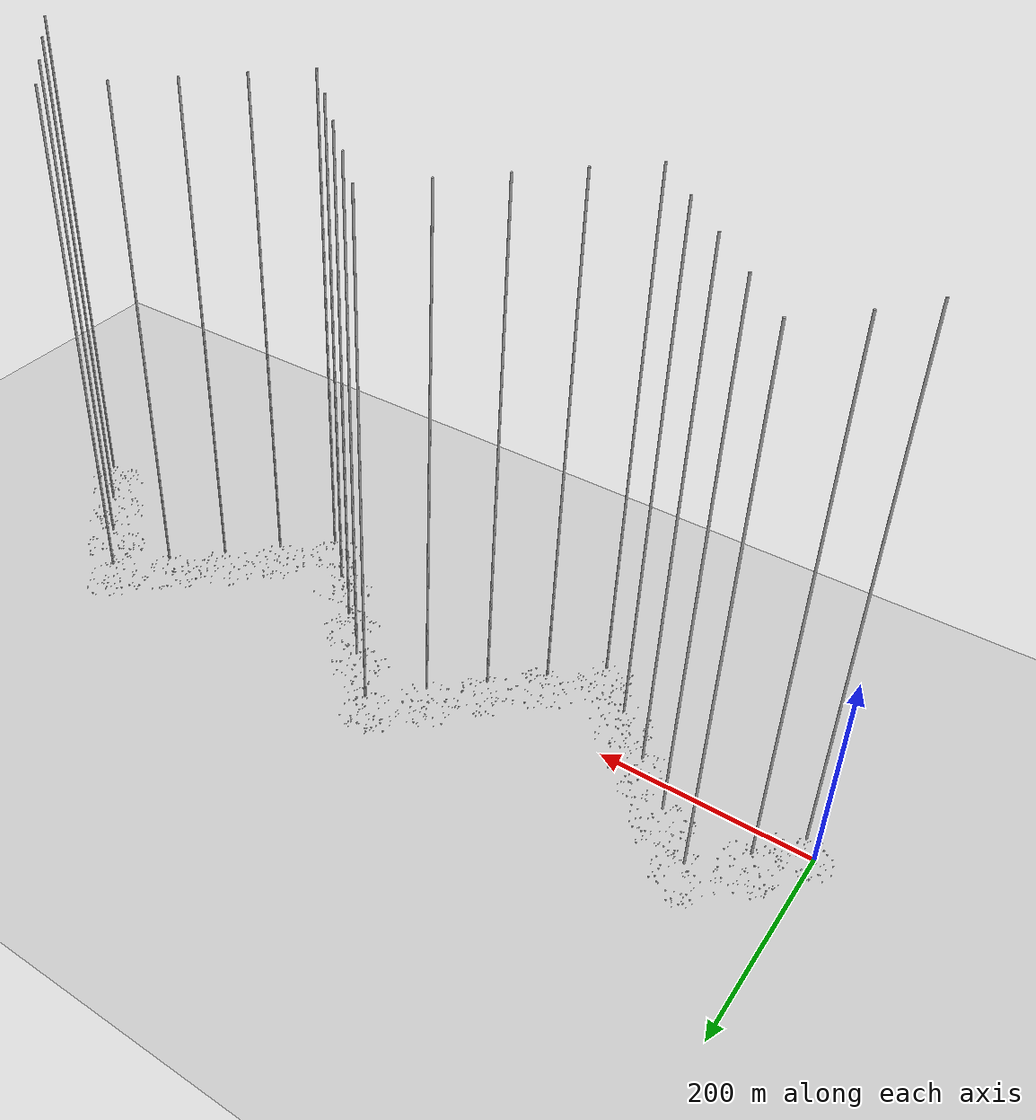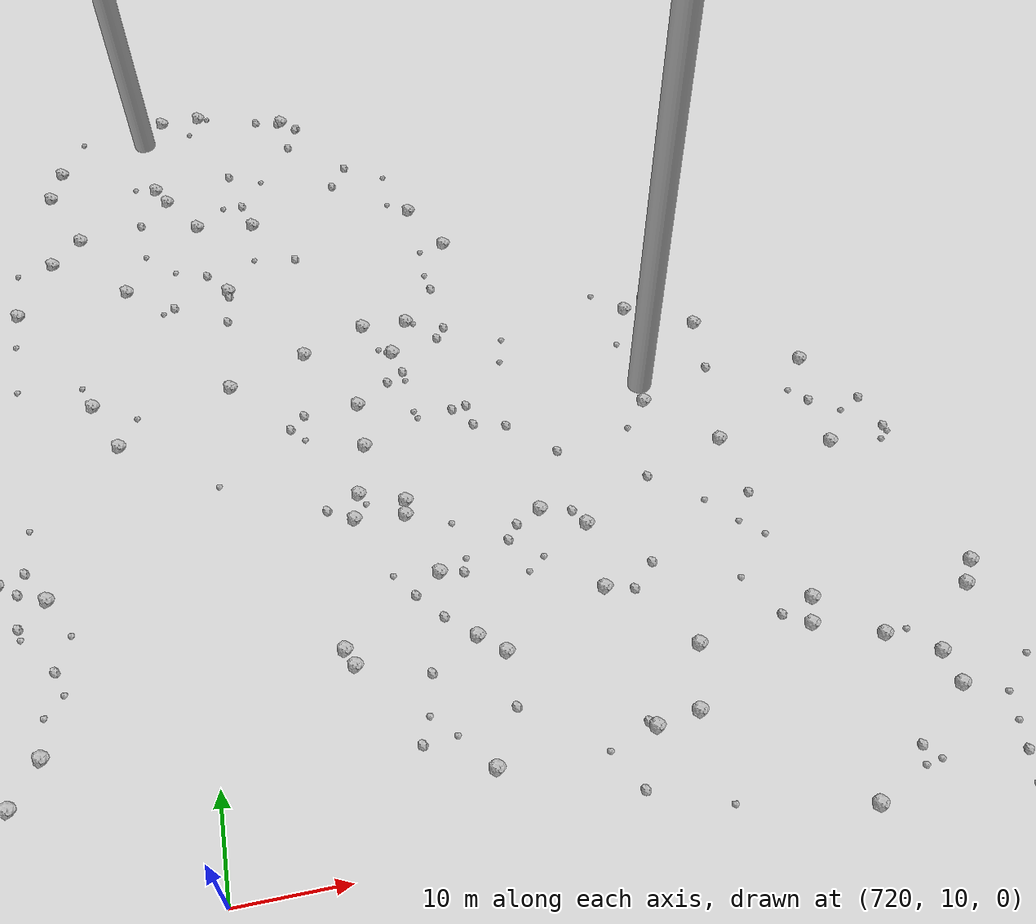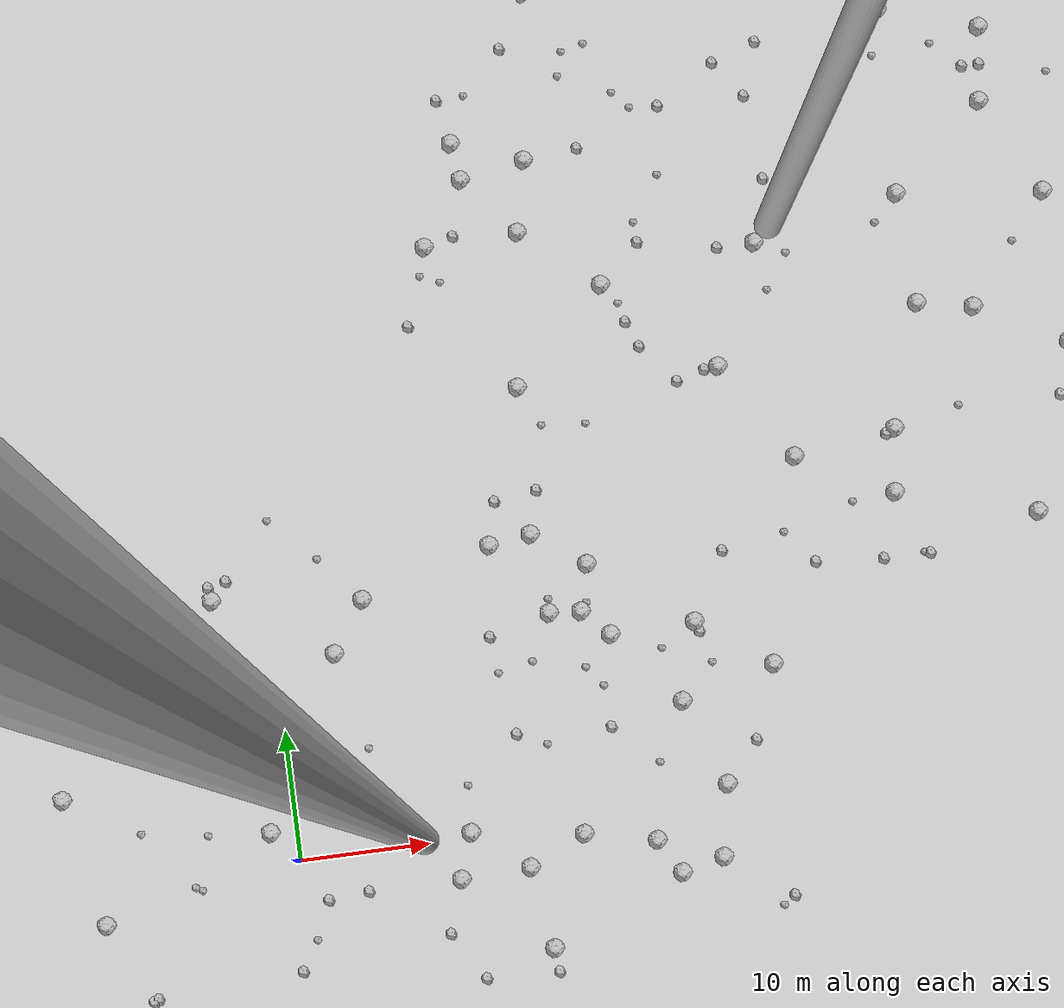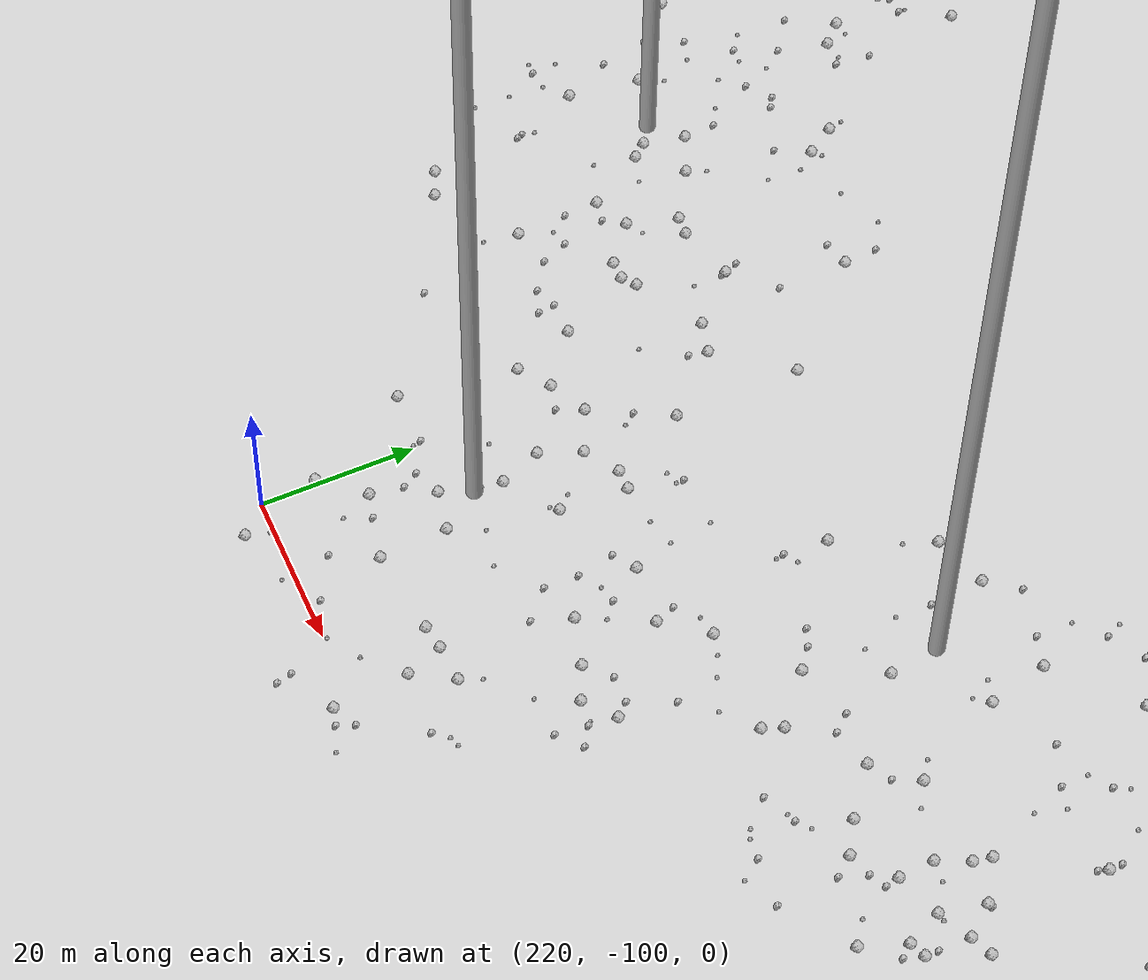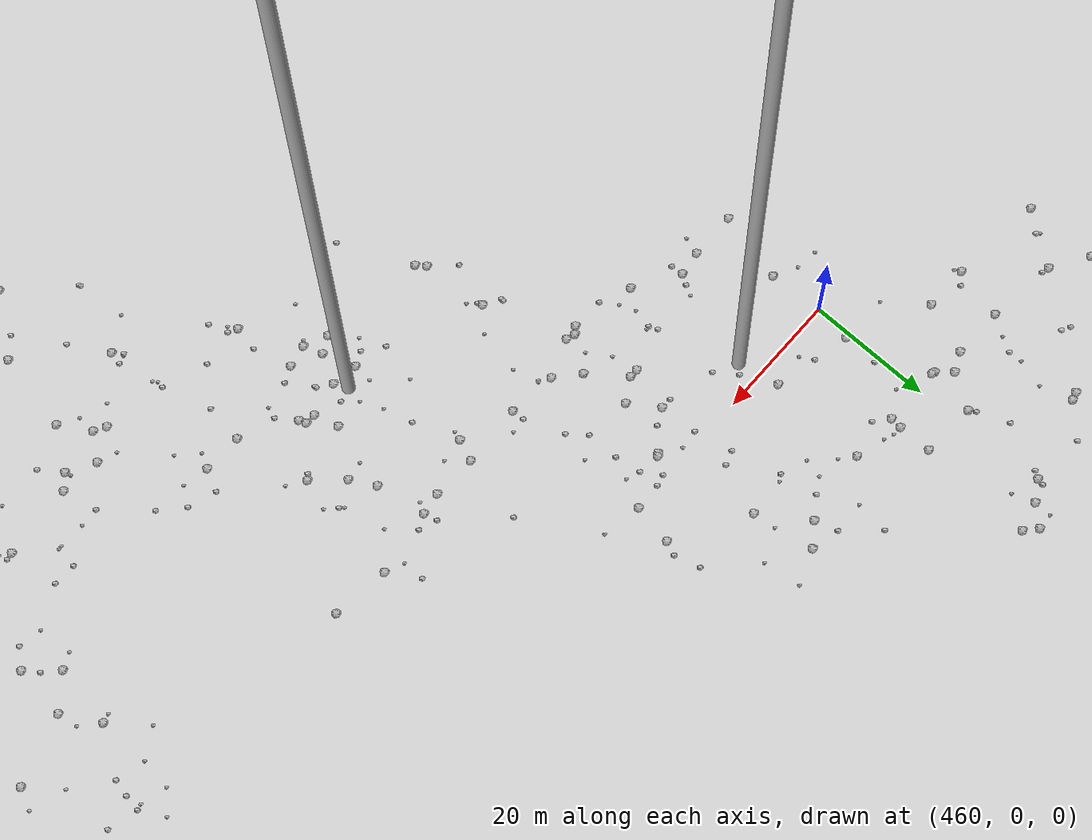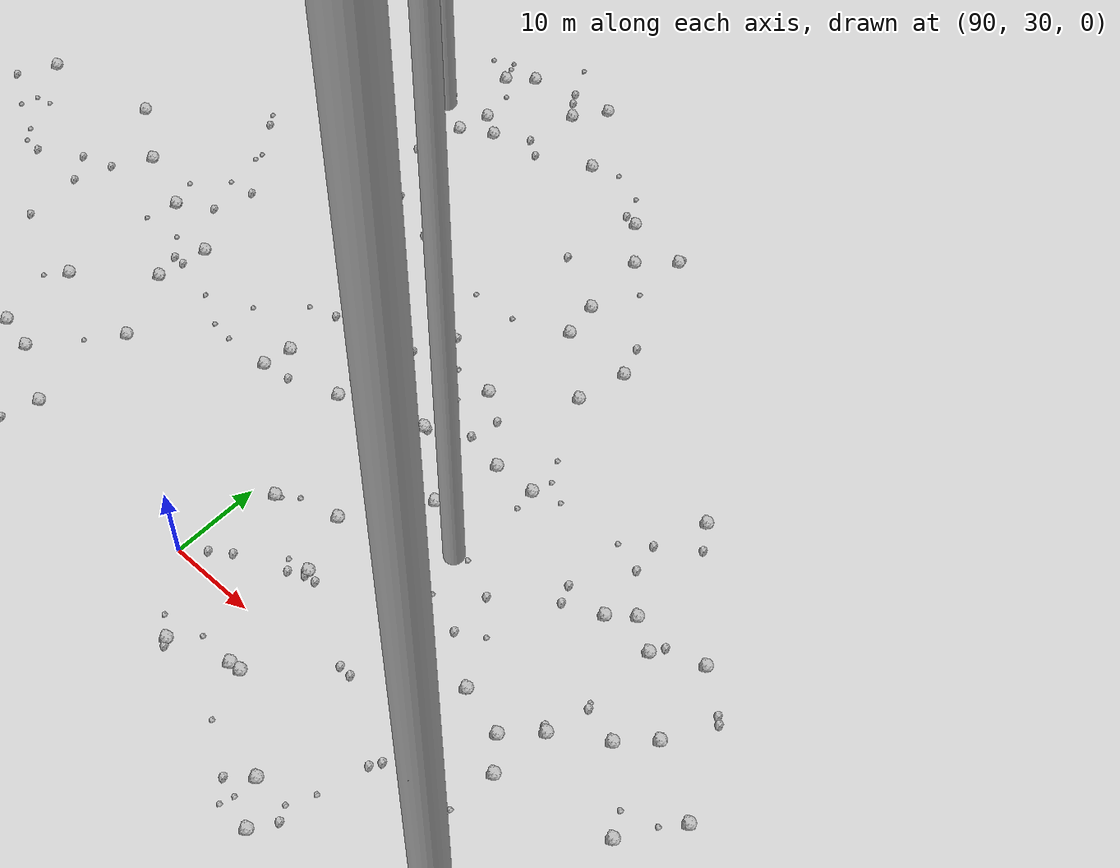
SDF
<sdf version="1.6">
 <world name="default">
  <include><uri>model://custom_ground</uri></include>
  <include><uri>model://sun</uri></include>
  <spherical_coordinates>
   <surface_model>EARTH_WGS84</surface_model>
   <latitude_deg>38.161479</latitude_deg>
   <longitude_deg>-122.454630</longitude_deg>
   <elevation>488.0</elevation>
   <heading_deg>90</heading_deg>
  </spherical_coordinates>
  <model name="rock1_0_0">
   <include><uri>model://rock1</uri><pose>-8.676936144939155 11.637561756383867 0.5 0 0 0</pose></include>
  </model>
  <model name="rock1_0_1">
   <include><uri>model://rock1</uri><pose>-15.28422738402249 -2.9046601681512065 0.5 0 0 0</pose></include>
  </model>
  <model name="rock1_0_2">
   <include><uri>model://rock1</uri><pose>27.322768168559385 -2.045357332474559 0.5 0 0 0</pose></include>
  </model>
  <model name="rock1_0_3">
   <include><uri>model://rock1</uri><pose>23.931106764600052 16.164782574607152 0.5 0 0 0</pose></include>
  </model>
  <model name="rock1_0_4">
   <include><uri>model://rock1</uri><pose>17.556154061956462 22.20786044129612 0.5 0 0 0</pose></include>
  </model>
  <model name="rock1_0_5">
   <include><uri>model://rock1</uri><pose>38.154287775445425 10.14473013201512 0.5 0 0 0</pose></include>
  </model>
  <model name="rock1_0_6">
   <include><uri>model://rock1</uri><pose>-2.013876946543057 2.41611257572292 0.5 0 0 0</pose></include>
  </model>
  <model name="rock1_0_7">
   <include><uri>model://rock1</uri><pose>24.890997009322405 19.78023522267126 0.5 0 0 0</pose></include>
  </model>
  <model name="rock1_0_8">
   <include><uri>model://rock1</uri><pose>15.689689300359866 -23.60257508790437 0.5 0 0 0</pose></include>
  </model>
  <model name="rock1_0_9">
   <include><uri>model://rock1</uri><pose>7.2300225445005 19.31966409042127 0.5 0 0 0</pose></include>
  </model>
  <model name="rock1_0_10">
   <include><uri>model://rock1</uri><pose>-17.574604127709545 6.980109151737516 0.5 0 0 0</pose></include>
  </model>
  <model name="rock1_0_11">
   <include><uri>model://rock1</uri><pose>-6.777212397260371 -11.486596440793715 0.5 0 0 0</pose></include>
  </model>
  <model name="rock1_0_12">
   <include><uri>model://rock1</uri><pose>18.397679699028146 -9.12080662400885 0.5 0 0 0</pose></include>
  </model>
  <model name="rock1_0_13">
   <include><uri>model://rock1</uri><pose>21.82787056441844 -0.8288929410029091 0.5 0 0 0</pose></include>
  </model>
  <model name="rock1_0_14">
   <include><uri>model://rock1</uri><pose>30.750438812479423 8.242658971590274 0.5 0 0 0</pose></include>
  </model>
  <model name="rock1_0_15">
   <include><uri>model://rock1</uri><pose>12.04944592820138 -3.0318350315081055 0.5 0 0 0</pose></include>
  </model>
  <model name="rock1_0_16">
   <include><uri>model://rock1</uri><pose>28.879891695396616 -4.7445199655218495 0.5 0 0 0</pose></include>
  </model>
  <model name="rock1_0_17">
   <include><uri>model://rock1</uri><pose>33.27140651732042 1.473240355407789 0.5 0 0 0</pose></include>
  </model>
  <model name="rock1_0_18">
   <include><uri>model://rock1</uri><pose>17.41441878687631 -2.828405211155683 0.5 0 0 0</pose></include>
  </model>
  <model name="rock1_0_19">
   <include><uri>model://rock1</uri><pose>13.22558033182095 0.39512265984664907 0.5 0 0 0</pose></include>
  </model>
  <model name="rock1_0_20">
   <include><uri>model://rock1</uri><pose>4.564959939175786 15.438372600612162 0.5 0 0 0</pose></include>
  </model>
  <model name="rock1_0_21">
   <include><uri>model://rock1</uri><pose>32.19879865189429 -3.988773469174994 0.5 0 0 0</pose></include>
  </model>
  <model name="rock1_0_22">
   <include><uri>model://rock1</uri><pose>-4.391060433548812 20.743504401378523 0.5 0 0 0</pose></include>
  </model>
  <model name="rock1_0_23">
   <include><uri>model://rock1</uri><pose>-1.751934844882669 8.738729242564737 0.5 0 0 0</pose></include>
  </model>
  <model name="rock1_0_24">
   <include><uri>model://rock1</uri><pose>21.462683595973168 16.359565467044078 0.5 0 0 0</pose></include>
  </model>
  <model name="rock1_0_25">
   <include><uri>model://rock1</uri><pose>1.3494657716392027 -20.290917669143766 0.5 0 0 0</pose></include>
  </model>
  <model name="rock1_0_26">
   <include><uri>model://rock1</uri><pose>-3.118646624675886 -13.705412968494915 0.5 0 0 0</pose></include>
  </model>
  <model name="rock2_0_0">
   <include><uri>model://rock2</uri><pose>10.423141822270974 -16.938080857139816 0.3 0 0 0</pose></include>
  </model>
  <model name="rock2_0_1">
   <include><uri>model://rock2</uri><pose>35.99941994874565 4.529702362339535 0.3 0 0 0</pose></include>
  </model>
  <model name="rock2_0_2">
   <include><uri>model://rock2</uri><pose>-6.6349914352770085 8.923670206987055 0.3 0 0 0</pose></include>
  </model>
  <model name="rock2_0_3">
   <include><uri>model://rock2</uri><pose>18.530670161620797 -10.942781103791795 0.3 0 0 0</pose></include>
  </model>
  <model name="rock2_0_4">
   <include><uri>model://rock2</uri><pose>-0.8427114689259767 -8.348731838644913 0.3 0 0 0</pose></include>
  </model>
  <model name="rock2_0_5">
   <include><uri>model://rock2</uri><pose>11.411596651563109 -14.473126079764514 0.3 0 0 0</pose></include>
  </model>
  <model name="rock2_0_6">
   <include><uri>model://rock2</uri><pose>25.04033625441081 6.989508967373297 0.3 0 0 0</pose></include>
  </model>
  <model name="rock2_0_7">
   <include><uri>model://rock2</uri><pose>7.031225363398011 2.335448277645213 0.3 0 0 0</pose></include>
  </model>
  <model name="rock2_0_8">
   <include><uri>model://rock2</uri><pose>-10.400087375142213 11.112840879860691 0.3 0 0 0</pose></include>
  </model>
  <model name="rock2_0_9">
   <include><uri>model://rock2</uri><pose>18.067934291943374 -14.486671957280095 0.3 0 0 0</pose></include>
  </model>
  <model name="rock2_0_10">
   <include><uri>model://rock2</uri><pose>-4.564079082418335 21.828062972949155 0.3 0 0 0</pose></include>
  </model>
  <model name="rock2_0_11">
   <include><uri>model://rock2</uri><pose>12.958598135572423 -10.710458238323586 0.3 0 0 0</pose></include>
  </model>
  <model name="rock2_0_12">
   <include><uri>model://rock2</uri><pose>-12.362390863451227 -9.098261460144037 0.3 0 0 0</pose></include>
  </model>
  <model name="rock2_0_13">
   <include><uri>model://rock2</uri><pose>18.412988835705825 25.58518909016854 0.3 0 0 0</pose></include>
  </model>
  <model name="rock2_0_14">
   <include><uri>model://rock2</uri><pose>32.83649345109225 13.431470555639955 0.3 0 0 0</pose></include>
  </model>
  <model name="rock2_0_15">
   <include><uri>model://rock2</uri><pose>10.697280596123711 -7.018561978166463 0.3 0 0 0</pose></include>
  </model>
  <model name="rock2_0_16">
   <include><uri>model://rock2</uri><pose>17.69873724604581 7.402560558983545 0.3 0 0 0</pose></include>
  </model>
  <model name="rock2_0_17">
   <include><uri>model://rock2</uri><pose>-2.5159684518128778 -12.837808494638448 0.3 0 0 0</pose></include>
  </model>
  <model name="rock2_0_18">
   <include><uri>model://rock2</uri><pose>16.6497151214815 15.123423311956508 0.3 0 0 0</pose></include>
  </model>
  <model name="rock2_0_19">
   <include><uri>model://rock2</uri><pose>-3.1477226121086197 22.143886544028533 0.3 0 0 0</pose></include>
  </model>
  <model name="rock2_0_20">
   <include><uri>model://rock2</uri><pose>4.897015148297545 -3.002868440069065 0.3 0 0 0</pose></include>
  </model>
  <model name="rock2_0_21">
   <include><uri>model://rock2</uri><pose>2.1355803400802778 -15.789792983999911 0.3 0 0 0</pose></include>
  </model>
  <model name="rock2_0_22">
   <include><uri>model://rock2</uri><pose>1.7614777025808657 -3.2526362225460552 0.3 0 0 0</pose></include>
  </model>
  <model name="rock2_0_23">
   <include><uri>model://rock2</uri><pose>4.349186066687839 -23.478645311927927 0.3 0 0 0</pose></include>
  </model>
  <model name="rock2_0_24">
   <include><uri>model://rock2</uri><pose>-14.125001963955267 16.840398677737646 0.3 0 0 0</pose></include>
  </model>
  <model name="rock2_0_25">
   <include><uri>model://rock2</uri><pose>-12.013142549351542 -8.93745001875616 0.3 0 0 0</pose></include>
  </model>
  <model name="rock2_0_26">
   <include><uri>model://rock2</uri><pose>37.17678232634551 -7.605349061841427 0.3 0 0 0</pose></include>
  </model>
  <model name="rock3_0_0">
   <include><uri>model://rock3</uri><pose>29.040536876213224 -4.630172739215549 0.2 0 0 0</pose></include>
  </model>
  <model name="rock3_0_1">
   <include><uri>model://rock3</uri><pose>4.084220183377589 22.935586230048536 0.2 0 0 0</pose></include>
  </model>
  <model name="rock3_0_2">
   <include><uri>model://rock3</uri><pose>-3.7563662352310665 7.835498335785218 0.2 0 0 0</pose></include>
  </model>
  <model name="rock3_0_3">
   <include><uri>model://rock3</uri><pose>36.23673913939634 -8.25524273346893 0.2 0 0 0</pose></include>
  </model>
  <model name="rock3_0_4">
   <include><uri>model://rock3</uri><pose>0.503205360008085 -6.141510886738722 0.2 0 0 0</pose></include>
  </model>
  <model name="rock3_0_5">
   <include><uri>model://rock3</uri><pose>13.435247055888517 4.001625383265768 0.2 0 0 0</pose></include>
  </model>
  <model name="rock3_0_6">
   <include><uri>model://rock3</uri><pose>13.423100961156642 -16.72005200234382 0.2 0 0 0</pose></include>
  </model>
  <model name="rock3_0_7">
   <include><uri>model://rock3</uri><pose>33.45653787010419 10.913048848773315 0.2 0 0 0</pose></include>
  </model>
  <model name="rock3_0_8">
   <include><uri>model://rock3</uri><pose>-5.22926319539919 17.2921543027201 0.2 0 0 0</pose></include>
  </model>
  <model name="rock3_0_9">
   <include><uri>model://rock3</uri><pose>-11.94759735362226 3.6062942815620858 0.2 0 0 0</pose></include>
  </model>
  <model name="rock3_0_10">
   <include><uri>model://rock3</uri><pose>23.896107817654055 -21.36803229947739 0.2 0 0 0</pose></include>
  </model>
  <model name="rock3_0_11">
   <include><uri>model://rock3</uri><pose>11.729811918002081 -14.347098180895665 0.2 0 0 0</pose></include>
  </model>
  <model name="rock3_0_12">
   <include><uri>model://rock3</uri><pose>-6.857424791504208 2.8172844902681007 0.2 0 0 0</pose></include>
  </model>
  <model name="rock3_0_13">
   <include><uri>model://rock3</uri><pose>28.35330533177975 3.8028079553472907 0.2 0 0 0</pose></include>
  </model>
  <model name="rock3_0_14">
   <include><uri>model://rock3</uri><pose>-8.264775906431712 -0.9700468233437682 0.2 0 0 0</pose></include>
  </model>
  <model name="rock3_0_15">
   <include><uri>model://rock3</uri><pose>19.933338872857377 6.318753360964536 0.2 0 0 0</pose></include>
  </model>
  <model name="rock3_0_16">
   <include><uri>model://rock3</uri><pose>-2.6441689461404962 -19.707962708714348 0.2 0 0 0</pose></include>
  </model>
  <model name="rock3_0_17">
   <include><uri>model://rock3</uri><pose>-7.767002105504439 -1.249276781511238 0.2 0 0 0</pose></include>
  </model>
  <model name="rock3_0_18">
   <include><uri>model://rock3</uri><pose>24.873955486947764 10.234678672178191 0.2 0 0 0</pose></include>
  </model>
  <model name="rock3_0_19">
   <include><uri>model://rock3</uri><pose>-11.734029231616312 -13.81274100172585 0.2 0 0 0</pose></include>
  </model>
  <model name="rock3_0_20">
   <include><uri>model://rock3</uri><pose>6.229095914364301 7.833088797303418 0.2 0 0 0</pose></include>
  </model>
  <model name="rock3_0_21">
   <include><uri>model://rock3</uri><pose>0.584480702888726 26.45281746527946 0.2 0 0 0</pose></include>
  </model>
  <model name="rock3_0_22">
   <include><uri>model://rock3</uri><pose>26.25643187490983 -18.39348275319608 0.2 0 0 0</pose></include>
  </model>
  <model name="rock3_0_23">
   <include><uri>model://rock3</uri><pose>16.933494363239788 12.245957892805912 0.2 0 0 0</pose></include>
  </model>
  <model name="rock3_0_24">
   <include><uri>model://rock3</uri><pose>6.782160169227364 -21.188085796766536 0.2 0 0 0</pose></include>
  </model>
  <model name="rock3_0_25">
   <include><uri>model://rock3</uri><pose>23.687901636526867 11.82647887391088 0.2 0 0 0</pose></include>
  </model>
  <model name="rock3_0_26">
   <include><uri>model://rock3</uri><pose>19.664039155197933 12.796799706828722 0.2 0 0 0</pose></include>
  </model>
  <model name="rock1_1_0">
   <include><uri>model://rock1</uri><pose>53.53997761118629 36.806700894119146 0.5 0 0 0</pose></include>
  </model>
  <model name="rock1_1_1">
   <include><uri>model://rock1</uri><pose>42.16760498237005 25.98618886722934 0.5 0 0 0</pose></include>
  </model>
  <model name="rock1_1_2">
   <include><uri>model://rock1</uri><pose>41.52916911346689 43.32720700308006 0.5 0 0 0</pose></include>
  </model>
  <model name="rock1_1_3">
   <include><uri>model://rock1</uri><pose>49.527262128062674 22.160459495830086 0.5 0 0 0</pose></include>
  </model>
  <model name="rock1_1_4">
   <include><uri>model://rock1</uri><pose>26.109309129430287 65.98450306892971 0.5 0 0 0</pose></include>
  </model>
  <model name="rock1_1_5">
   <include><uri>model://rock1</uri><pose>57.903897570425336 35.923457348390386 0.5 0 0 0</pose></include>
  </model>
  <model name="rock1_1_6">
   <include><uri>model://rock1</uri><pose>37.27188168665472 33.875687654681784 0.5 0 0 0</pose></include>
  </model>
  <model name="rock1_1_7">
   <include><uri>model://rock1</uri><pose>64.92694740047777 32.20483158697894 0.5 0 0 0</pose></include>
  </model>
  <model name="rock1_1_8">
   <include><uri>model://rock1</uri><pose>60.369367252977476 19.172538525626756 0.5 0 0 0</pose></include>
  </model>
  <model name="rock1_1_9">
   <include><uri>model://rock1</uri><pose>15.656736028482705 46.40260600522882 0.5 0 0 0</pose></include>
  </model>
  <model name="rock1_1_10">
   <include><uri>model://rock1</uri><pose>54.113931753109014 60.849989164268734 0.5 0 0 0</pose></include>
  </model>
  <model name="rock1_1_11">
   <include><uri>model://rock1</uri><pose>46.62316693524619 63.741473603345966 0.5 0 0 0</pose></include>
  </model>
  <model name="rock1_1_12">
   <include><uri>model://rock1</uri><pose>24.38913063378621 52.38391834537174 0.5 0 0 0</pose></include>
  </model>
  <model name="rock1_1_13">
   <include><uri>model://rock1</uri><pose>21.429049450787478 34.2983366903144 0.5 0 0 0</pose></include>
  </model>
  <model name="rock1_1_14">
   <include><uri>model://rock1</uri><pose>29.045818169014485 41.57956276343667 0.5 0 0 0</pose></include>
  </model>
  <model name="rock1_1_15">
   <include><uri>model://rock1</uri><pose>50.25897171016085 27.15413114037133 0.5 0 0 0</pose></include>
  </model>
  <model name="rock1_1_16">
   <include><uri>model://rock1</uri><pose>19.215228083241858 51.44958580734001 0.5 0 0 0</pose></include>
  </model>
  <model name="rock1_1_17">
   <include><uri>model://rock1</uri><pose>18.828393047581834 54.495730135621216 0.5 0 0 0</pose></include>
  </model>
  <model name="rock1_1_18">
   <include><uri>model://rock1</uri><pose>32.557311906434364 14.214723043440623 0.5 0 0 0</pose></include>
  </model>
  <model name="rock1_1_19">
   <include><uri>model://rock1</uri><pose>64.83327999008526 44.44086342315997 0.5 0 0 0</pose></include>
  </model>
  <model name="rock1_1_20">
   <include><uri>model://rock1</uri><pose>20.85227294169099 22.65169417493021 0.5 0 0 0</pose></include>
  </model>
  <model name="rock1_1_21">
   <include><uri>model://rock1</uri><pose>53.28886590781207 45.77534853585879 0.5 0 0 0</pose></include>
  </model>
  <model name="rock1_1_22">
   <include><uri>model://rock1</uri><pose>39.925190923442464 68.34832605956174 0.5 0 0 0</pose></include>
  </model>
  <model name="rock1_1_23">
   <include><uri>model://rock1</uri><pose>60.97350506022579 52.3716117717611 0.5 0 0 0</pose></include>
  </model>
  <model name="rock1_1_24">
   <include><uri>model://rock1</uri><pose>61.90996346958726 58.39236511121283 0.5 0 0 0</pose></include>
  </model>
  <model name="rock1_1_25">
   <include><uri>model://rock1</uri><pose>23.0985989525828 46.635713789712106 0.5 0 0 0</pose></include>
  </model>
  <model name="rock1_1_26">
   <include><uri>model://rock1</uri><pose>25.964825283797353 14.092760658143895 0.5 0 0 0</pose></include>
  </model>
  <model name="rock2_1_0">
   <include><uri>model://rock2</uri><pose>38.56757389539811 43.35855995935486 0.3 0 0 0</pose></include>
  </model>
  <model name="rock2_1_1">
   <include><uri>model://rock2</uri><pose>42.4758715818262 55.30943350906314 0.3 0 0 0</pose></include>
  </model>
  <model name="rock2_1_2">
   <include><uri>model://rock2</uri><pose>30.53809985882902 38.39555554577457 0.3 0 0 0</pose></include>
  </model>
  <model name="rock2_1_3">
   <include><uri>model://rock2</uri><pose>23.696431627457166 61.71039593168154 0.3 0 0 0</pose></include>
  </model>
  <model name="rock2_1_4">
   <include><uri>model://rock2</uri><pose>42.590120325875525 17.575913367629354 0.3 0 0 0</pose></include>
  </model>
  <model name="rock2_1_5">
   <include><uri>model://rock2</uri><pose>35.54530813547342 55.412457560513396 0.3 0 0 0</pose></include>
  </model>
  <model name="rock2_1_6">
   <include><uri>model://rock2</uri><pose>40.35862535748116 58.34857060512005 0.3 0 0 0</pose></include>
  </model>
  <model name="rock2_1_7">
   <include><uri>model://rock2</uri><pose>13.533639032070736 40.26117103154341 0.3 0 0 0</pose></include>
  </model>
  <model name="rock2_1_8">
   <include><uri>model://rock2</uri><pose>31.357398443748462 36.30119478306116 0.3 0 0 0</pose></include>
  </model>
  <model name="rock2_1_9">
   <include><uri>model://rock2</uri><pose>57.85673393151813 63.33444473040952 0.3 0 0 0</pose></include>
  </model>
  <model name="rock2_1_10">
   <include><uri>model://rock2</uri><pose>44.00010389178701 59.59978197614822 0.3 0 0 0</pose></include>
  </model>
  <model name="rock2_1_11">
   <include><uri>model://rock2</uri><pose>18.129609024723003 58.16289711936156 0.3 0 0 0</pose></include>
  </model>
  <model name="rock2_1_12">
   <include><uri>model://rock2</uri><pose>47.89027224851609 17.132966215699376 0.3 0 0 0</pose></include>
  </model>
  <model name="rock2_1_13">
   <include><uri>model://rock2</uri><pose>61.479234000929566 55.41280697981353 0.3 0 0 0</pose></include>
  </model>
  <model name="rock2_1_14">
   <include><uri>model://rock2</uri><pose>33.899947956597416 33.146715349969185 0.3 0 0 0</pose></include>
  </model>
  <model name="rock2_1_15">
   <include><uri>model://rock2</uri><pose>51.559879954844284 17.078848928851023 0.3 0 0 0</pose></include>
  </model>
  <model name="rock2_1_16">
   <include><uri>model://rock2</uri><pose>17.991991975153823 47.029992370516936 0.3 0 0 0</pose></include>
  </model>
  <model name="rock2_1_17">
   <include><uri>model://rock2</uri><pose>43.005054616053236 48.41584798915568 0.3 0 0 0</pose></include>
  </model>
  <model name="rock2_1_18">
   <include><uri>model://rock2</uri><pose>49.55847035443158 26.8278775674518 0.3 0 0 0</pose></include>
  </model>
  <model name="rock2_1_19">
   <include><uri>model://rock2</uri><pose>64.0463299260347 23.02171999827114 0.3 0 0 0</pose></include>
  </model>
  <model name="rock2_1_20">
   <include><uri>model://rock2</uri><pose>60.10375440832888 55.430639212434244 0.3 0 0 0</pose></include>
  </model>
  <model name="rock2_1_21">
   <include><uri>model://rock2</uri><pose>63.6038070597077 28.11393286031348 0.3 0 0 0</pose></include>
  </model>
  <model name="rock2_1_22">
   <include><uri>model://rock2</uri><pose>35.48217656446588 19.40492339423934 0.3 0 0 0</pose></include>
  </model>
  <model name="rock2_1_23">
   <include><uri>model://rock2</uri><pose>32.367404113471814 44.619551476824114 0.3 0 0 0</pose></include>
  </model>
  <model name="rock2_1_24">
   <include><uri>model://rock2</uri><pose>21.767092188696907 26.049287312224877 0.3 0 0 0</pose></include>
  </model>
  <model name="rock2_1_25">
   <include><uri>model://rock2</uri><pose>36.15669963628417 33.7801333790104 0.3 0 0 0</pose></include>
  </model>
  <model name="rock2_1_26">
   <include><uri>model://rock2</uri><pose>28.689298698746562 52.84051894221641 0.3 0 0 0</pose></include>
  </model>
  <model name="rock3_1_0">
   <include><uri>model://rock3</uri><pose>52.68749754063685 64.11182160813931 0.2 0 0 0</pose></include>
  </model>
  <model name="rock3_1_1">
   <include><uri>model://rock3</uri><pose>40.46141452701339 20.210180755667054 0.2 0 0 0</pose></include>
  </model>
  <model name="rock3_1_2">
   <include><uri>model://rock3</uri><pose>53.11777484574134 57.23355861333548 0.2 0 0 0</pose></include>
  </model>
  <model name="rock3_1_3">
   <include><uri>model://rock3</uri><pose>22.8680888705034 31.102869277954937 0.2 0 0 0</pose></include>
  </model>
  <model name="rock3_1_4">
   <include><uri>model://rock3</uri><pose>51.26431856499818 43.686948775310434 0.2 0 0 0</pose></include>
  </model>
  <model name="rock3_1_5">
   <include><uri>model://rock3</uri><pose>21.520502197536878 17.45325757561832 0.2 0 0 0</pose></include>
  </model>
  <model name="rock3_1_6">
   <include><uri>model://rock3</uri><pose>30.37952770278723 61.3000349427227 0.2 0 0 0</pose></include>
  </model>
  <model name="rock3_1_7">
   <include><uri>model://rock3</uri><pose>61.816389412156575 40.806770369560525 0.2 0 0 0</pose></include>
  </model>
  <model name="rock3_1_8">
   <include><uri>model://rock3</uri><pose>14.962894737345241 44.16251017403361 0.2 0 0 0</pose></include>
  </model>
  <model name="rock3_1_9">
   <include><uri>model://rock3</uri><pose>34.71352827741758 49.85161013188836 0.2 0 0 0</pose></include>
  </model>
  <model name="rock3_1_10">
   <include><uri>model://rock3</uri><pose>32.30055880659755 46.269682711861876 0.2 0 0 0</pose></include>
  </model>
  <model name="rock3_1_11">
   <include><uri>model://rock3</uri><pose>43.89830369813732 42.237347720787234 0.2 0 0 0</pose></include>
  </model>
  <model name="rock3_1_12">
   <include><uri>model://rock3</uri><pose>46.14321673330269 21.85676796365832 0.2 0 0 0</pose></include>
  </model>
  <model name="rock3_1_13">
   <include><uri>model://rock3</uri><pose>33.28667791843023 55.58973609849485 0.2 0 0 0</pose></include>
  </model>
  <model name="rock3_1_14">
   <include><uri>model://rock3</uri><pose>24.43133704566768 16.810286710940638 0.2 0 0 0</pose></include>
  </model>
  <model name="rock3_1_15">
   <include><uri>model://rock3</uri><pose>55.53687938591336 28.323744447109558 0.2 0 0 0</pose></include>
  </model>
  <model name="rock3_1_16">
   <include><uri>model://rock3</uri><pose>16.484412030618284 43.49671326000137 0.2 0 0 0</pose></include>
  </model>
  <model name="rock3_1_17">
   <include><uri>model://rock3</uri><pose>26.321876940051236 30.779335689151853 0.2 0 0 0</pose></include>
  </model>
  <model name="rock3_1_18">
   <include><uri>model://rock3</uri><pose>41.99223279636577 39.45501302503274 0.2 0 0 0</pose></include>
  </model>
  <model name="rock3_1_19">
   <include><uri>model://rock3</uri><pose>32.062137070615364 57.010633849517994 0.2 0 0 0</pose></include>
  </model>
  <model name="rock3_1_20">
   <include><uri>model://rock3</uri><pose>51.118226142539086 17.19702677422034 0.2 0 0 0</pose></include>
  </model>
  <model name="rock3_1_21">
   <include><uri>model://rock3</uri><pose>30.17823108391366 39.96156977576871 0.2 0 0 0</pose></include>
  </model>
  <model name="rock3_1_22">
   <include><uri>model://rock3</uri><pose>57.84372162828063 57.62630653684252 0.2 0 0 0</pose></include>
  </model>
  <model name="rock3_1_23">
   <include><uri>model://rock3</uri><pose>27.98139293921553 58.90616190307167 0.2 0 0 0</pose></include>
  </model>
  <model name="rock3_1_24">
   <include><uri>model://rock3</uri><pose>29.730360049556914 12.506849944357652 0.2 0 0 0</pose></include>
  </model>
  <model name="rock3_1_25">
   <include><uri>model://rock3</uri><pose>28.54889981267627 60.87826092378879 0.2 0 0 0</pose></include>
  </model>
  <model name="rock3_1_26">
   <include><uri>model://rock3</uri><pose>20.315665346531325 58.29530182195249 0.2 0 0 0</pose></include>
  </model>
  <model name="rock1_2_0">
   <include><uri>model://rock1</uri><pose>102.31343207075653 93.54950340070278 0.5 0 0 0</pose></include>
  </model>
  <model name="rock1_2_1">
   <include><uri>model://rock1</uri><pose>67.85846870056287 101.71803539853501 0.5 0 0 0</pose></include>
  </model>
  <model name="rock1_2_2">
   <include><uri>model://rock1</uri><pose>87.7836014988915 54.486031444057474 0.5 0 0 0</pose></include>
  </model>
  <model name="rock1_2_3">
   <include><uri>model://rock1</uri><pose>106.943690470273 71.69603467750582 0.5 0 0 0</pose></include>
  </model>
  <model name="rock1_2_4">
   <include><uri>model://rock1</uri><pose>70.626501440711 95.5517736169447 0.5 0 0 0</pose></include>
  </model>
  <model name="rock1_2_5">
   <include><uri>model://rock1</uri><pose>97.43265789404492 57.745010105324944 0.5 0 0 0</pose></include>
  </model>
  <model name="rock1_2_6">
   <include><uri>model://rock1</uri><pose>100.15879098573706 77.70601583187988 0.5 0 0 0</pose></include>
  </model>
  <model name="rock1_2_7">
   <include><uri>model://rock1</uri><pose>94.97142130567408 94.54253542929587 0.5 0 0 0</pose></include>
  </model>
  <model name="rock1_2_8">
   <include><uri>model://rock1</uri><pose>96.58753457848346 61.17943514243153 0.5 0 0 0</pose></include>
  </model>
  <model name="rock1_2_9">
   <include><uri>model://rock1</uri><pose>78.87944603262497 51.91968857348084 0.5 0 0 0</pose></include>
  </model>
  <model name="rock1_2_10">
   <include><uri>model://rock1</uri><pose>94.6210023744446 63.43113999852221 0.5 0 0 0</pose></include>
  </model>
  <model name="rock1_2_11">
   <include><uri>model://rock1</uri><pose>79.45727370788306 55.201253710948784 0.5 0 0 0</pose></include>
  </model>
  <model name="rock1_2_12">
   <include><uri>model://rock1</uri><pose>80.66086228667348 105.97090096462898 0.5 0 0 0</pose></include>
  </model>
  <model name="rock1_2_13">
   <include><uri>model://rock1</uri><pose>73.18377988241556 93.94012861535555 0.5 0 0 0</pose></include>
  </model>
  <model name="rock1_2_14">
   <include><uri>model://rock1</uri><pose>72.67545490297843 71.18895793000645 0.5 0 0 0</pose></include>
  </model>
  <model name="rock1_2_15">
   <include><uri>model://rock1</uri><pose>95.1533627443996 56.34830121171458 0.5 0 0 0</pose></include>
  </model>
  <model name="rock1_2_16">
   <include><uri>model://rock1</uri><pose>98.7251443643587 90.13648925355359 0.5 0 0 0</pose></include>
  </model>
  <model name="rock1_2_17">
   <include><uri>model://rock1</uri><pose>70.57131038289478 104.06280141377604 0.5 0 0 0</pose></include>
  </model>
  <model name="rock1_2_18">
   <include><uri>model://rock1</uri><pose>78.91347576842728 70.42551017848214 0.5 0 0 0</pose></include>
  </model>
  <model name="rock1_2_19">
   <include><uri>model://rock1</uri><pose>108.30460484755844 77.44344625280684 0.5 0 0 0</pose></include>
  </model>
  <model name="rock1_2_20">
   <include><uri>model://rock1</uri><pose>99.4608578352962 82.00825488827938 0.5 0 0 0</pose></include>
  </model>
  <model name="rock1_2_21">
   <include><uri>model://rock1</uri><pose>85.2881880383811 97.93013341836067 0.5 0 0 0</pose></include>
  </model>
  <model name="rock1_2_22">
   <include><uri>model://rock1</uri><pose>69.6408442049931 91.80153192677795 0.5 0 0 0</pose></include>
  </model>
  <model name="rock1_2_23">
   <include><uri>model://rock1</uri><pose>65.05441826393246 95.07924074393557 0.5 0 0 0</pose></include>
  </model>
  <model name="rock1_2_24">
   <include><uri>model://rock1</uri><pose>79.76114425652001 71.66644895211547 0.5 0 0 0</pose></include>
  </model>
  <model name="rock1_2_25">
   <include><uri>model://rock1</uri><pose>78.073967301742 102.44585936647869 0.5 0 0 0</pose></include>
  </model>
  <model name="rock1_2_26">
   <include><uri>model://rock1</uri><pose>99.26029031454951 65.78486522174772 0.5 0 0 0</pose></include>
  </model>
  <model name="rock2_2_0">
   <include><uri>model://rock2</uri><pose>52.60083161278577 76.89515381385502 0.3 0 0 0</pose></include>
  </model>
  <model name="rock2_2_1">
   <include><uri>model://rock2</uri><pose>61.88237583438038 97.46023041510772 0.3 0 0 0</pose></include>
  </model>
  <model name="rock2_2_2">
   <include><uri>model://rock2</uri><pose>78.37749327530545 76.9612942766776 0.3 0 0 0</pose></include>
  </model>
  <model name="rock2_2_3">
   <include><uri>model://rock2</uri><pose>92.55005058327463 85.73646016732964 0.3 0 0 0</pose></include>
  </model>
  <model name="rock2_2_4">
   <include><uri>model://rock2</uri><pose>76.62140493687147 104.20514498485196 0.3 0 0 0</pose></include>
  </model>
  <model name="rock2_2_5">
   <include><uri>model://rock2</uri><pose>102.60010214139412 63.591091858103695 0.3 0 0 0</pose></include>
  </model>
  <model name="rock2_2_6">
   <include><uri>model://rock2</uri><pose>75.78882987694868 105.52162051063449 0.3 0 0 0</pose></include>
  </model>
  <model name="rock2_2_7">
   <include><uri>model://rock2</uri><pose>89.36852731744838 64.20692180907378 0.3 0 0 0</pose></include>
  </model>
  <model name="rock2_2_8">
   <include><uri>model://rock2</uri><pose>87.4607832441935 57.10758431970841 0.3 0 0 0</pose></include>
  </model>
  <model name="rock2_2_9">
   <include><uri>model://rock2</uri><pose>70.69813229645128 75.36778432003301 0.3 0 0 0</pose></include>
  </model>
  <model name="rock2_2_10">
   <include><uri>model://rock2</uri><pose>88.44209074346631 63.227216351936065 0.3 0 0 0</pose></include>
  </model>
  <model name="rock2_2_11">
   <include><uri>model://rock2</uri><pose>91.59554901171188 68.85510375473083 0.3 0 0 0</pose></include>
  </model>
  <model name="rock2_2_12">
   <include><uri>model://rock2</uri><pose>106.95350248531916 81.08347297005113 0.3 0 0 0</pose></include>
  </model>
  <model name="rock2_2_13">
   <include><uri>model://rock2</uri><pose>59.20285117737311 67.95337117744259 0.3 0 0 0</pose></include>
  </model>
  <model name="rock2_2_14">
   <include><uri>model://rock2</uri><pose>58.7778390547911 86.04144030016246 0.3 0 0 0</pose></include>
  </model>
  <model name="rock2_2_15">
   <include><uri>model://rock2</uri><pose>97.96751502099735 57.83275661516343 0.3 0 0 0</pose></include>
  </model>
  <model name="rock2_2_16">
   <include><uri>model://rock2</uri><pose>79.65499152334081 61.89912946878212 0.3 0 0 0</pose></include>
  </model>
  <model name="rock2_2_17">
   <include><uri>model://rock2</uri><pose>77.03826226241254 96.22227392830393 0.3 0 0 0</pose></include>
  </model>
  <model name="rock2_2_18">
   <include><uri>model://rock2</uri><pose>66.07440392051822 74.27528979953502 0.3 0 0 0</pose></include>
  </model>
  <model name="rock2_2_19">
   <include><uri>model://rock2</uri><pose>102.42583775587185 94.14139232301628 0.3 0 0 0</pose></include>
  </model>
  <model name="rock2_2_20">
   <include><uri>model://rock2</uri><pose>82.12939909577386 52.40702040262257 0.3 0 0 0</pose></include>
  </model>
  <model name="rock2_2_21">
   <include><uri>model://rock2</uri><pose>68.21554338740597 86.11126230391912 0.3 0 0 0</pose></include>
  </model>
  <model name="rock2_2_22">
   <include><uri>model://rock2</uri><pose>72.12635302376577 79.44765393367042 0.3 0 0 0</pose></include>
  </model>
  <model name="rock2_2_23">
   <include><uri>model://rock2</uri><pose>79.12394873366088 94.80124681315559 0.3 0 0 0</pose></include>
  </model>
  <model name="rock2_2_24">
   <include><uri>model://rock2</uri><pose>76.45439512382148 73.92742045565466 0.3 0 0 0</pose></include>
  </model>
  <model name="rock2_2_25">
   <include><uri>model://rock2</uri><pose>93.3244772962621 94.93338405603 0.3 0 0 0</pose></include>
  </model>
  <model name="rock2_2_26">
   <include><uri>model://rock2</uri><pose>81.97250423079765 74.59554374723535 0.3 0 0 0</pose></include>
  </model>
  <model name="rock3_2_0">
   <include><uri>model://rock3</uri><pose>102.08855898929363 60.421298838704644 0.2 0 0 0</pose></include>
  </model>
  <model name="rock3_2_1">
   <include><uri>model://rock3</uri><pose>94.02935288582523 74.988373266472 0.2 0 0 0</pose></include>
  </model>
  <model name="rock3_2_2">
   <include><uri>model://rock3</uri><pose>97.38509906964379 62.81595578311531 0.2 0 0 0</pose></include>
  </model>
  <model name="rock3_2_3">
   <include><uri>model://rock3</uri><pose>64.38733416379377 103.1922622990966 0.2 0 0 0</pose></include>
  </model>
  <model name="rock3_2_4">
   <include><uri>model://rock3</uri><pose>92.32120751104262 97.6708229666137 0.2 0 0 0</pose></include>
  </model>
  <model name="rock3_2_5">
   <include><uri>model://rock3</uri><pose>66.64626685433349 104.3590585231643 0.2 0 0 0</pose></include>
  </model>
  <model name="rock3_2_6">
   <include><uri>model://rock3</uri><pose>55.17446560857229 82.66567070138429 0.2 0 0 0</pose></include>
  </model>
  <model name="rock3_2_7">
   <include><uri>model://rock3</uri><pose>81.97155849464117 70.05605153762511 0.2 0 0 0</pose></include>
  </model>
  <model name="rock3_2_8">
   <include><uri>model://rock3</uri><pose>56.041696634958015 67.55953480233441 0.2 0 0 0</pose></include>
  </model>
  <model name="rock3_2_9">
   <include><uri>model://rock3</uri><pose>67.86003552817411 82.20956174838248 0.2 0 0 0</pose></include>
  </model>
  <model name="rock3_2_10">
   <include><uri>model://rock3</uri><pose>71.96306949878498 56.4988029306513 0.2 0 0 0</pose></include>
  </model>
  <model name="rock3_2_11">
   <include><uri>model://rock3</uri><pose>56.86055768083655 98.61894920297813 0.2 0 0 0</pose></include>
  </model>
  <model name="rock3_2_12">
   <include><uri>model://rock3</uri><pose>51.52013638627137 78.25239483784873 0.2 0 0 0</pose></include>
  </model>
  <model name="rock3_2_13">
   <include><uri>model://rock3</uri><pose>66.70854481340395 54.12187369824692 0.2 0 0 0</pose></include>
  </model>
  <model name="rock3_2_14">
   <include><uri>model://rock3</uri><pose>76.44539023954465 60.90089947609994 0.2 0 0 0</pose></include>
  </model>
  <model name="rock3_2_15">
   <include><uri>model://rock3</uri><pose>55.39789191240268 72.99168781732479 0.2 0 0 0</pose></include>
  </model>
  <model name="rock3_2_16">
   <include><uri>model://rock3</uri><pose>73.25013137195278 51.77127025117624 0.2 0 0 0</pose></include>
  </model>
  <model name="rock3_2_17">
   <include><uri>model://rock3</uri><pose>67.03608083664976 103.43784482725015 0.2 0 0 0</pose></include>
  </model>
  <model name="rock3_2_18">
   <include><uri>model://rock3</uri><pose>79.75436748293782 76.80603856088737 0.2 0 0 0</pose></include>
  </model>
  <model name="rock3_2_19">
   <include><uri>model://rock3</uri><pose>69.88500895278847 99.58825199318598 0.2 0 0 0</pose></include>
  </model>
  <model name="rock3_2_20">
   <include><uri>model://rock3</uri><pose>55.37338355889824 71.96934406717081 0.2 0 0 0</pose></include>
  </model>
  <model name="rock3_2_21">
   <include><uri>model://rock3</uri><pose>88.4267825102367 99.07011696535847 0.2 0 0 0</pose></include>
  </model>
  <model name="rock3_2_22">
   <include><uri>model://rock3</uri><pose>94.64209099487285 65.81131929203387 0.2 0 0 0</pose></include>
  </model>
  <model name="rock3_2_23">
   <include><uri>model://rock3</uri><pose>102.07517364557593 87.12363229443716 0.2 0 0 0</pose></include>
  </model>
  <model name="rock3_2_24">
   <include><uri>model://rock3</uri><pose>73.76576823465184 109.27898751001848 0.2 0 0 0</pose></include>
  </model>
  <model name="rock3_2_25">
   <include><uri>model://rock3</uri><pose>88.69262467748638 74.7591819002343 0.2 0 0 0</pose></include>
  </model>
  <model name="rock3_2_26">
   <include><uri>model://rock3</uri><pose>70.58649429945392 52.10624457028849 0.2 0 0 0</pose></include>
  </model>
  <model name="rock1_3_0">
   <include><uri>model://rock1</uri><pose>132.6441271402039 53.44072159473489 0.5 0 0 0</pose></include>
  </model>
  <model name="rock1_3_1">
   <include><uri>model://rock1</uri><pose>101.5438021784039 37.16697055616817 0.5 0 0 0</pose></include>
  </model>
  <model name="rock1_3_2">
   <include><uri>model://rock1</uri><pose>131.2180228157889 40.227372556509025 0.5 0 0 0</pose></include>
  </model>
  <model name="rock1_3_3">
   <include><uri>model://rock1</uri><pose>140.89054524110279 24.195454264641114 0.5 0 0 0</pose></include>
  </model>
  <model name="rock1_3_4">
   <include><uri>model://rock1</uri><pose>142.99766217349207 36.43779168712844 0.5 0 0 0</pose></include>
  </model>
  <model name="rock1_3_5">
   <include><uri>model://rock1</uri><pose>147.13495610019996 42.33660300263226 0.5 0 0 0</pose></include>
  </model>
  <model name="rock1_3_6">
   <include><uri>model://rock1</uri><pose>111.42477099194483 59.50557292760711 0.5 0 0 0</pose></include>
  </model>
  <model name="rock1_3_7">
   <include><uri>model://rock1</uri><pose>114.56030656633098 18.304858659326158 0.5 0 0 0</pose></include>
  </model>
  <model name="rock1_3_8">
   <include><uri>model://rock1</uri><pose>139.65237330085526 46.95467022628728 0.5 0 0 0</pose></include>
  </model>
  <model name="rock1_3_9">
   <include><uri>model://rock1</uri><pose>127.89984440685271 36.92762726279911 0.5 0 0 0</pose></include>
  </model>
  <model name="rock1_3_10">
   <include><uri>model://rock1</uri><pose>127.1330291976632 68.8120022922025 0.5 0 0 0</pose></include>
  </model>
  <model name="rock1_3_11">
   <include><uri>model://rock1</uri><pose>129.17703283108233 55.70556301575113 0.5 0 0 0</pose></include>
  </model>
  <model name="rock1_3_12">
   <include><uri>model://rock1</uri><pose>97.02823037777226 22.374049293006784 0.5 0 0 0</pose></include>
  </model>
  <model name="rock1_3_13">
   <include><uri>model://rock1</uri><pose>104.94950484939447 24.909585861143782 0.5 0 0 0</pose></include>
  </model>
  <model name="rock1_3_14">
   <include><uri>model://rock1</uri><pose>106.5676403773447 59.369986834496494 0.5 0 0 0</pose></include>
  </model>
  <model name="rock1_3_15">
   <include><uri>model://rock1</uri><pose>117.74412764771813 14.183753601280758 0.5 0 0 0</pose></include>
  </model>
  <model name="rock1_3_16">
   <include><uri>model://rock1</uri><pose>92.35581045349075 41.12553292539104 0.5 0 0 0</pose></include>
  </model>
  <model name="rock1_3_17">
   <include><uri>model://rock1</uri><pose>137.7119744195706 56.07167920823558 0.5 0 0 0</pose></include>
  </model>
  <model name="rock1_3_18">
   <include><uri>model://rock1</uri><pose>122.38075177213317 38.4583160079015 0.5 0 0 0</pose></include>
  </model>
  <model name="rock1_3_19">
   <include><uri>model://rock1</uri><pose>99.08054990698554 43.625660607951566 0.5 0 0 0</pose></include>
  </model>
  <model name="rock1_3_20">
   <include><uri>model://rock1</uri><pose>149.37854383414833 35.408517085367855 0.5 0 0 0</pose></include>
  </model>
  <model name="rock1_3_21">
   <include><uri>model://rock1</uri><pose>104.94978835856963 51.826983734423294 0.5 0 0 0</pose></include>
  </model>
  <model name="rock1_3_22">
   <include><uri>model://rock1</uri><pose>136.4512211814902 43.78058448378554 0.5 0 0 0</pose></include>
  </model>
  <model name="rock1_3_23">
   <include><uri>model://rock1</uri><pose>130.5189904142802 33.71510776001269 0.5 0 0 0</pose></include>
  </model>
  <model name="rock1_3_24">
   <include><uri>model://rock1</uri><pose>105.47379367450503 44.97074517499867 0.5 0 0 0</pose></include>
  </model>
  <model name="rock1_3_25">
   <include><uri>model://rock1</uri><pose>126.69864695696953 53.60136223492336 0.5 0 0 0</pose></include>
  </model>
  <model name="rock1_3_26">
   <include><uri>model://rock1</uri><pose>103.61567484715492 24.791096632407513 0.5 0 0 0</pose></include>
  </model>
  <model name="rock2_3_0">
   <include><uri>model://rock2</uri><pose>128.9457818824938 66.0834040327669 0.3 0 0 0</pose></include>
  </model>
  <model name="rock2_3_1">
   <include><uri>model://rock2</uri><pose>102.90582196670142 36.782288422895334 0.3 0 0 0</pose></include>
  </model>
  <model name="rock2_3_2">
   <include><uri>model://rock2</uri><pose>130.58082109723387 40.70788347616086 0.3 0 0 0</pose></include>
  </model>
  <model name="rock2_3_3">
   <include><uri>model://rock2</uri><pose>111.69199540487998 31.868144325376612 0.3 0 0 0</pose></include>
  </model>
  <model name="rock2_3_4">
   <include><uri>model://rock2</uri><pose>92.36559919654272 31.900157085136737 0.3 0 0 0</pose></include>
  </model>
  <model name="rock2_3_5">
   <include><uri>model://rock2</uri><pose>122.57918043710956 51.8084923455584 0.3 0 0 0</pose></include>
  </model>
  <model name="rock2_3_6">
   <include><uri>model://rock2</uri><pose>119.37630283325707 16.76309512321432 0.3 0 0 0</pose></include>
  </model>
  <model name="rock2_3_7">
   <include><uri>model://rock2</uri><pose>141.98122166937895 52.74673982198382 0.3 0 0 0</pose></include>
  </model>
  <model name="rock2_3_8">
   <include><uri>model://rock2</uri><pose>124.91560569767903 63.076113957874334 0.3 0 0 0</pose></include>
  </model>
  <model name="rock2_3_9">
   <include><uri>model://rock2</uri><pose>101.63841725110959 36.61255214507496 0.3 0 0 0</pose></include>
  </model>
  <model name="rock2_3_10">
   <include><uri>model://rock2</uri><pose>99.98962787136472 35.76453969951392 0.3 0 0 0</pose></include>
  </model>
  <model name="rock2_3_11">
   <include><uri>model://rock2</uri><pose>112.18519634837486 16.2301249205455 0.3 0 0 0</pose></include>
  </model>
  <model name="rock2_3_12">
   <include><uri>model://rock2</uri><pose>101.8850399251076 60.355086556770104 0.3 0 0 0</pose></include>
  </model>
  <model name="rock2_3_13">
   <include><uri>model://rock2</uri><pose>116.66316400034408 47.23124270960227 0.3 0 0 0</pose></include>
  </model>
  <model name="rock2_3_14">
   <include><uri>model://rock2</uri><pose>112.03951275703983 38.06777146549299 0.3 0 0 0</pose></include>
  </model>
  <model name="rock2_3_15">
   <include><uri>model://rock2</uri><pose>125.54626976223817 59.728938424865504 0.3 0 0 0</pose></include>
  </model>
  <model name="rock2_3_16">
   <include><uri>model://rock2</uri><pose>122.00618177802475 27.45907156687682 0.3 0 0 0</pose></include>
  </model>
  <model name="rock2_3_17">
   <include><uri>model://rock2</uri><pose>132.4082945152128 44.89225506876099 0.3 0 0 0</pose></include>
  </model>
  <model name="rock2_3_18">
   <include><uri>model://rock2</uri><pose>97.45750910574505 21.695532023724727 0.3 0 0 0</pose></include>
  </model>
  <model name="rock2_3_19">
   <include><uri>model://rock2</uri><pose>94.4545753294411 33.42724084900166 0.3 0 0 0</pose></include>
  </model>
  <model name="rock2_3_20">
   <include><uri>model://rock2</uri><pose>121.35130948766859 26.346858633276305 0.3 0 0 0</pose></include>
  </model>
  <model name="rock2_3_21">
   <include><uri>model://rock2</uri><pose>117.07957837700526 42.218282010563776 0.3 0 0 0</pose></include>
  </model>
  <model name="rock2_3_22">
   <include><uri>model://rock2</uri><pose>113.12820388907004 31.811900108457017 0.3 0 0 0</pose></include>
  </model>
  <model name="rock2_3_23">
   <include><uri>model://rock2</uri><pose>142.54949724917833 23.122357516011242 0.3 0 0 0</pose></include>
  </model>
  <model name="rock2_3_24">
   <include><uri>model://rock2</uri><pose>142.64449790881767 52.08428787595587 0.3 0 0 0</pose></include>
  </model>
  <model name="rock2_3_25">
   <include><uri>model://rock2</uri><pose>133.4884142806167 54.94754159686708 0.3 0 0 0</pose></include>
  </model>
  <model name="rock2_3_26">
   <include><uri>model://rock2</uri><pose>121.74739799476933 53.78690493751893 0.3 0 0 0</pose></include>
  </model>
  <model name="rock3_3_0">
   <include><uri>model://rock3</uri><pose>132.09007290954378 45.48249043868453 0.2 0 0 0</pose></include>
  </model>
  <model name="rock3_3_1">
   <include><uri>model://rock3</uri><pose>113.91663363728203 14.200430782452294 0.2 0 0 0</pose></include>
  </model>
  <model name="rock3_3_2">
   <include><uri>model://rock3</uri><pose>122.0282253414652 60.872985119032656 0.2 0 0 0</pose></include>
  </model>
  <model name="rock3_3_3">
   <include><uri>model://rock3</uri><pose>92.87774752137628 41.41720590506807 0.2 0 0 0</pose></include>
  </model>
  <model name="rock3_3_4">
   <include><uri>model://rock3</uri><pose>111.60087979233846 57.0580709092015 0.2 0 0 0</pose></include>
  </model>
  <model name="rock3_3_5">
   <include><uri>model://rock3</uri><pose>114.3739446011264 15.643222901365803 0.2 0 0 0</pose></include>
  </model>
  <model name="rock3_3_6">
   <include><uri>model://rock3</uri><pose>128.91986722023725 14.448547182491726 0.2 0 0 0</pose></include>
  </model>
  <model name="rock3_3_7">
   <include><uri>model://rock3</uri><pose>112.26644688923894 49.05626444041532 0.2 0 0 0</pose></include>
  </model>
  <model name="rock3_3_8">
   <include><uri>model://rock3</uri><pose>141.54193624097934 39.084450755014714 0.2 0 0 0</pose></include>
  </model>
  <model name="rock3_3_9">
   <include><uri>model://rock3</uri><pose>99.32510394010924 25.02880330301772 0.2 0 0 0</pose></include>
  </model>
  <model name="rock3_3_10">
   <include><uri>model://rock3</uri><pose>114.44227858346932 60.55425182602708 0.2 0 0 0</pose></include>
  </model>
  <model name="rock3_3_11">
   <include><uri>model://rock3</uri><pose>98.94814052660207 36.853712296405234 0.2 0 0 0</pose></include>
  </model>
  <model name="rock3_3_12">
   <include><uri>model://rock3</uri><pose>124.25878405693368 31.412742122043976 0.2 0 0 0</pose></include>
  </model>
  <model name="rock3_3_13">
   <include><uri>model://rock3</uri><pose>129.96150781227107 28.395988408931508 0.2 0 0 0</pose></include>
  </model>
  <model name="rock3_3_14">
   <include><uri>model://rock3</uri><pose>118.48632176230015 18.27590529571693 0.2 0 0 0</pose></include>
  </model>
  <model name="rock3_3_15">
   <include><uri>model://rock3</uri><pose>130.57016388057164 40.37381422288431 0.2 0 0 0</pose></include>
  </model>
  <model name="rock3_3_16">
   <include><uri>model://rock3</uri><pose>145.18774384833307 40.24415936982716 0.2 0 0 0</pose></include>
  </model>
  <model name="rock3_3_17">
   <include><uri>model://rock3</uri><pose>119.80961963668182 43.88241893487315 0.2 0 0 0</pose></include>
  </model>
  <model name="rock3_3_18">
   <include><uri>model://rock3</uri><pose>94.71832136838204 24.041922985742396 0.2 0 0 0</pose></include>
  </model>
  <model name="rock3_3_19">
   <include><uri>model://rock3</uri><pose>112.03412822531939 61.81748750974425 0.2 0 0 0</pose></include>
  </model>
  <model name="rock3_3_20">
   <include><uri>model://rock3</uri><pose>112.41297621328181 43.77876665282764 0.2 0 0 0</pose></include>
  </model>
  <model name="rock3_3_21">
   <include><uri>model://rock3</uri><pose>130.28986538593114 24.97190577594195 0.2 0 0 0</pose></include>
  </model>
  <model name="rock3_3_22">
   <include><uri>model://rock3</uri><pose>107.44841654903587 43.551867066911186 0.2 0 0 0</pose></include>
  </model>
  <model name="rock3_3_23">
   <include><uri>model://rock3</uri><pose>106.87815700837797 19.516526030787972 0.2 0 0 0</pose></include>
  </model>
  <model name="rock3_3_24">
   <include><uri>model://rock3</uri><pose>110.62609061361837 64.22817471257784 0.2 0 0 0</pose></include>
  </model>
  <model name="rock3_3_25">
   <include><uri>model://rock3</uri><pose>94.39970616108613 42.71675831440315 0.2 0 0 0</pose></include>
  </model>
  <model name="rock3_3_26">
   <include><uri>model://rock3</uri><pose>119.84377009402701 20.992692009211993 0.2 0 0 0</pose></include>
  </model>
  <model name="rock1_4_0">
   <include><uri>model://rock1</uri><pose>186.48662927822798 10.312707337388574 0.5 0 0 0</pose></include>
  </model>
  <model name="rock1_4_1">
   <include><uri>model://rock1</uri><pose>167.22430072009763 6.828614053503308 0.5 0 0 0</pose></include>
  </model>
  <model name="rock1_4_2">
   <include><uri>model://rock1</uri><pose>169.41764197278323 10.05423833432991 0.5 0 0 0</pose></include>
  </model>
  <model name="rock1_4_3">
   <include><uri>model://rock1</uri><pose>162.03890254773154 13.797463878150865 0.5 0 0 0</pose></include>
  </model>
  <model name="rock1_4_4">
   <include><uri>model://rock1</uri><pose>157.23875154796283 29.512654099363594 0.5 0 0 0</pose></include>
  </model>
  <model name="rock1_4_5">
   <include><uri>model://rock1</uri><pose>181.60543719478233 -4.070642832029591 0.5 0 0 0</pose></include>
  </model>
  <model name="rock1_4_6">
   <include><uri>model://rock1</uri><pose>184.1165278457752 -6.5623065263313265 0.5 0 0 0</pose></include>
  </model>
  <model name="rock1_4_7">
   <include><uri>model://rock1</uri><pose>172.3300962977207 3.1906654106205465 0.5 0 0 0</pose></include>
  </model>
  <model name="rock1_4_8">
   <include><uri>model://rock1</uri><pose>164.84580185225371 -14.079978331849954 0.5 0 0 0</pose></include>
  </model>
  <model name="rock1_4_9">
   <include><uri>model://rock1</uri><pose>179.66428254014625 2.782491556135504 0.5 0 0 0</pose></include>
  </model>
  <model name="rock1_4_10">
   <include><uri>model://rock1</uri><pose>169.20083094820694 18.01945306875404 0.5 0 0 0</pose></include>
  </model>
  <model name="rock1_4_11">
   <include><uri>model://rock1</uri><pose>155.71019909263043 -24.544182399577956 0.5 0 0 0</pose></include>
  </model>
  <model name="rock1_4_12">
   <include><uri>model://rock1</uri><pose>170.35687308120137 0.12804631695699698 0.5 0 0 0</pose></include>
  </model>
  <model name="rock1_4_13">
   <include><uri>model://rock1</uri><pose>168.33583331177437 -6.1909350921695605 0.5 0 0 0</pose></include>
  </model>
  <model name="rock1_4_14">
   <include><uri>model://rock1</uri><pose>144.1698804208808 18.024933697338092 0.5 0 0 0</pose></include>
  </model>
  <model name="rock1_4_15">
   <include><uri>model://rock1</uri><pose>179.399074442752 5.6897500345803635 0.5 0 0 0</pose></include>
  </model>
  <model name="rock1_4_16">
   <include><uri>model://rock1</uri><pose>161.65754295814673 13.7305366298909 0.5 0 0 0</pose></include>
  </model>
  <model name="rock1_4_17">
   <include><uri>model://rock1</uri><pose>166.74264104114204 -22.70269816704754 0.5 0 0 0</pose></include>
  </model>
  <model name="rock1_4_18">
   <include><uri>model://rock1</uri><pose>142.3865797399339 -5.777282313407127 0.5 0 0 0</pose></include>
  </model>
  <model name="rock1_4_19">
   <include><uri>model://rock1</uri><pose>143.93262310908548 4.138372015312569 0.5 0 0 0</pose></include>
  </model>
  <model name="rock1_4_20">
   <include><uri>model://rock1</uri><pose>158.47293006781146 7.5402099056494905 0.5 0 0 0</pose></include>
  </model>
  <model name="rock1_4_21">
   <include><uri>model://rock1</uri><pose>153.36647456026984 -13.869135308788312 0.5 0 0 0</pose></include>
  </model>
  <model name="rock1_4_22">
   <include><uri>model://rock1</uri><pose>152.5125005481008 3.4458700933385913 0.5 0 0 0</pose></include>
  </model>
  <model name="rock1_4_23">
   <include><uri>model://rock1</uri><pose>146.02239301687376 13.934458952995634 0.5 0 0 0</pose></include>
  </model>
  <model name="rock1_4_24">
   <include><uri>model://rock1</uri><pose>151.312455839632 26.30898520824777 0.5 0 0 0</pose></include>
  </model>
  <model name="rock1_4_25">
   <include><uri>model://rock1</uri><pose>163.92868604759087 14.18219667612432 0.5 0 0 0</pose></include>
  </model>
  <model name="rock1_4_26">
   <include><uri>model://rock1</uri><pose>169.50950087898093 -23.77118260855974 0.5 0 0 0</pose></include>
  </model>
  <model name="rock2_4_0">
   <include><uri>model://rock2</uri><pose>164.56609072902435 -22.551001561125123 0.3 0 0 0</pose></include>
  </model>
  <model name="rock2_4_1">
   <include><uri>model://rock2</uri><pose>139.3052007857933 14.438684177647566 0.3 0 0 0</pose></include>
  </model>
  <model name="rock2_4_2">
   <include><uri>model://rock2</uri><pose>177.48849441349984 4.399759500256351 0.3 0 0 0</pose></include>
  </model>
  <model name="rock2_4_3">
   <include><uri>model://rock2</uri><pose>176.27615605398955 -23.560165478433465 0.3 0 0 0</pose></include>
  </model>
  <model name="rock2_4_4">
   <include><uri>model://rock2</uri><pose>142.15743376617831 1.0366068431545585 0.3 0 0 0</pose></include>
  </model>
  <model name="rock2_4_5">
   <include><uri>model://rock2</uri><pose>174.2787254032644 -0.6105596576612058 0.3 0 0 0</pose></include>
  </model>
  <model name="rock2_4_6">
   <include><uri>model://rock2</uri><pose>187.95490588454447 -2.349573993156831 0.3 0 0 0</pose></include>
  </model>
  <model name="rock2_4_7">
   <include><uri>model://rock2</uri><pose>166.50594436574374 29.250564281512382 0.3 0 0 0</pose></include>
  </model>
  <model name="rock2_4_8">
   <include><uri>model://rock2</uri><pose>182.4694287820448 -12.930440932335966 0.3 0 0 0</pose></include>
  </model>
  <model name="rock2_4_9">
   <include><uri>model://rock2</uri><pose>174.38385745238008 3.244807318157058 0.3 0 0 0</pose></include>
  </model>
  <model name="rock2_4_10">
   <include><uri>model://rock2</uri><pose>154.2850270144176 -4.94522831757417 0.3 0 0 0</pose></include>
  </model>
  <model name="rock2_4_11">
   <include><uri>model://rock2</uri><pose>169.2211134530944 -3.018483658466259 0.3 0 0 0</pose></include>
  </model>
  <model name="rock2_4_12">
   <include><uri>model://rock2</uri><pose>187.4985343658098 -6.931301937541193 0.3 0 0 0</pose></include>
  </model>
  <model name="rock2_4_13">
   <include><uri>model://rock2</uri><pose>157.20798748147456 6.755157600084637 0.3 0 0 0</pose></include>
  </model>
  <model name="rock2_4_14">
   <include><uri>model://rock2</uri><pose>145.49925904932576 -4.236827791345764 0.3 0 0 0</pose></include>
  </model>
  <model name="rock2_4_15">
   <include><uri>model://rock2</uri><pose>180.65540345464066 4.193742511252424 0.3 0 0 0</pose></include>
  </model>
  <model name="rock2_4_16">
   <include><uri>model://rock2</uri><pose>132.4835473044352 3.8733849568846495 0.3 0 0 0</pose></include>
  </model>
  <model name="rock2_4_17">
   <include><uri>model://rock2</uri><pose>150.79132683392805 -26.904033693484223 0.3 0 0 0</pose></include>
  </model>
  <model name="rock2_4_18">
   <include><uri>model://rock2</uri><pose>166.7859317621722 -7.312257184598451 0.3 0 0 0</pose></include>
  </model>
  <model name="rock2_4_19">
   <include><uri>model://rock2</uri><pose>170.64060314335535 22.204908612746983 0.3 0 0 0</pose></include>
  </model>
  <model name="rock2_4_20">
   <include><uri>model://rock2</uri><pose>154.93680624388062 -1.5424221936906974 0.3 0 0 0</pose></include>
  </model>
  <model name="rock2_4_21">
   <include><uri>model://rock2</uri><pose>146.24695350884116 23.57440471027862 0.3 0 0 0</pose></include>
  </model>
  <model name="rock2_4_22">
   <include><uri>model://rock2</uri><pose>161.95399480851833 -4.2208001191258475 0.3 0 0 0</pose></include>
  </model>
  <model name="rock2_4_23">
   <include><uri>model://rock2</uri><pose>182.98702516293315 4.316960413393609 0.3 0 0 0</pose></include>
  </model>
  <model name="rock2_4_24">
   <include><uri>model://rock2</uri><pose>159.77306721800662 -25.67728155455964 0.3 0 0 0</pose></include>
  </model>
  <model name="rock2_4_25">
   <include><uri>model://rock2</uri><pose>178.28341668105838 -10.013857812118182 0.3 0 0 0</pose></include>
  </model>
  <model name="rock2_4_26">
   <include><uri>model://rock2</uri><pose>153.18653873528447 28.266345925745767 0.3 0 0 0</pose></include>
  </model>
  <model name="rock3_4_0">
   <include><uri>model://rock3</uri><pose>146.89812685144747 19.630269233021224 0.2 0 0 0</pose></include>
  </model>
  <model name="rock3_4_1">
   <include><uri>model://rock3</uri><pose>182.87600978392618 5.244510106480412 0.2 0 0 0</pose></include>
  </model>
  <model name="rock3_4_2">
   <include><uri>model://rock3</uri><pose>143.61990728619534 -4.9424122808153435 0.2 0 0 0</pose></include>
  </model>
  <model name="rock3_4_3">
   <include><uri>model://rock3</uri><pose>160.3311153170728 14.736470258946305 0.2 0 0 0</pose></include>
  </model>
  <model name="rock3_4_4">
   <include><uri>model://rock3</uri><pose>158.14109075984817 21.468175021930733 0.2 0 0 0</pose></include>
  </model>
  <model name="rock3_4_5">
   <include><uri>model://rock3</uri><pose>149.9494330535658 -7.778973925306072 0.2 0 0 0</pose></include>
  </model>
  <model name="rock3_4_6">
   <include><uri>model://rock3</uri><pose>163.62262081138908 28.692014834077 0.2 0 0 0</pose></include>
  </model>
  <model name="rock3_4_7">
   <include><uri>model://rock3</uri><pose>155.85256956978952 -16.541798923672776 0.2 0 0 0</pose></include>
  </model>
  <model name="rock3_4_8">
   <include><uri>model://rock3</uri><pose>177.89598095513173 -16.681741525543156 0.2 0 0 0</pose></include>
  </model>
  <model name="rock3_4_9">
   <include><uri>model://rock3</uri><pose>148.55739295344796 -25.568203216442747 0.2 0 0 0</pose></include>
  </model>
  <model name="rock3_4_10">
   <include><uri>model://rock3</uri><pose>143.34430573832807 -21.524111102369652 0.2 0 0 0</pose></include>
  </model>
  <model name="rock3_4_11">
   <include><uri>model://rock3</uri><pose>147.04827989422856 -13.070994728269007 0.2 0 0 0</pose></include>
  </model>
  <model name="rock3_4_12">
   <include><uri>model://rock3</uri><pose>155.5209890509667 -22.36061551502098 0.2 0 0 0</pose></include>
  </model>
  <model name="rock3_4_13">
   <include><uri>model://rock3</uri><pose>171.63545795409829 -9.929882285009349 0.2 0 0 0</pose></include>
  </model>
  <model name="rock3_4_14">
   <include><uri>model://rock3</uri><pose>167.33689833599047 16.641583024132586 0.2 0 0 0</pose></include>
  </model>
  <model name="rock3_4_15">
   <include><uri>model://rock3</uri><pose>149.22482338565558 19.65259448270917 0.2 0 0 0</pose></include>
  </model>
  <model name="rock3_4_16">
   <include><uri>model://rock3</uri><pose>138.9315097641799 20.66667706413893 0.2 0 0 0</pose></include>
  </model>
  <model name="rock3_4_17">
   <include><uri>model://rock3</uri><pose>161.11252259779337 28.99293843438356 0.2 0 0 0</pose></include>
  </model>
  <model name="rock3_4_18">
   <include><uri>model://rock3</uri><pose>167.4848895759116 -20.80248584341949 0.2 0 0 0</pose></include>
  </model>
  <model name="rock3_4_19">
   <include><uri>model://rock3</uri><pose>186.49965663019236 -6.135880251919033 0.2 0 0 0</pose></include>
  </model>
  <model name="rock3_4_20">
   <include><uri>model://rock3</uri><pose>183.38135607831236 -3.6638270591951603 0.2 0 0 0</pose></include>
  </model>
  <model name="rock3_4_21">
   <include><uri>model://rock3</uri><pose>175.62865501790787 3.3858194300427513 0.2 0 0 0</pose></include>
  </model>
  <model name="rock3_4_22">
   <include><uri>model://rock3</uri><pose>148.4290965786869 -24.130444782175484 0.2 0 0 0</pose></include>
  </model>
  <model name="rock3_4_23">
   <include><uri>model://rock3</uri><pose>163.14189194403028 8.50419628050588 0.2 0 0 0</pose></include>
  </model>
  <model name="rock3_4_24">
   <include><uri>model://rock3</uri><pose>184.35432202504919 -15.4964503407881 0.2 0 0 0</pose></include>
  </model>
  <model name="rock3_4_25">
   <include><uri>model://rock3</uri><pose>136.18009992632932 -15.048756359543006 0.2 0 0 0</pose></include>
  </model>
  <model name="rock3_4_26">
   <include><uri>model://rock3</uri><pose>157.30073766246315 4.102722838714541 0.2 0 0 0</pose></include>
  </model>
  <model name="rock1_5_0">
   <include><uri>model://rock1</uri><pose>216.30682290412665 -19.475293088191727 0.5 0 0 0</pose></include>
  </model>
  <model name="rock1_5_1">
   <include><uri>model://rock1</uri><pose>195.46016282060756 -32.06061774299425 0.5 0 0 0</pose></include>
  </model>
  <model name="rock1_5_2">
   <include><uri>model://rock1</uri><pose>186.12293018927005 -62.99519383904754 0.5 0 0 0</pose></include>
  </model>
  <model name="rock1_5_3">
   <include><uri>model://rock1</uri><pose>204.27532711627038 -36.109466166022074 0.5 0 0 0</pose></include>
  </model>
  <model name="rock1_5_4">
   <include><uri>model://rock1</uri><pose>195.39844567332247 -44.52276616919173 0.5 0 0 0</pose></include>
  </model>
  <model name="rock1_5_5">
   <include><uri>model://rock1</uri><pose>196.68740977182566 -12.315192886249896 0.5 0 0 0</pose></include>
  </model>
  <model name="rock1_5_6">
   <include><uri>model://rock1</uri><pose>208.9699821793873 -45.04840566601361 0.5 0 0 0</pose></include>
  </model>
  <model name="rock1_5_7">
   <include><uri>model://rock1</uri><pose>189.25451943743838 -35.2423119356121 0.5 0 0 0</pose></include>
  </model>
  <model name="rock1_5_8">
   <include><uri>model://rock1</uri><pose>221.68074568794646 -40.98641789120332 0.5 0 0 0</pose></include>
  </model>
  <model name="rock1_5_9">
   <include><uri>model://rock1</uri><pose>190.4171941839357 -29.896406399857845 0.5 0 0 0</pose></include>
  </model>
  <model name="rock1_5_10">
   <include><uri>model://rock1</uri><pose>201.7672400599901 -35.9149538112883 0.5 0 0 0</pose></include>
  </model>
  <model name="rock1_5_11">
   <include><uri>model://rock1</uri><pose>199.90225798918993 -42.391666847471534 0.5 0 0 0</pose></include>
  </model>
  <model name="rock1_5_12">
   <include><uri>model://rock1</uri><pose>211.6420354556833 -33.97495667330431 0.5 0 0 0</pose></include>
  </model>
  <model name="rock1_5_13">
   <include><uri>model://rock1</uri><pose>217.54937163547714 -39.929021371964375 0.5 0 0 0</pose></include>
  </model>
  <model name="rock1_5_14">
   <include><uri>model://rock1</uri><pose>228.59538463792205 -31.943342323242824 0.5 0 0 0</pose></include>
  </model>
  <model name="rock1_5_15">
   <include><uri>model://rock1</uri><pose>211.99537907513883 -55.745683419609755 0.5 0 0 0</pose></include>
  </model>
  <model name="rock1_5_16">
   <include><uri>model://rock1</uri><pose>179.7362975285325 -31.646081220055855 0.5 0 0 0</pose></include>
  </model>
  <model name="rock1_5_17">
   <include><uri>model://rock1</uri><pose>195.90669362485943 -55.566982890612536 0.5 0 0 0</pose></include>
  </model>
  <model name="rock1_5_18">
   <include><uri>model://rock1</uri><pose>182.73075674750282 -61.54578222806091 0.5 0 0 0</pose></include>
  </model>
  <model name="rock1_5_19">
   <include><uri>model://rock1</uri><pose>223.42797523113245 -58.51619271919196 0.5 0 0 0</pose></include>
  </model>
  <model name="rock1_5_20">
   <include><uri>model://rock1</uri><pose>190.82601329568203 -37.05523400489566 0.5 0 0 0</pose></include>
  </model>
  <model name="rock1_5_21">
   <include><uri>model://rock1</uri><pose>178.46540496200754 -40.914619349270055 0.5 0 0 0</pose></include>
  </model>
  <model name="rock1_5_22">
   <include><uri>model://rock1</uri><pose>204.77527200515726 -46.351028653400036 0.5 0 0 0</pose></include>
  </model>
  <model name="rock1_5_23">
   <include><uri>model://rock1</uri><pose>207.2490887379147 -46.36813850659827 0.5 0 0 0</pose></include>
  </model>
  <model name="rock1_5_24">
   <include><uri>model://rock1</uri><pose>228.72393590368506 -48.45375953444511 0.5 0 0 0</pose></include>
  </model>
  <model name="rock1_5_25">
   <include><uri>model://rock1</uri><pose>214.65751130943298 -63.74066230690297 0.5 0 0 0</pose></include>
  </model>
  <model name="rock1_5_26">
   <include><uri>model://rock1</uri><pose>199.06021566450653 -15.97076473045496 0.5 0 0 0</pose></include>
  </model>
  <model name="rock2_5_0">
   <include><uri>model://rock2</uri><pose>204.69835795902281 -56.76847138916091 0.3 0 0 0</pose></include>
  </model>
  <model name="rock2_5_1">
   <include><uri>model://rock2</uri><pose>181.2857825586137 -56.95769995429612 0.3 0 0 0</pose></include>
  </model>
  <model name="rock2_5_2">
   <include><uri>model://rock2</uri><pose>175.4672213152044 -34.716801488003334 0.3 0 0 0</pose></include>
  </model>
  <model name="rock2_5_3">
   <include><uri>model://rock2</uri><pose>199.54873832412835 -50.76471828791098 0.3 0 0 0</pose></include>
  </model>
  <model name="rock2_5_4">
   <include><uri>model://rock2</uri><pose>196.8387370033635 -20.264218060319585 0.3 0 0 0</pose></include>
  </model>
  <model name="rock2_5_5">
   <include><uri>model://rock2</uri><pose>181.64067225268576 -48.97346263556671 0.3 0 0 0</pose></include>
  </model>
  <model name="rock2_5_6">
   <include><uri>model://rock2</uri><pose>195.53715441244762 -48.98149526983261 0.3 0 0 0</pose></include>
  </model>
  <model name="rock2_5_7">
   <include><uri>model://rock2</uri><pose>198.12022852013018 -44.95375730325222 0.3 0 0 0</pose></include>
  </model>
  <model name="rock2_5_8">
   <include><uri>model://rock2</uri><pose>212.8807916938052 -20.35239732277853 0.3 0 0 0</pose></include>
  </model>
  <model name="rock2_5_9">
   <include><uri>model://rock2</uri><pose>207.85308980148795 -57.927761409165264 0.3 0 0 0</pose></include>
  </model>
  <model name="rock2_5_10">
   <include><uri>model://rock2</uri><pose>190.40656437417948 -17.70097591676963 0.3 0 0 0</pose></include>
  </model>
  <model name="rock2_5_11">
   <include><uri>model://rock2</uri><pose>210.90231540154 -32.15839877891304 0.3 0 0 0</pose></include>
  </model>
  <model name="rock2_5_12">
   <include><uri>model://rock2</uri><pose>174.11719554596482 -28.367532118387842 0.3 0 0 0</pose></include>
  </model>
  <model name="rock2_5_13">
   <include><uri>model://rock2</uri><pose>221.14878636035294 -43.390796601998524 0.3 0 0 0</pose></include>
  </model>
  <model name="rock2_5_14">
   <include><uri>model://rock2</uri><pose>215.9694445623962 -15.030813447457192 0.3 0 0 0</pose></include>
  </model>
  <model name="rock2_5_15">
   <include><uri>model://rock2</uri><pose>199.37002596112657 -69.93144079325867 0.3 0 0 0</pose></include>
  </model>
  <model name="rock2_5_16">
   <include><uri>model://rock2</uri><pose>207.56205772372363 -55.72323284531272 0.3 0 0 0</pose></include>
  </model>
  <model name="rock2_5_17">
   <include><uri>model://rock2</uri><pose>216.4660881868152 -28.641849524792015 0.3 0 0 0</pose></include>
  </model>
  <model name="rock2_5_18">
   <include><uri>model://rock2</uri><pose>173.12476906621706 -43.779427184078486 0.3 0 0 0</pose></include>
  </model>
  <model name="rock2_5_19">
   <include><uri>model://rock2</uri><pose>180.13516006015095 -18.231335103994454 0.3 0 0 0</pose></include>
  </model>
  <model name="rock2_5_20">
   <include><uri>model://rock2</uri><pose>186.05410053381436 -19.23809280197019 0.3 0 0 0</pose></include>
  </model>
  <model name="rock2_5_21">
   <include><uri>model://rock2</uri><pose>190.0786729068725 -25.718728556384647 0.3 0 0 0</pose></include>
  </model>
  <model name="rock2_5_22">
   <include><uri>model://rock2</uri><pose>200.9813693295117 -54.239052430131174 0.3 0 0 0</pose></include>
  </model>
  <model name="rock2_5_23">
   <include><uri>model://rock2</uri><pose>211.79180095934456 -34.48128954886027 0.3 0 0 0</pose></include>
  </model>
  <model name="rock2_5_24">
   <include><uri>model://rock2</uri><pose>181.92617475089608 -49.67757195792551 0.3 0 0 0</pose></include>
  </model>
  <model name="rock2_5_25">
   <include><uri>model://rock2</uri><pose>189.04253071591552 -16.893586169211815 0.3 0 0 0</pose></include>
  </model>
  <model name="rock2_5_26">
   <include><uri>model://rock2</uri><pose>226.16475712425643 -53.17514660648328 0.3 0 0 0</pose></include>
  </model>
  <model name="rock3_5_0">
   <include><uri>model://rock3</uri><pose>188.91919730221056 -34.66740852435793 0.2 0 0 0</pose></include>
  </model>
  <model name="rock3_5_1">
   <include><uri>model://rock3</uri><pose>195.10918740454312 -60.05852236917502 0.2 0 0 0</pose></include>
  </model>
  <model name="rock3_5_2">
   <include><uri>model://rock3</uri><pose>175.26649905188344 -48.0213295560378 0.2 0 0 0</pose></include>
  </model>
  <model name="rock3_5_3">
   <include><uri>model://rock3</uri><pose>172.78518983440486 -40.45109123670167 0.2 0 0 0</pose></include>
  </model>
  <model name="rock3_5_4">
   <include><uri>model://rock3</uri><pose>200.82436333978256 -18.366224968320928 0.2 0 0 0</pose></include>
  </model>
  <model name="rock3_5_5">
   <include><uri>model://rock3</uri><pose>179.00035832190804 -24.39856045607319 0.2 0 0 0</pose></include>
  </model>
  <model name="rock3_5_6">
   <include><uri>model://rock3</uri><pose>212.16385093753973 -12.859282040982585 0.2 0 0 0</pose></include>
  </model>
  <model name="rock3_5_7">
   <include><uri>model://rock3</uri><pose>189.64089231840117 -42.41607799516878 0.2 0 0 0</pose></include>
  </model>
  <model name="rock3_5_8">
   <include><uri>model://rock3</uri><pose>181.9226708633225 -18.293742751087954 0.2 0 0 0</pose></include>
  </model>
  <model name="rock3_5_9">
   <include><uri>model://rock3</uri><pose>194.30862464247434 -38.13612164188638 0.2 0 0 0</pose></include>
  </model>
  <model name="rock3_5_10">
   <include><uri>model://rock3</uri><pose>197.187336695829 -51.332799441157704 0.2 0 0 0</pose></include>
  </model>
  <model name="rock3_5_11">
   <include><uri>model://rock3</uri><pose>201.78559631019874 -41.00048593892786 0.2 0 0 0</pose></include>
  </model>
  <model name="rock3_5_12">
   <include><uri>model://rock3</uri><pose>199.89652436626324 -14.90837592824409 0.2 0 0 0</pose></include>
  </model>
  <model name="rock3_5_13">
   <include><uri>model://rock3</uri><pose>211.80866164811926 -38.36158243380184 0.2 0 0 0</pose></include>
  </model>
  <model name="rock3_5_14">
   <include><uri>model://rock3</uri><pose>183.60307814805108 -22.028265949785073 0.2 0 0 0</pose></include>
  </model>
  <model name="rock3_5_15">
   <include><uri>model://rock3</uri><pose>171.53977964870575 -43.67701373861346 0.2 0 0 0</pose></include>
  </model>
  <model name="rock3_5_16">
   <include><uri>model://rock3</uri><pose>180.90126117648344 -28.521136835966573 0.2 0 0 0</pose></include>
  </model>
  <model name="rock3_5_17">
   <include><uri>model://rock3</uri><pose>181.88016443463565 -47.319435609929016 0.2 0 0 0</pose></include>
  </model>
  <model name="rock3_5_18">
   <include><uri>model://rock3</uri><pose>177.1704597473358 -56.02151849216071 0.2 0 0 0</pose></include>
  </model>
  <model name="rock3_5_19">
   <include><uri>model://rock3</uri><pose>196.2355645082846 -29.466814716670413 0.2 0 0 0</pose></include>
  </model>
  <model name="rock3_5_20">
   <include><uri>model://rock3</uri><pose>175.1875594091647 -52.81677924570164 0.2 0 0 0</pose></include>
  </model>
  <model name="rock3_5_21">
   <include><uri>model://rock3</uri><pose>187.58894424311987 -24.319767656483762 0.2 0 0 0</pose></include>
  </model>
  <model name="rock3_5_22">
   <include><uri>model://rock3</uri><pose>200.6177528174546 -22.86320913608599 0.2 0 0 0</pose></include>
  </model>
  <model name="rock3_5_23">
   <include><uri>model://rock3</uri><pose>196.0450868760918 -10.348510923220438 0.2 0 0 0</pose></include>
  </model>
  <model name="rock3_5_24">
   <include><uri>model://rock3</uri><pose>217.70017418635098 -48.62900225306791 0.2 0 0 0</pose></include>
  </model>
  <model name="rock3_5_25">
   <include><uri>model://rock3</uri><pose>206.25297270095916 -15.232798117681888 0.2 0 0 0</pose></include>
  </model>
  <model name="rock3_5_26">
   <include><uri>model://rock3</uri><pose>175.59682058863294 -43.42511087313673 0.2 0 0 0</pose></include>
  </model>
  <model name="rock1_6_0">
   <include><uri>model://rock1</uri><pose>233.22450830925575 -58.240503624022594 0.5 0 0 0</pose></include>
  </model>
  <model name="rock1_6_1">
   <include><uri>model://rock1</uri><pose>264.33293071554886 -72.17334232369915 0.5 0 0 0</pose></include>
  </model>
  <model name="rock1_6_2">
   <include><uri>model://rock1</uri><pose>223.57821849164367 -103.47905226303185 0.5 0 0 0</pose></include>
  </model>
  <model name="rock1_6_3">
   <include><uri>model://rock1</uri><pose>227.18345392762538 -79.68690379464545 0.5 0 0 0</pose></include>
  </model>
  <model name="rock1_6_4">
   <include><uri>model://rock1</uri><pose>247.2605034583437 -87.83256548275203 0.5 0 0 0</pose></include>
  </model>
  <model name="rock1_6_5">
   <include><uri>model://rock1</uri><pose>249.80158299314883 -102.50295718845307 0.5 0 0 0</pose></include>
  </model>
  <model name="rock1_6_6">
   <include><uri>model://rock1</uri><pose>249.93906956263038 -71.5094671890406 0.5 0 0 0</pose></include>
  </model>
  <model name="rock1_6_7">
   <include><uri>model://rock1</uri><pose>258.55296248460934 -57.17546280625915 0.5 0 0 0</pose></include>
  </model>
  <model name="rock1_6_8">
   <include><uri>model://rock1</uri><pose>218.52387251473016 -60.92047264346702 0.5 0 0 0</pose></include>
  </model>
  <model name="rock1_6_9">
   <include><uri>model://rock1</uri><pose>232.43995214119693 -80.74136684721292 0.5 0 0 0</pose></include>
  </model>
  <model name="rock1_6_10">
   <include><uri>model://rock1</uri><pose>226.8762639776659 -66.41331899283266 0.5 0 0 0</pose></include>
  </model>
  <model name="rock1_6_11">
   <include><uri>model://rock1</uri><pose>219.57583378780322 -92.78174635465665 0.5 0 0 0</pose></include>
  </model>
  <model name="rock1_6_12">
   <include><uri>model://rock1</uri><pose>249.07253868356838 -92.67295713724124 0.5 0 0 0</pose></include>
  </model>
  <model name="rock1_6_13">
   <include><uri>model://rock1</uri><pose>224.1694575257365 -87.50941480342308 0.5 0 0 0</pose></include>
  </model>
  <model name="rock1_6_14">
   <include><uri>model://rock1</uri><pose>228.98659954565377 -71.8415670734004 0.5 0 0 0</pose></include>
  </model>
  <model name="rock1_6_15">
   <include><uri>model://rock1</uri><pose>254.3156768937238 -62.72023680447748 0.5 0 0 0</pose></include>
  </model>
  <model name="rock1_6_16">
   <include><uri>model://rock1</uri><pose>232.9461340343148 -89.62818033668992 0.5 0 0 0</pose></include>
  </model>
  <model name="rock1_6_17">
   <include><uri>model://rock1</uri><pose>246.57552295589898 -61.860799117151956 0.5 0 0 0</pose></include>
  </model>
  <model name="rock1_6_18">
   <include><uri>model://rock1</uri><pose>228.6720588367009 -75.03175260735001 0.5 0 0 0</pose></include>
  </model>
  <model name="rock1_6_19">
   <include><uri>model://rock1</uri><pose>212.4648687459344 -78.96678441743416 0.5 0 0 0</pose></include>
  </model>
  <model name="rock1_6_20">
   <include><uri>model://rock1</uri><pose>228.9566656371468 -61.05558741698132 0.5 0 0 0</pose></include>
  </model>
  <model name="rock1_6_21">
   <include><uri>model://rock1</uri><pose>252.11064620651726 -87.54446622757482 0.5 0 0 0</pose></include>
  </model>
  <model name="rock1_6_22">
   <include><uri>model://rock1</uri><pose>244.0547111919087 -88.31875085436437 0.5 0 0 0</pose></include>
  </model>
  <model name="rock1_6_23">
   <include><uri>model://rock1</uri><pose>235.92229495631332 -58.2679673447267 0.5 0 0 0</pose></include>
  </model>
  <model name="rock1_6_24">
   <include><uri>model://rock1</uri><pose>260.5294458498803 -75.32981747508026 0.5 0 0 0</pose></include>
  </model>
  <model name="rock1_6_25">
   <include><uri>model://rock1</uri><pose>235.40194460274233 -67.12599139227123 0.5 0 0 0</pose></include>
  </model>
  <model name="rock1_6_26">
   <include><uri>model://rock1</uri><pose>256.1940553459718 -73.31209980827836 0.5 0 0 0</pose></include>
  </model>
  <model name="rock2_6_0">
   <include><uri>model://rock2</uri><pose>243.68217070500683 -63.78312791490352 0.3 0 0 0</pose></include>
  </model>
  <model name="rock2_6_1">
   <include><uri>model://rock2</uri><pose>224.8013820495312 -83.17910478031311 0.3 0 0 0</pose></include>
  </model>
  <model name="rock2_6_2">
   <include><uri>model://rock2</uri><pose>259.1142881461109 -70.40403663647672 0.3 0 0 0</pose></include>
  </model>
  <model name="rock2_6_3">
   <include><uri>model://rock2</uri><pose>230.0806477874568 -95.23780479653472 0.3 0 0 0</pose></include>
  </model>
  <model name="rock2_6_4">
   <include><uri>model://rock2</uri><pose>252.02354413777874 -103.11933753969477 0.3 0 0 0</pose></include>
  </model>
  <model name="rock2_6_5">
   <include><uri>model://rock2</uri><pose>249.52500250353052 -66.27882353425076 0.3 0 0 0</pose></include>
  </model>
  <model name="rock2_6_6">
   <include><uri>model://rock2</uri><pose>263.35512961571857 -79.951255046166 0.3 0 0 0</pose></include>
  </model>
  <model name="rock2_6_7">
   <include><uri>model://rock2</uri><pose>234.94360704184479 -66.99376466221739 0.3 0 0 0</pose></include>
  </model>
  <model name="rock2_6_8">
   <include><uri>model://rock2</uri><pose>237.3993324246887 -51.45586678120796 0.3 0 0 0</pose></include>
  </model>
  <model name="rock2_6_9">
   <include><uri>model://rock2</uri><pose>248.1785670442721 -76.48967497213113 0.3 0 0 0</pose></include>
  </model>
  <model name="rock2_6_10">
   <include><uri>model://rock2</uri><pose>257.37131369737665 -93.13648315080493 0.3 0 0 0</pose></include>
  </model>
  <model name="rock2_6_11">
   <include><uri>model://rock2</uri><pose>223.5457987131236 -81.07114109445689 0.3 0 0 0</pose></include>
  </model>
  <model name="rock2_6_12">
   <include><uri>model://rock2</uri><pose>225.7989934453121 -74.222915226196 0.3 0 0 0</pose></include>
  </model>
  <model name="rock2_6_13">
   <include><uri>model://rock2</uri><pose>227.3132784223578 -88.3118688341218 0.3 0 0 0</pose></include>
  </model>
  <model name="rock2_6_14">
   <include><uri>model://rock2</uri><pose>244.61601894393246 -73.1935733811832 0.3 0 0 0</pose></include>
  </model>
  <model name="rock2_6_15">
   <include><uri>model://rock2</uri><pose>243.43337460334013 -105.33085561466928 0.3 0 0 0</pose></include>
  </model>
  <model name="rock2_6_16">
   <include><uri>model://rock2</uri><pose>224.1185236844276 -100.28567191436238 0.3 0 0 0</pose></include>
  </model>
  <model name="rock2_6_17">
   <include><uri>model://rock2</uri><pose>235.53507684250494 -98.4466158845814 0.3 0 0 0</pose></include>
  </model>
  <model name="rock2_6_18">
   <include><uri>model://rock2</uri><pose>252.88550500175575 -100.90200209149239 0.3 0 0 0</pose></include>
  </model>
  <model name="rock2_6_19">
   <include><uri>model://rock2</uri><pose>262.7019168245847 -70.47542678663456 0.3 0 0 0</pose></include>
  </model>
  <model name="rock2_6_20">
   <include><uri>model://rock2</uri><pose>266.23376977254276 -77.36267258166293 0.3 0 0 0</pose></include>
  </model>
  <model name="rock2_6_21">
   <include><uri>model://rock2</uri><pose>253.2209968734557 -60.03262261081565 0.3 0 0 0</pose></include>
  </model>
  <model name="rock2_6_22">
   <include><uri>model://rock2</uri><pose>243.9606839146043 -107.35181488061073 0.3 0 0 0</pose></include>
  </model>
  <model name="rock2_6_23">
   <include><uri>model://rock2</uri><pose>244.69714158329052 -68.70215515078414 0.3 0 0 0</pose></include>
  </model>
  <model name="rock2_6_24">
   <include><uri>model://rock2</uri><pose>263.85014767613285 -75.81296849761306 0.3 0 0 0</pose></include>
  </model>
  <model name="rock2_6_25">
   <include><uri>model://rock2</uri><pose>221.87318279687423 -61.76632499836467 0.3 0 0 0</pose></include>
  </model>
  <model name="rock2_6_26">
   <include><uri>model://rock2</uri><pose>219.45565784182438 -78.77282005262047 0.3 0 0 0</pose></include>
  </model>
  <model name="rock3_6_0">
   <include><uri>model://rock3</uri><pose>259.8935647692634 -75.01087994106533 0.2 0 0 0</pose></include>
  </model>
  <model name="rock3_6_1">
   <include><uri>model://rock3</uri><pose>234.42626424932303 -68.00471057904193 0.2 0 0 0</pose></include>
  </model>
  <model name="rock3_6_2">
   <include><uri>model://rock3</uri><pose>241.10815572862944 -57.61615517762575 0.2 0 0 0</pose></include>
  </model>
  <model name="rock3_6_3">
   <include><uri>model://rock3</uri><pose>233.62453340490973 -65.27578032768875 0.2 0 0 0</pose></include>
  </model>
  <model name="rock3_6_4">
   <include><uri>model://rock3</uri><pose>230.9293633563725 -101.6243434884026 0.2 0 0 0</pose></include>
  </model>
  <model name="rock3_6_5">
   <include><uri>model://rock3</uri><pose>225.87530553597884 -91.59237067472958 0.2 0 0 0</pose></include>
  </model>
  <model name="rock3_6_6">
   <include><uri>model://rock3</uri><pose>227.2557988418083 -54.720836638955966 0.2 0 0 0</pose></include>
  </model>
  <model name="rock3_6_7">
   <include><uri>model://rock3</uri><pose>240.55938449504285 -99.6344158622381 0.2 0 0 0</pose></include>
  </model>
  <model name="rock3_6_8">
   <include><uri>model://rock3</uri><pose>253.10903963396055 -84.70903730183335 0.2 0 0 0</pose></include>
  </model>
  <model name="rock3_6_9">
   <include><uri>model://rock3</uri><pose>255.73672124072698 -57.61949597893344 0.2 0 0 0</pose></include>
  </model>
  <model name="rock3_6_10">
   <include><uri>model://rock3</uri><pose>263.35866002654006 -75.3856596867641 0.2 0 0 0</pose></include>
  </model>
  <model name="rock3_6_11">
   <include><uri>model://rock3</uri><pose>234.32057629091105 -76.34702532796976 0.2 0 0 0</pose></include>
  </model>
  <model name="rock3_6_12">
   <include><uri>model://rock3</uri><pose>260.0847199766329 -90.87477088126191 0.2 0 0 0</pose></include>
  </model>
  <model name="rock3_6_13">
   <include><uri>model://rock3</uri><pose>255.24105073419685 -104.38253789347051 0.2 0 0 0</pose></include>
  </model>
  <model name="rock3_6_14">
   <include><uri>model://rock3</uri><pose>219.65156644576564 -79.83066996028784 0.2 0 0 0</pose></include>
  </model>
  <model name="rock3_6_15">
   <include><uri>model://rock3</uri><pose>244.17754105631548 -50.96840297618365 0.2 0 0 0</pose></include>
  </model>
  <model name="rock3_6_16">
   <include><uri>model://rock3</uri><pose>223.09637788992197 -71.22236318635674 0.2 0 0 0</pose></include>
  </model>
  <model name="rock3_6_17">
   <include><uri>model://rock3</uri><pose>258.7837262878413 -91.29843680135484 0.2 0 0 0</pose></include>
  </model>
  <model name="rock3_6_18">
   <include><uri>model://rock3</uri><pose>244.58433541241226 -97.0082747035432 0.2 0 0 0</pose></include>
  </model>
  <model name="rock3_6_19">
   <include><uri>model://rock3</uri><pose>235.66827902925868 -52.91282204914239 0.2 0 0 0</pose></include>
  </model>
  <model name="rock3_6_20">
   <include><uri>model://rock3</uri><pose>239.2947893139667 -77.46344236726648 0.2 0 0 0</pose></include>
  </model>
  <model name="rock3_6_21">
   <include><uri>model://rock3</uri><pose>237.38338121058888 -52.46885519392554 0.2 0 0 0</pose></include>
  </model>
  <model name="rock3_6_22">
   <include><uri>model://rock3</uri><pose>226.72053658339158 -99.86194900617225 0.2 0 0 0</pose></include>
  </model>
  <model name="rock3_6_23">
   <include><uri>model://rock3</uri><pose>251.5107111604494 -67.95983362364024 0.2 0 0 0</pose></include>
  </model>
  <model name="rock3_6_24">
   <include><uri>model://rock3</uri><pose>257.95862802936904 -80.26288215833887 0.2 0 0 0</pose></include>
  </model>
  <model name="rock3_6_25">
   <include><uri>model://rock3</uri><pose>247.22419218012504 -66.80734324263585 0.2 0 0 0</pose></include>
  </model>
  <model name="rock3_6_26">
   <include><uri>model://rock3</uri><pose>244.83830538674113 -56.569683045903425 0.2 0 0 0</pose></include>
  </model>
  <model name="rock1_7_0">
   <include><uri>model://rock1</uri><pose>287.400540374267 -52.553271487354365 0.5 0 0 0</pose></include>
  </model>
  <model name="rock1_7_1">
   <include><uri>model://rock1</uri><pose>264.7540098575308 -24.53269016169825 0.5 0 0 0</pose></include>
  </model>
  <model name="rock1_7_2">
   <include><uri>model://rock1</uri><pose>303.29192370919407 -43.09020094525373 0.5 0 0 0</pose></include>
  </model>
  <model name="rock1_7_3">
   <include><uri>model://rock1</uri><pose>272.3530484239605 -57.40365458923128 0.5 0 0 0</pose></include>
  </model>
  <model name="rock1_7_4">
   <include><uri>model://rock1</uri><pose>278.1159601200357 -23.07265923087091 0.5 0 0 0</pose></include>
  </model>
  <model name="rock1_7_5">
   <include><uri>model://rock1</uri><pose>257.777669249968 -26.906048473603427 0.5 0 0 0</pose></include>
  </model>
  <model name="rock1_7_6">
   <include><uri>model://rock1</uri><pose>302.2173085033346 -59.25797253728574 0.5 0 0 0</pose></include>
  </model>
  <model name="rock1_7_7">
   <include><uri>model://rock1</uri><pose>287.71885382992986 -14.329320289507628 0.5 0 0 0</pose></include>
  </model>
  <model name="rock1_7_8">
   <include><uri>model://rock1</uri><pose>298.2136408581867 -39.945687716504935 0.5 0 0 0</pose></include>
  </model>
  <model name="rock1_7_9">
   <include><uri>model://rock1</uri><pose>252.25836204665143 -39.084190803247616 0.5 0 0 0</pose></include>
  </model>
  <model name="rock1_7_10">
   <include><uri>model://rock1</uri><pose>267.21930668658547 -49.63061117134077 0.5 0 0 0</pose></include>
  </model>
  <model name="rock1_7_11">
   <include><uri>model://rock1</uri><pose>286.1393845319108 -42.87382477336684 0.5 0 0 0</pose></include>
  </model>
  <model name="rock1_7_12">
   <include><uri>model://rock1</uri><pose>281.67437634262217 -10.17044365579168 0.5 0 0 0</pose></include>
  </model>
  <model name="rock1_7_13">
   <include><uri>model://rock1</uri><pose>304.25605405303264 -53.51349683027732 0.5 0 0 0</pose></include>
  </model>
  <model name="rock1_7_14">
   <include><uri>model://rock1</uri><pose>280.04170079990774 -30.831798915338922 0.5 0 0 0</pose></include>
  </model>
  <model name="rock1_7_15">
   <include><uri>model://rock1</uri><pose>271.81701577165916 -40.09660752837833 0.5 0 0 0</pose></include>
  </model>
  <model name="rock1_7_16">
   <include><uri>model://rock1</uri><pose>306.3326071857905 -52.65901435277979 0.5 0 0 0</pose></include>
  </model>
  <model name="rock1_7_17">
   <include><uri>model://rock1</uri><pose>297.78236446721115 -42.34782383694625 0.5 0 0 0</pose></include>
  </model>
  <model name="rock1_7_18">
   <include><uri>model://rock1</uri><pose>295.93124952794363 -46.41138456373639 0.5 0 0 0</pose></include>
  </model>
  <model name="rock1_7_19">
   <include><uri>model://rock1</uri><pose>309.183682273571 -45.63365838077303 0.5 0 0 0</pose></include>
  </model>
  <model name="rock1_7_20">
   <include><uri>model://rock1</uri><pose>296.2704444167986 -51.03630839496171 0.5 0 0 0</pose></include>
  </model>
  <model name="rock1_7_21">
   <include><uri>model://rock1</uri><pose>273.34621640302424 -54.80149281074395 0.5 0 0 0</pose></include>
  </model>
  <model name="rock1_7_22">
   <include><uri>model://rock1</uri><pose>291.4562559691314 -54.99567891395657 0.5 0 0 0</pose></include>
  </model>
  <model name="rock1_7_23">
   <include><uri>model://rock1</uri><pose>302.10232698790196 -48.91710486408545 0.5 0 0 0</pose></include>
  </model>
  <model name="rock1_7_24">
   <include><uri>model://rock1</uri><pose>306.3560174794469 -46.782818419902526 0.5 0 0 0</pose></include>
  </model>
  <model name="rock1_7_25">
   <include><uri>model://rock1</uri><pose>304.99388765974 -28.33875873914066 0.5 0 0 0</pose></include>
  </model>
  <model name="rock1_7_26">
   <include><uri>model://rock1</uri><pose>281.56854709017693 -47.960622516616176 0.5 0 0 0</pose></include>
  </model>
  <model name="rock2_7_0">
   <include><uri>model://rock2</uri><pose>293.8434571803437 -65.36513123136277 0.3 0 0 0</pose></include>
  </model>
  <model name="rock2_7_1">
   <include><uri>model://rock2</uri><pose>251.7986914830408 -44.77682955964791 0.3 0 0 0</pose></include>
  </model>
  <model name="rock2_7_2">
   <include><uri>model://rock2</uri><pose>304.5221129304019 -29.560084736204573 0.3 0 0 0</pose></include>
  </model>
  <model name="rock2_7_3">
   <include><uri>model://rock2</uri><pose>284.45613615557517 -46.17600335984906 0.3 0 0 0</pose></include>
  </model>
  <model name="rock2_7_4">
   <include><uri>model://rock2</uri><pose>293.3615292901055 -57.390401280294036 0.3 0 0 0</pose></include>
  </model>
  <model name="rock2_7_5">
   <include><uri>model://rock2</uri><pose>274.46737439855104 -47.27027679301443 0.3 0 0 0</pose></include>
  </model>
  <model name="rock2_7_6">
   <include><uri>model://rock2</uri><pose>265.1369320878984 -64.83041998870816 0.3 0 0 0</pose></include>
  </model>
  <model name="rock2_7_7">
   <include><uri>model://rock2</uri><pose>306.3054740626032 -50.897441452679814 0.3 0 0 0</pose></include>
  </model>
  <model name="rock2_7_8">
   <include><uri>model://rock2</uri><pose>280.6305373920054 -60.89623840560918 0.3 0 0 0</pose></include>
  </model>
  <model name="rock2_7_9">
   <include><uri>model://rock2</uri><pose>267.6450241491661 -20.444754612677393 0.3 0 0 0</pose></include>
  </model>
  <model name="rock2_7_10">
   <include><uri>model://rock2</uri><pose>287.9702724762253 -26.393433066635126 0.3 0 0 0</pose></include>
  </model>
  <model name="rock2_7_11">
   <include><uri>model://rock2</uri><pose>304.897228233868 -26.55445343648872 0.3 0 0 0</pose></include>
  </model>
  <model name="rock2_7_12">
   <include><uri>model://rock2</uri><pose>262.18888609716737 -46.64077933471842 0.3 0 0 0</pose></include>
  </model>
  <model name="rock2_7_13">
   <include><uri>model://rock2</uri><pose>265.1740433376102 -31.497102945204652 0.3 0 0 0</pose></include>
  </model>
  <model name="rock2_7_14">
   <include><uri>model://rock2</uri><pose>293.1819676993537 -28.396134077493528 0.3 0 0 0</pose></include>
  </model>
  <model name="rock2_7_15">
   <include><uri>model://rock2</uri><pose>287.53096128883726 -64.85817249103103 0.3 0 0 0</pose></include>
  </model>
  <model name="rock2_7_16">
   <include><uri>model://rock2</uri><pose>305.5293548445303 -55.04403136165721 0.3 0 0 0</pose></include>
  </model>
  <model name="rock2_7_17">
   <include><uri>model://rock2</uri><pose>274.083664891486 -21.89898063816802 0.3 0 0 0</pose></include>
  </model>
  <model name="rock2_7_18">
   <include><uri>model://rock2</uri><pose>264.5105967184182 -47.58905161459428 0.3 0 0 0</pose></include>
  </model>
  <model name="rock2_7_19">
   <include><uri>model://rock2</uri><pose>295.68475309574035 -22.952207969266453 0.3 0 0 0</pose></include>
  </model>
  <model name="rock2_7_20">
   <include><uri>model://rock2</uri><pose>294.51900941617856 -53.94484211011172 0.3 0 0 0</pose></include>
  </model>
  <model name="rock2_7_21">
   <include><uri>model://rock2</uri><pose>284.8697061798402 -58.85090690350327 0.3 0 0 0</pose></include>
  </model>
  <model name="rock2_7_22">
   <include><uri>model://rock2</uri><pose>281.8762924477984 -11.320658163148714 0.3 0 0 0</pose></include>
  </model>
  <model name="rock2_7_23">
   <include><uri>model://rock2</uri><pose>303.7590483157727 -42.76427903416382 0.3 0 0 0</pose></include>
  </model>
  <model name="rock2_7_24">
   <include><uri>model://rock2</uri><pose>296.6039403551284 -52.81896398872392 0.3 0 0 0</pose></include>
  </model>
  <model name="rock2_7_25">
   <include><uri>model://rock2</uri><pose>276.2919841179507 -49.39261640388528 0.3 0 0 0</pose></include>
  </model>
  <model name="rock2_7_26">
   <include><uri>model://rock2</uri><pose>277.50836665960566 -14.085103253593594 0.3 0 0 0</pose></include>
  </model>
  <model name="rock3_7_0">
   <include><uri>model://rock3</uri><pose>274.04272029718345 -17.190165692244022 0.2 0 0 0</pose></include>
  </model>
  <model name="rock3_7_1">
   <include><uri>model://rock3</uri><pose>296.5958982966823 -21.11369245399151 0.2 0 0 0</pose></include>
  </model>
  <model name="rock3_7_2">
   <include><uri>model://rock3</uri><pose>289.4180960175935 -67.44116558747949 0.2 0 0 0</pose></include>
  </model>
  <model name="rock3_7_3">
   <include><uri>model://rock3</uri><pose>287.5781148779689 -52.250175469381155 0.2 0 0 0</pose></include>
  </model>
  <model name="rock3_7_4">
   <include><uri>model://rock3</uri><pose>283.725147811541 -41.16521712919644 0.2 0 0 0</pose></include>
  </model>
  <model name="rock3_7_5">
   <include><uri>model://rock3</uri><pose>263.94295469039525 -59.23036313700824 0.2 0 0 0</pose></include>
  </model>
  <model name="rock3_7_6">
   <include><uri>model://rock3</uri><pose>268.2289861821323 -60.937092076867735 0.2 0 0 0</pose></include>
  </model>
  <model name="rock3_7_7">
   <include><uri>model://rock3</uri><pose>299.1798196343335 -57.09853316331578 0.2 0 0 0</pose></include>
  </model>
  <model name="rock3_7_8">
   <include><uri>model://rock3</uri><pose>253.3846421281463 -43.61610399264359 0.2 0 0 0</pose></include>
  </model>
  <model name="rock3_7_9">
   <include><uri>model://rock3</uri><pose>276.4754852796005 -12.039259133364666 0.2 0 0 0</pose></include>
  </model>
  <model name="rock3_7_10">
   <include><uri>model://rock3</uri><pose>261.21274023900605 -57.8618063483605 0.2 0 0 0</pose></include>
  </model>
  <model name="rock3_7_11">
   <include><uri>model://rock3</uri><pose>303.0626778760754 -48.632802962289745 0.2 0 0 0</pose></include>
  </model>
  <model name="rock3_7_12">
   <include><uri>model://rock3</uri><pose>256.15245903725037 -30.933950693400774 0.2 0 0 0</pose></include>
  </model>
  <model name="rock3_7_13">
   <include><uri>model://rock3</uri><pose>251.94703495682126 -45.81035618256888 0.2 0 0 0</pose></include>
  </model>
  <model name="rock3_7_14">
   <include><uri>model://rock3</uri><pose>298.5829528716113 -46.588165362607754 0.2 0 0 0</pose></include>
  </model>
  <model name="rock3_7_15">
   <include><uri>model://rock3</uri><pose>283.6444246798706 -59.25182672469023 0.2 0 0 0</pose></include>
  </model>
  <model name="rock3_7_16">
   <include><uri>model://rock3</uri><pose>264.9582559718117 -36.15710027133691 0.2 0 0 0</pose></include>
  </model>
  <model name="rock3_7_17">
   <include><uri>model://rock3</uri><pose>292.97488523921305 -24.871345558698373 0.2 0 0 0</pose></include>
  </model>
  <model name="rock3_7_18">
   <include><uri>model://rock3</uri><pose>295.9835533376996 -29.08004136263733 0.2 0 0 0</pose></include>
  </model>
  <model name="rock3_7_19">
   <include><uri>model://rock3</uri><pose>267.44854535203086 -41.42950342629206 0.2 0 0 0</pose></include>
  </model>
  <model name="rock3_7_20">
   <include><uri>model://rock3</uri><pose>283.6536601406822 -64.01306578341867 0.2 0 0 0</pose></include>
  </model>
  <model name="rock3_7_21">
   <include><uri>model://rock3</uri><pose>276.97973588154605 -29.892072375359824 0.2 0 0 0</pose></include>
  </model>
  <model name="rock3_7_22">
   <include><uri>model://rock3</uri><pose>289.1283859191237 -44.6748893761242 0.2 0 0 0</pose></include>
  </model>
  <model name="rock3_7_23">
   <include><uri>model://rock3</uri><pose>294.9361082962036 -32.884500631839764 0.2 0 0 0</pose></include>
  </model>
  <model name="rock3_7_24">
   <include><uri>model://rock3</uri><pose>286.42363614975244 -57.488880225239534 0.2 0 0 0</pose></include>
  </model>
  <model name="rock3_7_25">
   <include><uri>model://rock3</uri><pose>278.48935166839664 -32.65560929090982 0.2 0 0 0</pose></include>
  </model>
  <model name="rock3_7_26">
   <include><uri>model://rock3</uri><pose>284.82607672430777 -64.5841170762825 0.2 0 0 0</pose></include>
  </model>
  <model name="rock1_8_0">
   <include><uri>model://rock1</uri><pose>330.82202653578355 3.487151075469683 0.5 0 0 0</pose></include>
  </model>
  <model name="rock1_8_1">
   <include><uri>model://rock1</uri><pose>309.4644704748295 5.478167297406145 0.5 0 0 0</pose></include>
  </model>
  <model name="rock1_8_2">
   <include><uri>model://rock1</uri><pose>317.77126099392643 -29.626309126072506 0.5 0 0 0</pose></include>
  </model>
  <model name="rock1_8_3">
   <include><uri>model://rock1</uri><pose>314.7072805835428 26.526264472031002 0.5 0 0 0</pose></include>
  </model>
  <model name="rock1_8_4">
   <include><uri>model://rock1</uri><pose>309.0488464742628 -20.079074154106635 0.5 0 0 0</pose></include>
  </model>
  <model name="rock1_8_5">
   <include><uri>model://rock1</uri><pose>297.9085065302448 -10.477501949475464 0.5 0 0 0</pose></include>
  </model>
  <model name="rock1_8_6">
   <include><uri>model://rock1</uri><pose>310.565310774837 16.219416351025806 0.5 0 0 0</pose></include>
  </model>
  <model name="rock1_8_7">
   <include><uri>model://rock1</uri><pose>306.84862966306883 -21.630425281611377 0.5 0 0 0</pose></include>
  </model>
  <model name="rock1_8_8">
   <include><uri>model://rock1</uri><pose>302.1794931654435 16.63511832879074 0.5 0 0 0</pose></include>
  </model>
  <model name="rock1_8_9">
   <include><uri>model://rock1</uri><pose>348.62902496342434 -2.7324277714381715 0.5 0 0 0</pose></include>
  </model>
  <model name="rock1_8_10">
   <include><uri>model://rock1</uri><pose>344.96386813985015 1.694310678832288 0.5 0 0 0</pose></include>
  </model>
  <model name="rock1_8_11">
   <include><uri>model://rock1</uri><pose>333.5367145540504 0.9283303073270801 0.5 0 0 0</pose></include>
  </model>
  <model name="rock1_8_12">
   <include><uri>model://rock1</uri><pose>333.4772944048119 25.208249546477894 0.5 0 0 0</pose></include>
  </model>
  <model name="rock1_8_13">
   <include><uri>model://rock1</uri><pose>311.4077634220408 22.23301070664892 0.5 0 0 0</pose></include>
  </model>
  <model name="rock1_8_14">
   <include><uri>model://rock1</uri><pose>342.2937255138216 6.651047491867004 0.5 0 0 0</pose></include>
  </model>
  <model name="rock1_8_15">
   <include><uri>model://rock1</uri><pose>346.00164672326116 0.2722095538826679 0.5 0 0 0</pose></include>
  </model>
  <model name="rock1_8_16">
   <include><uri>model://rock1</uri><pose>318.40873871747596 13.71491147843507 0.5 0 0 0</pose></include>
  </model>
  <model name="rock1_8_17">
   <include><uri>model://rock1</uri><pose>342.39314842286603 8.071210471412996 0.5 0 0 0</pose></include>
  </model>
  <model name="rock1_8_18">
   <include><uri>model://rock1</uri><pose>322.07496019268115 12.77983767277047 0.5 0 0 0</pose></include>
  </model>
  <model name="rock1_8_19">
   <include><uri>model://rock1</uri><pose>325.71902837793255 -20.688220967275285 0.5 0 0 0</pose></include>
  </model>
  <model name="rock1_8_20">
   <include><uri>model://rock1</uri><pose>338.8345237252693 19.926400288137785 0.5 0 0 0</pose></include>
  </model>
  <model name="rock1_8_21">
   <include><uri>model://rock1</uri><pose>327.1294236131531 -25.453520026073413 0.5 0 0 0</pose></include>
  </model>
  <model name="rock1_8_22">
   <include><uri>model://rock1</uri><pose>341.2270319026654 -5.531960299711088 0.5 0 0 0</pose></include>
  </model>
  <model name="rock1_8_23">
   <include><uri>model://rock1</uri><pose>335.18235691416913 -12.612189019584967 0.5 0 0 0</pose></include>
  </model>
  <model name="rock1_8_24">
   <include><uri>model://rock1</uri><pose>318.17175447265544 24.76644622603306 0.5 0 0 0</pose></include>
  </model>
  <model name="rock1_8_25">
   <include><uri>model://rock1</uri><pose>309.92113188798106 -0.025428955025176947 0.5 0 0 0</pose></include>
  </model>
  <model name="rock1_8_26">
   <include><uri>model://rock1</uri><pose>303.8268982021193 -8.185568786329199 0.5 0 0 0</pose></include>
  </model>
  <model name="rock2_8_0">
   <include><uri>model://rock2</uri><pose>305.34492011654913 -4.480008807566996 0.3 0 0 0</pose></include>
  </model>
  <model name="rock2_8_1">
   <include><uri>model://rock2</uri><pose>328.9467208835016 19.464324607156634 0.3 0 0 0</pose></include>
  </model>
  <model name="rock2_8_2">
   <include><uri>model://rock2</uri><pose>312.13182280698584 -4.095584367604921 0.3 0 0 0</pose></include>
  </model>
  <model name="rock2_8_3">
   <include><uri>model://rock2</uri><pose>343.624076453473 1.9472843519652585 0.3 0 0 0</pose></include>
  </model>
  <model name="rock2_8_4">
   <include><uri>model://rock2</uri><pose>339.2961915444641 -12.133372010996652 0.3 0 0 0</pose></include>
  </model>
  <model name="rock2_8_5">
   <include><uri>model://rock2</uri><pose>318.08295354689375 20.25100516367627 0.3 0 0 0</pose></include>
  </model>
  <model name="rock2_8_6">
   <include><uri>model://rock2</uri><pose>306.1118598043614 8.76099457033466 0.3 0 0 0</pose></include>
  </model>
  <model name="rock2_8_7">
   <include><uri>model://rock2</uri><pose>304.2691178028895 -3.805996799059489 0.3 0 0 0</pose></include>
  </model>
  <model name="rock2_8_8">
   <include><uri>model://rock2</uri><pose>307.0276042669721 1.2889483725889441 0.3 0 0 0</pose></include>
  </model>
  <model name="rock2_8_9">
   <include><uri>model://rock2</uri><pose>334.5797546704554 -18.178093888796933 0.3 0 0 0</pose></include>
  </model>
  <model name="rock2_8_10">
   <include><uri>model://rock2</uri><pose>319.771481318181 -17.301440464262857 0.3 0 0 0</pose></include>
  </model>
  <model name="rock2_8_11">
   <include><uri>model://rock2</uri><pose>319.4865308648666 -6.714877341997166 0.3 0 0 0</pose></include>
  </model>
  <model name="rock2_8_12">
   <include><uri>model://rock2</uri><pose>326.3579195754292 -2.1453605272371803 0.3 0 0 0</pose></include>
  </model>
  <model name="rock2_8_13">
   <include><uri>model://rock2</uri><pose>344.8973794889259 -11.592404212347244 0.3 0 0 0</pose></include>
  </model>
  <model name="rock2_8_14">
   <include><uri>model://rock2</uri><pose>332.0970500313829 -24.104129915305982 0.3 0 0 0</pose></include>
  </model>
  <model name="rock2_8_15">
   <include><uri>model://rock2</uri><pose>315.5199341681727 -2.540234098670389 0.3 0 0 0</pose></include>
  </model>
  <model name="rock2_8_16">
   <include><uri>model://rock2</uri><pose>336.18877285857866 -6.4763011748456805 0.3 0 0 0</pose></include>
  </model>
  <model name="rock2_8_17">
   <include><uri>model://rock2</uri><pose>333.87746320275124 -16.12555669284557 0.3 0 0 0</pose></include>
  </model>
  <model name="rock2_8_18">
   <include><uri>model://rock2</uri><pose>322.7639791094378 -1.6747946375214333 0.3 0 0 0</pose></include>
  </model>
  <model name="rock2_8_19">
   <include><uri>model://rock2</uri><pose>314.6879605468459 20.47807197801103 0.3 0 0 0</pose></include>
  </model>
  <model name="rock2_8_20">
   <include><uri>model://rock2</uri><pose>307.5616355117177 17.005181888360447 0.3 0 0 0</pose></include>
  </model>
  <model name="rock2_8_21">
   <include><uri>model://rock2</uri><pose>337.96471388617374 12.862184162380558 0.3 0 0 0</pose></include>
  </model>
  <model name="rock2_8_22">
   <include><uri>model://rock2</uri><pose>330.07906731099547 5.948466307806562 0.3 0 0 0</pose></include>
  </model>
  <model name="rock2_8_23">
   <include><uri>model://rock2</uri><pose>329.4188403818601 19.48803113406653 0.3 0 0 0</pose></include>
  </model>
  <model name="rock2_8_24">
   <include><uri>model://rock2</uri><pose>316.6247776730783 -11.001956415217578 0.3 0 0 0</pose></include>
  </model>
  <model name="rock2_8_25">
   <include><uri>model://rock2</uri><pose>318.55662014140495 1.512537235855035 0.3 0 0 0</pose></include>
  </model>
  <model name="rock2_8_26">
   <include><uri>model://rock2</uri><pose>310.56602016953275 -4.717569317412067 0.3 0 0 0</pose></include>
  </model>
  <model name="rock3_8_0">
   <include><uri>model://rock3</uri><pose>345.0339306302522 -14.382733616804625 0.2 0 0 0</pose></include>
  </model>
  <model name="rock3_8_1">
   <include><uri>model://rock3</uri><pose>328.43910517847587 0.024845727993827893 0.2 0 0 0</pose></include>
  </model>
  <model name="rock3_8_2">
   <include><uri>model://rock3</uri><pose>297.58651343010047 -14.456230651272302 0.2 0 0 0</pose></include>
  </model>
  <model name="rock3_8_3">
   <include><uri>model://rock3</uri><pose>329.3023567399888 5.203995707460315 0.2 0 0 0</pose></include>
  </model>
  <model name="rock3_8_4">
   <include><uri>model://rock3</uri><pose>326.24370593123064 18.592016009377012 0.2 0 0 0</pose></include>
  </model>
  <model name="rock3_8_5">
   <include><uri>model://rock3</uri><pose>320.96821430677284 -23.589736298779947 0.2 0 0 0</pose></include>
  </model>
  <model name="rock3_8_6">
   <include><uri>model://rock3</uri><pose>325.10406429460636 14.229473509857826 0.2 0 0 0</pose></include>
  </model>
  <model name="rock3_8_7">
   <include><uri>model://rock3</uri><pose>310.8116302530791 -7.635312445649777 0.2 0 0 0</pose></include>
  </model>
  <model name="rock3_8_8">
   <include><uri>model://rock3</uri><pose>346.78448805997283 -9.965056653757426 0.2 0 0 0</pose></include>
  </model>
  <model name="rock3_8_9">
   <include><uri>model://rock3</uri><pose>320.6397989372912 17.68709711653929 0.2 0 0 0</pose></include>
  </model>
  <model name="rock3_8_10">
   <include><uri>model://rock3</uri><pose>336.1252979576168 24.473753802139143 0.2 0 0 0</pose></include>
  </model>
  <model name="rock3_8_11">
   <include><uri>model://rock3</uri><pose>324.9368618964451 -10.404255095182549 0.2 0 0 0</pose></include>
  </model>
  <model name="rock3_8_12">
   <include><uri>model://rock3</uri><pose>299.7988962554984 10.733135428812645 0.2 0 0 0</pose></include>
  </model>
  <model name="rock3_8_13">
   <include><uri>model://rock3</uri><pose>337.4604800025499 4.600861510084442 0.2 0 0 0</pose></include>
  </model>
  <model name="rock3_8_14">
   <include><uri>model://rock3</uri><pose>320.79965441365226 24.72807754651828 0.2 0 0 0</pose></include>
  </model>
  <model name="rock3_8_15">
   <include><uri>model://rock3</uri><pose>305.06689579266055 -7.5391435255401476 0.2 0 0 0</pose></include>
  </model>
  <model name="rock3_8_16">
   <include><uri>model://rock3</uri><pose>295.64412171643096 -6.5362931786348675 0.2 0 0 0</pose></include>
  </model>
  <model name="rock3_8_17">
   <include><uri>model://rock3</uri><pose>324.7611954066844 26.274163600994235 0.2 0 0 0</pose></include>
  </model>
  <model name="rock3_8_18">
   <include><uri>model://rock3</uri><pose>295.2380249619372 10.241376089893187 0.2 0 0 0</pose></include>
  </model>
  <model name="rock3_8_19">
   <include><uri>model://rock3</uri><pose>321.7530068876591 -14.137426421462468 0.2 0 0 0</pose></include>
  </model>
  <model name="rock3_8_20">
   <include><uri>model://rock3</uri><pose>301.65702708950215 -22.819145679082034 0.2 0 0 0</pose></include>
  </model>
  <model name="rock3_8_21">
   <include><uri>model://rock3</uri><pose>345.4709332024959 9.597393688868536 0.2 0 0 0</pose></include>
  </model>
  <model name="rock3_8_22">
   <include><uri>model://rock3</uri><pose>318.4051879736005 5.414148681262979 0.2 0 0 0</pose></include>
  </model>
  <model name="rock3_8_23">
   <include><uri>model://rock3</uri><pose>333.66231685656055 11.526444173729843 0.2 0 0 0</pose></include>
  </model>
  <model name="rock3_8_24">
   <include><uri>model://rock3</uri><pose>311.68947624839836 3.351737970138437 0.2 0 0 0</pose></include>
  </model>
  <model name="rock3_8_25">
   <include><uri>model://rock3</uri><pose>333.6295529867098 22.299790141020914 0.2 0 0 0</pose></include>
  </model>
  <model name="rock3_8_26">
   <include><uri>model://rock3</uri><pose>303.9723711292389 -5.173732280001438 0.2 0 0 0</pose></include>
  </model>
  <model name="rock1_9_0">
   <include><uri>model://rock1</uri><pose>379.63787293764335 50.5401554186902 0.5 0 0 0</pose></include>
  </model>
  <model name="rock1_9_1">
   <include><uri>model://rock1</uri><pose>336.76235122715553 27.650275953844265 0.5 0 0 0</pose></include>
  </model>
  <model name="rock1_9_2">
   <include><uri>model://rock1</uri><pose>348.4196215286732 24.433324898099194 0.5 0 0 0</pose></include>
  </model>
  <model name="rock1_9_3">
   <include><uri>model://rock1</uri><pose>360.5496120842413 37.114315074223576 0.5 0 0 0</pose></include>
  </model>
  <model name="rock1_9_4">
   <include><uri>model://rock1</uri><pose>358.9258800557815 37.58816970701818 0.5 0 0 0</pose></include>
  </model>
  <model name="rock1_9_5">
   <include><uri>model://rock1</uri><pose>356.35785932631126 65.78298218546587 0.5 0 0 0</pose></include>
  </model>
  <model name="rock1_9_6">
   <include><uri>model://rock1</uri><pose>356.5874681262977 45.33988446282604 0.5 0 0 0</pose></include>
  </model>
  <model name="rock1_9_7">
   <include><uri>model://rock1</uri><pose>382.1606016112241 40.13228016800733 0.5 0 0 0</pose></include>
  </model>
  <model name="rock1_9_8">
   <include><uri>model://rock1</uri><pose>369.87181519918244 51.68403101021309 0.5 0 0 0</pose></include>
  </model>
  <model name="rock1_9_9">
   <include><uri>model://rock1</uri><pose>345.5017148413662 50.86279462037672 0.5 0 0 0</pose></include>
  </model>
  <model name="rock1_9_10">
   <include><uri>model://rock1</uri><pose>338.16741774609307 29.985873890607067 0.5 0 0 0</pose></include>
  </model>
  <model name="rock1_9_11">
   <include><uri>model://rock1</uri><pose>346.9103617444106 28.011421750753982 0.5 0 0 0</pose></include>
  </model>
  <model name="rock1_9_12">
   <include><uri>model://rock1</uri><pose>360.1059737101359 44.044786842795 0.5 0 0 0</pose></include>
  </model>
  <model name="rock1_9_13">
   <include><uri>model://rock1</uri><pose>384.948240007474 26.940320594278152 0.5 0 0 0</pose></include>
  </model>
  <model name="rock1_9_14">
   <include><uri>model://rock1</uri><pose>354.0858512772484 12.065482868623658 0.5 0 0 0</pose></include>
  </model>
  <model name="rock1_9_15">
   <include><uri>model://rock1</uri><pose>348.41559412897357 27.396936177886015 0.5 0 0 0</pose></include>
  </model>
  <model name="rock1_9_16">
   <include><uri>model://rock1</uri><pose>334.56338852474477 52.936420072116334 0.5 0 0 0</pose></include>
  </model>
  <model name="rock1_9_17">
   <include><uri>model://rock1</uri><pose>380.9014644787442 29.640512039327113 0.5 0 0 0</pose></include>
  </model>
  <model name="rock1_9_18">
   <include><uri>model://rock1</uri><pose>355.59913247228906 13.442343827610117 0.5 0 0 0</pose></include>
  </model>
  <model name="rock1_9_19">
   <include><uri>model://rock1</uri><pose>378.687262472787 51.19305676298562 0.5 0 0 0</pose></include>
  </model>
  <model name="rock1_9_20">
   <include><uri>model://rock1</uri><pose>359.59553558038334 31.145975124117296 0.5 0 0 0</pose></include>
  </model>
  <model name="rock1_9_21">
   <include><uri>model://rock1</uri><pose>352.5220003672398 33.41870720116572 0.5 0 0 0</pose></include>
  </model>
  <model name="rock1_9_22">
   <include><uri>model://rock1</uri><pose>366.6453536333497 39.19035434296483 0.5 0 0 0</pose></include>
  </model>
  <model name="rock1_9_23">
   <include><uri>model://rock1</uri><pose>372.88174081868675 44.62697227375716 0.5 0 0 0</pose></include>
  </model>
  <model name="rock1_9_24">
   <include><uri>model://rock1</uri><pose>360.6398504469558 46.66904528354032 0.5 0 0 0</pose></include>
  </model>
  <model name="rock1_9_25">
   <include><uri>model://rock1</uri><pose>353.06620959432115 64.21744681408649 0.5 0 0 0</pose></include>
  </model>
  <model name="rock1_9_26">
   <include><uri>model://rock1</uri><pose>370.85504214274874 13.031951038629035 0.5 0 0 0</pose></include>
  </model>
  <model name="rock2_9_0">
   <include><uri>model://rock2</uri><pose>365.06745244272446 39.61745488649569 0.3 0 0 0</pose></include>
  </model>
  <model name="rock2_9_1">
   <include><uri>model://rock2</uri><pose>381.7640661596495 56.08492661354344 0.3 0 0 0</pose></include>
  </model>
  <model name="rock2_9_2">
   <include><uri>model://rock2</uri><pose>366.05585010850433 29.265404604940116 0.3 0 0 0</pose></include>
  </model>
  <model name="rock2_9_3">
   <include><uri>model://rock2</uri><pose>338.4275967102039 59.0956302423253 0.3 0 0 0</pose></include>
  </model>
  <model name="rock2_9_4">
   <include><uri>model://rock2</uri><pose>336.1754104860128 30.274145154858132 0.3 0 0 0</pose></include>
  </model>
  <model name="rock2_9_5">
   <include><uri>model://rock2</uri><pose>354.6188430980594 51.297379210429995 0.3 0 0 0</pose></include>
  </model>
  <model name="rock2_9_6">
   <include><uri>model://rock2</uri><pose>357.8189804946758 32.2189522339372 0.3 0 0 0</pose></include>
  </model>
  <model name="rock2_9_7">
   <include><uri>model://rock2</uri><pose>352.81321746021774 51.6654054387182 0.3 0 0 0</pose></include>
  </model>
  <model name="rock2_9_8">
   <include><uri>model://rock2</uri><pose>389.1283961240284 37.84020282530885 0.3 0 0 0</pose></include>
  </model>
  <model name="rock2_9_9">
   <include><uri>model://rock2</uri><pose>368.77110968869465 41.08559748916349 0.3 0 0 0</pose></include>
  </model>
  <model name="rock2_9_10">
   <include><uri>model://rock2</uri><pose>360.584320534364 51.72620141874147 0.3 0 0 0</pose></include>
  </model>
  <model name="rock2_9_11">
   <include><uri>model://rock2</uri><pose>352.9300922208956 54.75179758816663 0.3 0 0 0</pose></include>
  </model>
  <model name="rock2_9_12">
   <include><uri>model://rock2</uri><pose>359.4417892090118 51.577483257436015 0.3 0 0 0</pose></include>
  </model>
  <model name="rock2_9_13">
   <include><uri>model://rock2</uri><pose>367.73752498054887 48.864917982287125 0.3 0 0 0</pose></include>
  </model>
  <model name="rock2_9_14">
   <include><uri>model://rock2</uri><pose>354.41897479431145 62.93772109152035 0.3 0 0 0</pose></include>
  </model>
  <model name="rock2_9_15">
   <include><uri>model://rock2</uri><pose>341.02191651642624 39.76923591762036 0.3 0 0 0</pose></include>
  </model>
  <model name="rock2_9_16">
   <include><uri>model://rock2</uri><pose>358.00958143565583 63.876389869864454 0.3 0 0 0</pose></include>
  </model>
  <model name="rock2_9_17">
   <include><uri>model://rock2</uri><pose>366.2001414024543 58.51796420928699 0.3 0 0 0</pose></include>
  </model>
  <model name="rock2_9_18">
   <include><uri>model://rock2</uri><pose>343.7886651119089 19.204352044650072 0.3 0 0 0</pose></include>
  </model>
  <model name="rock2_9_19">
   <include><uri>model://rock2</uri><pose>356.466603181004 66.98593592902984 0.3 0 0 0</pose></include>
  </model>
  <model name="rock2_9_20">
   <include><uri>model://rock2</uri><pose>362.7127054785485 11.85013204516771 0.3 0 0 0</pose></include>
  </model>
  <model name="rock2_9_21">
   <include><uri>model://rock2</uri><pose>351.4449739102741 52.85321952054986 0.3 0 0 0</pose></include>
  </model>
  <model name="rock2_9_22">
   <include><uri>model://rock2</uri><pose>364.4738271587293 54.03796260912111 0.3 0 0 0</pose></include>
  </model>
  <model name="rock2_9_23">
   <include><uri>model://rock2</uri><pose>366.47155858023683 33.24174189540471 0.3 0 0 0</pose></include>
  </model>
  <model name="rock2_9_24">
   <include><uri>model://rock2</uri><pose>349.8640765777435 67.26317104660382 0.3 0 0 0</pose></include>
  </model>
  <model name="rock2_9_25">
   <include><uri>model://rock2</uri><pose>376.04369166450266 31.47588224428935 0.3 0 0 0</pose></include>
  </model>
  <model name="rock2_9_26">
   <include><uri>model://rock2</uri><pose>374.8116786646369 43.23673077713714 0.3 0 0 0</pose></include>
  </model>
  <model name="rock3_9_0">
   <include><uri>model://rock3</uri><pose>353.0013091631839 65.5358575505858 0.2 0 0 0</pose></include>
  </model>
  <model name="rock3_9_1">
   <include><uri>model://rock3</uri><pose>359.1845151061711 62.50323934953211 0.2 0 0 0</pose></include>
  </model>
  <model name="rock3_9_2">
   <include><uri>model://rock3</uri><pose>346.11851466895337 33.79121305307074 0.2 0 0 0</pose></include>
  </model>
  <model name="rock3_9_3">
   <include><uri>model://rock3</uri><pose>338.4397283747903 55.39034812129974 0.2 0 0 0</pose></include>
  </model>
  <model name="rock3_9_4">
   <include><uri>model://rock3</uri><pose>364.0235108447871 59.632620564990084 0.2 0 0 0</pose></include>
  </model>
  <model name="rock3_9_5">
   <include><uri>model://rock3</uri><pose>349.0851757500438 60.89882703916327 0.2 0 0 0</pose></include>
  </model>
  <model name="rock3_9_6">
   <include><uri>model://rock3</uri><pose>345.2946032100682 35.459961234946675 0.2 0 0 0</pose></include>
  </model>
  <model name="rock3_9_7">
   <include><uri>model://rock3</uri><pose>380.01842156307083 50.567534954058054 0.2 0 0 0</pose></include>
  </model>
  <model name="rock3_9_8">
   <include><uri>model://rock3</uri><pose>388.65627071616706 37.6795189812197 0.2 0 0 0</pose></include>
  </model>
  <model name="rock3_9_9">
   <include><uri>model://rock3</uri><pose>361.6377317229151 68.83474969471118 0.2 0 0 0</pose></include>
  </model>
  <model name="rock3_9_10">
   <include><uri>model://rock3</uri><pose>335.9931910747643 51.13346130622466 0.2 0 0 0</pose></include>
  </model>
  <model name="rock3_9_11">
   <include><uri>model://rock3</uri><pose>349.65292080617627 67.26121993968522 0.2 0 0 0</pose></include>
  </model>
  <model name="rock3_9_12">
   <include><uri>model://rock3</uri><pose>374.8377065926952 55.73005758589489 0.2 0 0 0</pose></include>
  </model>
  <model name="rock3_9_13">
   <include><uri>model://rock3</uri><pose>365.7602920417334 30.198282284700255 0.2 0 0 0</pose></include>
  </model>
  <model name="rock3_9_14">
   <include><uri>model://rock3</uri><pose>373.62819346913005 65.08783330881425 0.2 0 0 0</pose></include>
  </model>
  <model name="rock3_9_15">
   <include><uri>model://rock3</uri><pose>336.5643927870148 43.482982202110826 0.2 0 0 0</pose></include>
  </model>
  <model name="rock3_9_16">
   <include><uri>model://rock3</uri><pose>335.63571615326225 39.10601529244109 0.2 0 0 0</pose></include>
  </model>
  <model name="rock3_9_17">
   <include><uri>model://rock3</uri><pose>359.7821075414093 16.969319363698645 0.2 0 0 0</pose></include>
  </model>
  <model name="rock3_9_18">
   <include><uri>model://rock3</uri><pose>383.4949986325999 41.45801303466542 0.2 0 0 0</pose></include>
  </model>
  <model name="rock3_9_19">
   <include><uri>model://rock3</uri><pose>363.54013117119416 52.406908404582154 0.2 0 0 0</pose></include>
  </model>
  <model name="rock3_9_20">
   <include><uri>model://rock3</uri><pose>333.5191187004958 27.778919344618508 0.2 0 0 0</pose></include>
  </model>
  <model name="rock3_9_21">
   <include><uri>model://rock3</uri><pose>341.4041059929758 30.558523468928577 0.2 0 0 0</pose></include>
  </model>
  <model name="rock3_9_22">
   <include><uri>model://rock3</uri><pose>347.74166685031605 57.89774660294197 0.2 0 0 0</pose></include>
  </model>
  <model name="rock3_9_23">
   <include><uri>model://rock3</uri><pose>373.9776060201933 24.762101217069738 0.2 0 0 0</pose></include>
  </model>
  <model name="rock3_9_24">
   <include><uri>model://rock3</uri><pose>373.96783202129217 51.58263523624712 0.2 0 0 0</pose></include>
  </model>
  <model name="rock3_9_25">
   <include><uri>model://rock3</uri><pose>336.6053122353452 25.7034119684029 0.2 0 0 0</pose></include>
  </model>
  <model name="rock3_9_26">
   <include><uri>model://rock3</uri><pose>349.82213825484547 56.06337159628448 0.2 0 0 0</pose></include>
  </model>
  <model name="rock1_10_0">
   <include><uri>model://rock1</uri><pose>416.73161446961024 73.22354884286648 0.5 0 0 0</pose></include>
  </model>
  <model name="rock1_10_1">
   <include><uri>model://rock1</uri><pose>384.83133200461407 100.24291111782098 0.5 0 0 0</pose></include>
  </model>
  <model name="rock1_10_2">
   <include><uri>model://rock1</uri><pose>381.91457521428345 79.63402471631555 0.5 0 0 0</pose></include>
  </model>
  <model name="rock1_10_3">
   <include><uri>model://rock1</uri><pose>405.1369100213571 99.31820792168853 0.5 0 0 0</pose></include>
  </model>
  <model name="rock1_10_4">
   <include><uri>model://rock1</uri><pose>372.4122926866285 91.06338501684829 0.5 0 0 0</pose></include>
  </model>
  <model name="rock1_10_5">
   <include><uri>model://rock1</uri><pose>408.0944095811569 92.33917073389556 0.5 0 0 0</pose></include>
  </model>
  <model name="rock1_10_6">
   <include><uri>model://rock1</uri><pose>406.2973769796379 56.55403552686081 0.5 0 0 0</pose></include>
  </model>
  <model name="rock1_10_7">
   <include><uri>model://rock1</uri><pose>386.62864846907394 96.72133058442236 0.5 0 0 0</pose></include>
  </model>
  <model name="rock1_10_8">
   <include><uri>model://rock1</uri><pose>404.31395713770024 95.56339209543896 0.5 0 0 0</pose></include>
  </model>
  <model name="rock1_10_9">
   <include><uri>model://rock1</uri><pose>420.97388340023264 77.59838417379835 0.5 0 0 0</pose></include>
  </model>
  <model name="rock1_10_10">
   <include><uri>model://rock1</uri><pose>408.8404700677341 66.30183067935688 0.5 0 0 0</pose></include>
  </model>
  <model name="rock1_10_11">
   <include><uri>model://rock1</uri><pose>381.25261287662636 89.48652434631036 0.5 0 0 0</pose></include>
  </model>
  <model name="rock1_10_12">
   <include><uri>model://rock1</uri><pose>389.9556679906739 80.67174679371469 0.5 0 0 0</pose></include>
  </model>
  <model name="rock1_10_13">
   <include><uri>model://rock1</uri><pose>397.62994604675566 96.09207910903672 0.5 0 0 0</pose></include>
  </model>
  <model name="rock1_10_14">
   <include><uri>model://rock1</uri><pose>416.59333047628223 97.26605533028076 0.5 0 0 0</pose></include>
  </model>
  <model name="rock1_10_15">
   <include><uri>model://rock1</uri><pose>383.4649569217683 93.41701235996146 0.5 0 0 0</pose></include>
  </model>
  <model name="rock1_10_16">
   <include><uri>model://rock1</uri><pose>421.81265639718873 83.26617233934297 0.5 0 0 0</pose></include>
  </model>
  <model name="rock1_10_17">
   <include><uri>model://rock1</uri><pose>403.99921365149703 75.54486672916589 0.5 0 0 0</pose></include>
  </model>
  <model name="rock1_10_18">
   <include><uri>model://rock1</uri><pose>407.5159564593276 74.80428318937572 0.5 0 0 0</pose></include>
  </model>
  <model name="rock1_10_19">
   <include><uri>model://rock1</uri><pose>380.2069324737441 84.13843307942844 0.5 0 0 0</pose></include>
  </model>
  <model name="rock1_10_20">
   <include><uri>model://rock1</uri><pose>411.99009505989983 77.98987087219916 0.5 0 0 0</pose></include>
  </model>
  <model name="rock1_10_21">
   <include><uri>model://rock1</uri><pose>417.3242205823967 75.25801679592324 0.5 0 0 0</pose></include>
  </model>
  <model name="rock1_10_22">
   <include><uri>model://rock1</uri><pose>388.12112886458596 84.36941151255765 0.5 0 0 0</pose></include>
  </model>
  <model name="rock1_10_23">
   <include><uri>model://rock1</uri><pose>416.5937181531616 71.12644704694735 0.5 0 0 0</pose></include>
  </model>
  <model name="rock1_10_24">
   <include><uri>model://rock1</uri><pose>403.0066129846527 98.28816432505239 0.5 0 0 0</pose></include>
  </model>
  <model name="rock1_10_25">
   <include><uri>model://rock1</uri><pose>382.4556320024428 81.02462898218225 0.5 0 0 0</pose></include>
  </model>
  <model name="rock1_10_26">
   <include><uri>model://rock1</uri><pose>387.91104567236954 97.4335367355468 0.5 0 0 0</pose></include>
  </model>
  <model name="rock2_10_0">
   <include><uri>model://rock2</uri><pose>391.47717112588003 86.08421076181679 0.3 0 0 0</pose></include>
  </model>
  <model name="rock2_10_1">
   <include><uri>model://rock2</uri><pose>379.3530597750736 95.56718168586855 0.3 0 0 0</pose></include>
  </model>
  <model name="rock2_10_2">
   <include><uri>model://rock2</uri><pose>397.10803693216457 83.41164646678261 0.3 0 0 0</pose></include>
  </model>
  <model name="rock2_10_3">
   <include><uri>model://rock2</uri><pose>397.3949973325761 64.58490980270967 0.3 0 0 0</pose></include>
  </model>
  <model name="rock2_10_4">
   <include><uri>model://rock2</uri><pose>413.06848678124396 67.23706900180554 0.3 0 0 0</pose></include>
  </model>
  <model name="rock2_10_5">
   <include><uri>model://rock2</uri><pose>409.951356167049 58.36015222927659 0.3 0 0 0</pose></include>
  </model>
  <model name="rock2_10_6">
   <include><uri>model://rock2</uri><pose>423.08589389794133 62.24858290575291 0.3 0 0 0</pose></include>
  </model>
  <model name="rock2_10_7">
   <include><uri>model://rock2</uri><pose>377.27852276622735 64.3736705128972 0.3 0 0 0</pose></include>
  </model>
  <model name="rock2_10_8">
   <include><uri>model://rock2</uri><pose>415.25787607000956 87.10631731313815 0.3 0 0 0</pose></include>
  </model>
  <model name="rock2_10_9">
   <include><uri>model://rock2</uri><pose>395.82395861290166 95.585688236731 0.3 0 0 0</pose></include>
  </model>
  <model name="rock2_10_10">
   <include><uri>model://rock2</uri><pose>406.585098892499 81.44631895096677 0.3 0 0 0</pose></include>
  </model>
  <model name="rock2_10_11">
   <include><uri>model://rock2</uri><pose>373.70320250454483 69.65055003505552 0.3 0 0 0</pose></include>
  </model>
  <model name="rock2_10_12">
   <include><uri>model://rock2</uri><pose>383.5271873539568 96.36696089908797 0.3 0 0 0</pose></include>
  </model>
  <model name="rock2_10_13">
   <include><uri>model://rock2</uri><pose>399.02353624333426 56.78211487308738 0.3 0 0 0</pose></include>
  </model>
  <model name="rock2_10_14">
   <include><uri>model://rock2</uri><pose>391.33930550911225 56.141108103177395 0.3 0 0 0</pose></include>
  </model>
  <model name="rock2_10_15">
   <include><uri>model://rock2</uri><pose>404.97569934234997 102.66647467603252 0.3 0 0 0</pose></include>
  </model>
  <model name="rock2_10_16">
   <include><uri>model://rock2</uri><pose>417.0013556677615 59.222144839510065 0.3 0 0 0</pose></include>
  </model>
  <model name="rock2_10_17">
   <include><uri>model://rock2</uri><pose>404.0891426120525 87.80505626141004 0.3 0 0 0</pose></include>
  </model>
  <model name="rock2_10_18">
   <include><uri>model://rock2</uri><pose>405.90637939636474 81.1556847406246 0.3 0 0 0</pose></include>
  </model>
  <model name="rock2_10_19">
   <include><uri>model://rock2</uri><pose>398.0197210474265 54.60689163392421 0.3 0 0 0</pose></include>
  </model>
  <model name="rock2_10_20">
   <include><uri>model://rock2</uri><pose>389.58671552883783 107.31967221081304 0.3 0 0 0</pose></include>
  </model>
  <model name="rock2_10_21">
   <include><uri>model://rock2</uri><pose>391.38529150299576 61.32991824546723 0.3 0 0 0</pose></include>
  </model>
  <model name="rock2_10_22">
   <include><uri>model://rock2</uri><pose>391.0613576571417 82.34289776281419 0.3 0 0 0</pose></include>
  </model>
  <model name="rock2_10_23">
   <include><uri>model://rock2</uri><pose>371.77478372073176 81.65840578569052 0.3 0 0 0</pose></include>
  </model>
  <model name="rock2_10_24">
   <include><uri>model://rock2</uri><pose>406.22728473846786 93.63907224418071 0.3 0 0 0</pose></include>
  </model>
  <model name="rock2_10_25">
   <include><uri>model://rock2</uri><pose>378.55854708664674 72.69522187614976 0.3 0 0 0</pose></include>
  </model>
  <model name="rock2_10_26">
   <include><uri>model://rock2</uri><pose>376.97338569942673 62.10851622752378 0.3 0 0 0</pose></include>
  </model>
  <model name="rock3_10_0">
   <include><uri>model://rock3</uri><pose>404.45247765948824 78.72766982821162 0.2 0 0 0</pose></include>
  </model>
  <model name="rock3_10_1">
   <include><uri>model://rock3</uri><pose>404.64058823011817 55.491756690208724 0.2 0 0 0</pose></include>
  </model>
  <model name="rock3_10_2">
   <include><uri>model://rock3</uri><pose>384.2995569305257 102.36112692767784 0.2 0 0 0</pose></include>
  </model>
  <model name="rock3_10_3">
   <include><uri>model://rock3</uri><pose>418.2251864739352 69.82102442800874 0.2 0 0 0</pose></include>
  </model>
  <model name="rock3_10_4">
   <include><uri>model://rock3</uri><pose>390.9361878153391 103.948621723066 0.2 0 0 0</pose></include>
  </model>
  <model name="rock3_10_5">
   <include><uri>model://rock3</uri><pose>401.74437600019314 103.7926072910071 0.2 0 0 0</pose></include>
  </model>
  <model name="rock3_10_6">
   <include><uri>model://rock3</uri><pose>405.3493449555961 89.7456430742675 0.2 0 0 0</pose></include>
  </model>
  <model name="rock3_10_7">
   <include><uri>model://rock3</uri><pose>392.47687285093997 69.78306291202689 0.2 0 0 0</pose></include>
  </model>
  <model name="rock3_10_8">
   <include><uri>model://rock3</uri><pose>392.07849621999 78.81633917730004 0.2 0 0 0</pose></include>
  </model>
  <model name="rock3_10_9">
   <include><uri>model://rock3</uri><pose>374.3029006646671 76.69021744056802 0.2 0 0 0</pose></include>
  </model>
  <model name="rock3_10_10">
   <include><uri>model://rock3</uri><pose>386.4344395866405 95.97754413633407 0.2 0 0 0</pose></include>
  </model>
  <model name="rock3_10_11">
   <include><uri>model://rock3</uri><pose>389.43704124523254 92.7802045814787 0.2 0 0 0</pose></include>
  </model>
  <model name="rock3_10_12">
   <include><uri>model://rock3</uri><pose>392.0838729114914 62.66710452295905 0.2 0 0 0</pose></include>
  </model>
  <model name="rock3_10_13">
   <include><uri>model://rock3</uri><pose>404.8612397983027 84.70409165905812 0.2 0 0 0</pose></include>
  </model>
  <model name="rock3_10_14">
   <include><uri>model://rock3</uri><pose>418.70656714872746 63.48292570492583 0.2 0 0 0</pose></include>
  </model>
  <model name="rock3_10_15">
   <include><uri>model://rock3</uri><pose>406.2470604989264 63.600395584786966 0.2 0 0 0</pose></include>
  </model>
  <model name="rock3_10_16">
   <include><uri>model://rock3</uri><pose>396.74497291990394 96.86001491581618 0.2 0 0 0</pose></include>
  </model>
  <model name="rock3_10_17">
   <include><uri>model://rock3</uri><pose>421.0321983735841 96.91384924491231 0.2 0 0 0</pose></include>
  </model>
  <model name="rock3_10_18">
   <include><uri>model://rock3</uri><pose>405.2272930481617 89.70437502072984 0.2 0 0 0</pose></include>
  </model>
  <model name="rock3_10_19">
   <include><uri>model://rock3</uri><pose>372.8440083861243 73.9470056533134 0.2 0 0 0</pose></include>
  </model>
  <model name="rock3_10_20">
   <include><uri>model://rock3</uri><pose>406.39757476757705 103.31989564899285 0.2 0 0 0</pose></include>
  </model>
  <model name="rock3_10_21">
   <include><uri>model://rock3</uri><pose>427.72580203260895 69.97315669309496 0.2 0 0 0</pose></include>
  </model>
  <model name="rock3_10_22">
   <include><uri>model://rock3</uri><pose>409.08249880874087 96.58634959474516 0.2 0 0 0</pose></include>
  </model>
  <model name="rock3_10_23">
   <include><uri>model://rock3</uri><pose>395.9192252603839 80.36839685156843 0.2 0 0 0</pose></include>
  </model>
  <model name="rock3_10_24">
   <include><uri>model://rock3</uri><pose>385.4709221152019 82.53129237642624 0.2 0 0 0</pose></include>
  </model>
  <model name="rock3_10_25">
   <include><uri>model://rock3</uri><pose>417.634609301418 69.75265213700061 0.2 0 0 0</pose></include>
  </model>
  <model name="rock3_10_26">
   <include><uri>model://rock3</uri><pose>388.8589092433341 53.779341516342384 0.2 0 0 0</pose></include>
  </model>
  <model name="rock1_11_0">
   <include><uri>model://rock1</uri><pose>459.02353937994144 41.76184571764201 0.5 0 0 0</pose></include>
  </model>
  <model name="rock1_11_1">
   <include><uri>model://rock1</uri><pose>441.20984857476213 12.326604572344564 0.5 0 0 0</pose></include>
  </model>
  <model name="rock1_11_2">
   <include><uri>model://rock1</uri><pose>419.9640710956857 57.69302282767546 0.5 0 0 0</pose></include>
  </model>
  <model name="rock1_11_3">
   <include><uri>model://rock1</uri><pose>434.7252855763126 49.11017750578967 0.5 0 0 0</pose></include>
  </model>
  <model name="rock1_11_4">
   <include><uri>model://rock1</uri><pose>432.72632096906506 56.08889265698338 0.5 0 0 0</pose></include>
  </model>
  <model name="rock1_11_5">
   <include><uri>model://rock1</uri><pose>451.23382515205844 20.336713787031655 0.5 0 0 0</pose></include>
  </model>
  <model name="rock1_11_6">
   <include><uri>model://rock1</uri><pose>420.5025296458566 47.81919988772125 0.5 0 0 0</pose></include>
  </model>
  <model name="rock1_11_7">
   <include><uri>model://rock1</uri><pose>426.3249922221062 13.807337210301982 0.5 0 0 0</pose></include>
  </model>
  <model name="rock1_11_8">
   <include><uri>model://rock1</uri><pose>456.73351066285704 19.359798159850605 0.5 0 0 0</pose></include>
  </model>
  <model name="rock1_11_9">
   <include><uri>model://rock1</uri><pose>457.62555280661815 27.12296116871533 0.5 0 0 0</pose></include>
  </model>
  <model name="rock1_11_10">
   <include><uri>model://rock1</uri><pose>466.28782398161695 26.630947706808943 0.5 0 0 0</pose></include>
  </model>
  <model name="rock1_11_11">
   <include><uri>model://rock1</uri><pose>431.17379976462524 59.77893263574794 0.5 0 0 0</pose></include>
  </model>
  <model name="rock1_11_12">
   <include><uri>model://rock1</uri><pose>419.28165189752923 50.628867798708484 0.5 0 0 0</pose></include>
  </model>
  <model name="rock1_11_13">
   <include><uri>model://rock1</uri><pose>416.78447794542814 21.079782403962223 0.5 0 0 0</pose></include>
  </model>
  <model name="rock1_11_14">
   <include><uri>model://rock1</uri><pose>462.1256815831209 43.778669341939256 0.5 0 0 0</pose></include>
  </model>
  <model name="rock1_11_15">
   <include><uri>model://rock1</uri><pose>444.75605032538385 37.51834539695935 0.5 0 0 0</pose></include>
  </model>
  <model name="rock1_11_16">
   <include><uri>model://rock1</uri><pose>446.01312451986036 37.88857588928394 0.5 0 0 0</pose></include>
  </model>
  <model name="rock1_11_17">
   <include><uri>model://rock1</uri><pose>464.8124874617464 46.804051932176755 0.5 0 0 0</pose></include>
  </model>
  <model name="rock1_11_18">
   <include><uri>model://rock1</uri><pose>426.3263629284662 25.580872673279238 0.5 0 0 0</pose></include>
  </model>
  <model name="rock1_11_19">
   <include><uri>model://rock1</uri><pose>419.0880529629661 50.42590340922764 0.5 0 0 0</pose></include>
  </model>
  <model name="rock1_11_20">
   <include><uri>model://rock1</uri><pose>422.4514134622786 34.83367117910214 0.5 0 0 0</pose></include>
  </model>
  <model name="rock1_11_21">
   <include><uri>model://rock1</uri><pose>432.04176040916775 21.933714503650723 0.5 0 0 0</pose></include>
  </model>
  <model name="rock1_11_22">
   <include><uri>model://rock1</uri><pose>448.3301937264986 12.25746607416392 0.5 0 0 0</pose></include>
  </model>
  <model name="rock1_11_23">
   <include><uri>model://rock1</uri><pose>454.27478959191194 21.773096152691085 0.5 0 0 0</pose></include>
  </model>
  <model name="rock1_11_24">
   <include><uri>model://rock1</uri><pose>443.17271442528755 20.53124650769866 0.5 0 0 0</pose></include>
  </model>
  <model name="rock1_11_25">
   <include><uri>model://rock1</uri><pose>466.76618020545163 45.05991206227216 0.5 0 0 0</pose></include>
  </model>
  <model name="rock1_11_26">
   <include><uri>model://rock1</uri><pose>456.2769842670155 19.50478849035293 0.5 0 0 0</pose></include>
  </model>
  <model name="rock2_11_0">
   <include><uri>model://rock2</uri><pose>435.4496719894384 50.55401417350437 0.3 0 0 0</pose></include>
  </model>
  <model name="rock2_11_1">
   <include><uri>model://rock2</uri><pose>438.40470467681587 29.69606395687685 0.3 0 0 0</pose></include>
  </model>
  <model name="rock2_11_2">
   <include><uri>model://rock2</uri><pose>432.7091087846514 58.6436222640547 0.3 0 0 0</pose></include>
  </model>
  <model name="rock2_11_3">
   <include><uri>model://rock2</uri><pose>454.90082091029524 33.19552864611133 0.3 0 0 0</pose></include>
  </model>
  <model name="rock2_11_4">
   <include><uri>model://rock2</uri><pose>455.4472849211715 52.97089546656627 0.3 0 0 0</pose></include>
  </model>
  <model name="rock2_11_5">
   <include><uri>model://rock2</uri><pose>424.8840978949691 64.77654017606193 0.3 0 0 0</pose></include>
  </model>
  <model name="rock2_11_6">
   <include><uri>model://rock2</uri><pose>428.87945818021905 16.988082527007517 0.3 0 0 0</pose></include>
  </model>
  <model name="rock2_11_7">
   <include><uri>model://rock2</uri><pose>422.41316625192144 47.52439591569021 0.3 0 0 0</pose></include>
  </model>
  <model name="rock2_11_8">
   <include><uri>model://rock2</uri><pose>459.1914350101243 42.87255754176168 0.3 0 0 0</pose></include>
  </model>
  <model name="rock2_11_9">
   <include><uri>model://rock2</uri><pose>425.42992756519106 53.30629920962459 0.3 0 0 0</pose></include>
  </model>
  <model name="rock2_11_10">
   <include><uri>model://rock2</uri><pose>442.95012543631407 13.699010658033055 0.3 0 0 0</pose></include>
  </model>
  <model name="rock2_11_11">
   <include><uri>model://rock2</uri><pose>456.8940119920772 28.21362190077569 0.3 0 0 0</pose></include>
  </model>
  <model name="rock2_11_12">
   <include><uri>model://rock2</uri><pose>418.17507251782575 58.35438357356932 0.3 0 0 0</pose></include>
  </model>
  <model name="rock2_11_13">
   <include><uri>model://rock2</uri><pose>443.6962661743706 43.660453122349736 0.3 0 0 0</pose></include>
  </model>
  <model name="rock2_11_14">
   <include><uri>model://rock2</uri><pose>450.4601392654208 42.48719308437635 0.3 0 0 0</pose></include>
  </model>
  <model name="rock2_11_15">
   <include><uri>model://rock2</uri><pose>433.163486024356 21.634095978256568 0.3 0 0 0</pose></include>
  </model>
  <model name="rock2_11_16">
   <include><uri>model://rock2</uri><pose>422.1564646127916 30.054542936328904 0.3 0 0 0</pose></include>
  </model>
  <model name="rock2_11_17">
   <include><uri>model://rock2</uri><pose>458.19519660505 40.64595666034833 0.3 0 0 0</pose></include>
  </model>
  <model name="rock2_11_18">
   <include><uri>model://rock2</uri><pose>443.7024807214723 50.06739745874557 0.3 0 0 0</pose></include>
  </model>
  <model name="rock2_11_19">
   <include><uri>model://rock2</uri><pose>435.1054680721644 56.31921627389299 0.3 0 0 0</pose></include>
  </model>
  <model name="rock2_11_20">
   <include><uri>model://rock2</uri><pose>441.0906034249188 49.632029262816644 0.3 0 0 0</pose></include>
  </model>
  <model name="rock2_11_21">
   <include><uri>model://rock2</uri><pose>427.8161451823386 43.92693181120804 0.3 0 0 0</pose></include>
  </model>
  <model name="rock2_11_22">
   <include><uri>model://rock2</uri><pose>434.52137746100334 66.67295690070546 0.3 0 0 0</pose></include>
  </model>
  <model name="rock2_11_23">
   <include><uri>model://rock2</uri><pose>444.0907541731781 53.52070213485547 0.3 0 0 0</pose></include>
  </model>
  <model name="rock2_11_24">
   <include><uri>model://rock2</uri><pose>446.3149689527298 26.010980135370552 0.3 0 0 0</pose></include>
  </model>
  <model name="rock2_11_25">
   <include><uri>model://rock2</uri><pose>437.11591151969617 30.411094657289908 0.3 0 0 0</pose></include>
  </model>
  <model name="rock2_11_26">
   <include><uri>model://rock2</uri><pose>418.13576753020277 37.056868861953284 0.3 0 0 0</pose></include>
  </model>
  <model name="rock3_11_0">
   <include><uri>model://rock3</uri><pose>419.4756583069215 39.56435448969296 0.2 0 0 0</pose></include>
  </model>
  <model name="rock3_11_1">
   <include><uri>model://rock3</uri><pose>422.047209235506 29.052343903653608 0.2 0 0 0</pose></include>
  </model>
  <model name="rock3_11_2">
   <include><uri>model://rock3</uri><pose>434.22020930602014 42.45078260525741 0.2 0 0 0</pose></include>
  </model>
  <model name="rock3_11_3">
   <include><uri>model://rock3</uri><pose>434.1208205801936 68.21755993246992 0.2 0 0 0</pose></include>
  </model>
  <model name="rock3_11_4">
   <include><uri>model://rock3</uri><pose>462.0880197492106 46.67538516875004 0.2 0 0 0</pose></include>
  </model>
  <model name="rock3_11_5">
   <include><uri>model://rock3</uri><pose>424.9536654231001 49.095861892024686 0.2 0 0 0</pose></include>
  </model>
  <model name="rock3_11_6">
   <include><uri>model://rock3</uri><pose>442.7890562780079 43.94959971490701 0.2 0 0 0</pose></include>
  </model>
  <model name="rock3_11_7">
   <include><uri>model://rock3</uri><pose>428.8779575477478 35.37668423184719 0.2 0 0 0</pose></include>
  </model>
  <model name="rock3_11_8">
   <include><uri>model://rock3</uri><pose>446.2291810748015 28.19109965527309 0.2 0 0 0</pose></include>
  </model>
  <model name="rock3_11_9">
   <include><uri>model://rock3</uri><pose>418.6751726013158 31.66390622257328 0.2 0 0 0</pose></include>
  </model>
  <model name="rock3_11_10">
   <include><uri>model://rock3</uri><pose>463.29292955698673 40.237118751402804 0.2 0 0 0</pose></include>
  </model>
  <model name="rock3_11_11">
   <include><uri>model://rock3</uri><pose>425.541755455764 33.00501202405185 0.2 0 0 0</pose></include>
  </model>
  <model name="rock3_11_12">
   <include><uri>model://rock3</uri><pose>428.4289933869069 17.43709622050512 0.2 0 0 0</pose></include>
  </model>
  <model name="rock3_11_13">
   <include><uri>model://rock3</uri><pose>434.0440980593957 38.927410650320226 0.2 0 0 0</pose></include>
  </model>
  <model name="rock3_11_14">
   <include><uri>model://rock3</uri><pose>417.7250767354348 30.82915820259678 0.2 0 0 0</pose></include>
  </model>
  <model name="rock3_11_15">
   <include><uri>model://rock3</uri><pose>445.0527368655279 23.62713148124646 0.2 0 0 0</pose></include>
  </model>
  <model name="rock3_11_16">
   <include><uri>model://rock3</uri><pose>448.681025202728 52.339271962512754 0.2 0 0 0</pose></include>
  </model>
  <model name="rock3_11_17">
   <include><uri>model://rock3</uri><pose>426.99833600072225 47.42731589835669 0.2 0 0 0</pose></include>
  </model>
  <model name="rock3_11_18">
   <include><uri>model://rock3</uri><pose>453.55278196961706 59.18292765706332 0.2 0 0 0</pose></include>
  </model>
  <model name="rock3_11_19">
   <include><uri>model://rock3</uri><pose>413.05096867112593 29.096757270183375 0.2 0 0 0</pose></include>
  </model>
  <model name="rock3_11_20">
   <include><uri>model://rock3</uri><pose>449.0270766073458 58.449423578501445 0.2 0 0 0</pose></include>
  </model>
  <model name="rock3_11_21">
   <include><uri>model://rock3</uri><pose>427.6089893535493 29.341405010938743 0.2 0 0 0</pose></include>
  </model>
  <model name="rock3_11_22">
   <include><uri>model://rock3</uri><pose>447.4497551079703 32.75421097070861 0.2 0 0 0</pose></include>
  </model>
  <model name="rock3_11_23">
   <include><uri>model://rock3</uri><pose>454.3986712061622 51.92496790087667 0.2 0 0 0</pose></include>
  </model>
  <model name="rock3_11_24">
   <include><uri>model://rock3</uri><pose>422.4643420145896 58.837754278061894 0.2 0 0 0</pose></include>
  </model>
  <model name="rock3_11_25">
   <include><uri>model://rock3</uri><pose>425.0458342855892 62.80228568826704 0.2 0 0 0</pose></include>
  </model>
  <model name="rock3_11_26">
   <include><uri>model://rock3</uri><pose>441.6347268572517 11.300469214186055 0.2 0 0 0</pose></include>
  </model>
  <model name="rock1_12_0">
   <include><uri>model://rock1</uri><pose>494.99660786224604 -23.29206541227892 0.5 0 0 0</pose></include>
  </model>
  <model name="rock1_12_1">
   <include><uri>model://rock1</uri><pose>491.0321474078484 13.38358792959194 0.5 0 0 0</pose></include>
  </model>
  <model name="rock1_12_2">
   <include><uri>model://rock1</uri><pose>458.0173235878625 -19.897650435295564 0.5 0 0 0</pose></include>
  </model>
  <model name="rock1_12_3">
   <include><uri>model://rock1</uri><pose>489.4096180467604 23.442164458394743 0.5 0 0 0</pose></include>
  </model>
  <model name="rock1_12_4">
   <include><uri>model://rock1</uri><pose>487.55239805862107 -7.692893516444993 0.5 0 0 0</pose></include>
  </model>
  <model name="rock1_12_5">
   <include><uri>model://rock1</uri><pose>466.3679996286498 21.18988112492619 0.5 0 0 0</pose></include>
  </model>
  <model name="rock1_12_6">
   <include><uri>model://rock1</uri><pose>473.2917575807927 3.0398310028277535 0.5 0 0 0</pose></include>
  </model>
  <model name="rock1_12_7">
   <include><uri>model://rock1</uri><pose>493.74443068052767 -3.1825100856199775 0.5 0 0 0</pose></include>
  </model>
  <model name="rock1_12_8">
   <include><uri>model://rock1</uri><pose>460.6409361872541 -8.719246508379253 0.5 0 0 0</pose></include>
  </model>
  <model name="rock1_12_9">
   <include><uri>model://rock1</uri><pose>476.34148830746676 -23.68961881391424 0.5 0 0 0</pose></include>
  </model>
  <model name="rock1_12_10">
   <include><uri>model://rock1</uri><pose>490.659325046263 -12.237253596048127 0.5 0 0 0</pose></include>
  </model>
  <model name="rock1_12_11">
   <include><uri>model://rock1</uri><pose>491.3172100040689 -20.079800897706274 0.5 0 0 0</pose></include>
  </model>
  <model name="rock1_12_12">
   <include><uri>model://rock1</uri><pose>493.3387717519589 -3.4502849593836302 0.5 0 0 0</pose></include>
  </model>
  <model name="rock1_12_13">
   <include><uri>model://rock1</uri><pose>502.79090659250926 6.455164802468786 0.5 0 0 0</pose></include>
  </model>
  <model name="rock1_12_14">
   <include><uri>model://rock1</uri><pose>501.6751220269182 -0.06749047878220082 0.5 0 0 0</pose></include>
  </model>
  <model name="rock1_12_15">
   <include><uri>model://rock1</uri><pose>487.00181435887896 -14.44119645953792 0.5 0 0 0</pose></include>
  </model>
  <model name="rock1_12_16">
   <include><uri>model://rock1</uri><pose>485.93237763333883 20.841527160231223 0.5 0 0 0</pose></include>
  </model>
  <model name="rock1_12_17">
   <include><uri>model://rock1</uri><pose>460.8729568082505 5.956183051573731 0.5 0 0 0</pose></include>
  </model>
  <model name="rock1_12_18">
   <include><uri>model://rock1</uri><pose>469.43168511236297 -19.285222914413268 0.5 0 0 0</pose></include>
  </model>
  <model name="rock1_12_19">
   <include><uri>model://rock1</uri><pose>466.2065663692537 19.308160411468727 0.5 0 0 0</pose></include>
  </model>
  <model name="rock1_12_20">
   <include><uri>model://rock1</uri><pose>465.52308287851577 -19.861155606375505 0.5 0 0 0</pose></include>
  </model>
  <model name="rock1_12_21">
   <include><uri>model://rock1</uri><pose>474.10740600368035 19.189723469651888 0.5 0 0 0</pose></include>
  </model>
  <model name="rock1_12_22">
   <include><uri>model://rock1</uri><pose>488.8887825956474 -25.653113624728046 0.5 0 0 0</pose></include>
  </model>
  <model name="rock1_12_23">
   <include><uri>model://rock1</uri><pose>487.50355540173166 -25.16673482564824 0.5 0 0 0</pose></include>
  </model>
  <model name="rock1_12_24">
   <include><uri>model://rock1</uri><pose>464.86324588433786 -9.559715838997786 0.5 0 0 0</pose></include>
  </model>
  <model name="rock1_12_25">
   <include><uri>model://rock1</uri><pose>486.4223302113249 -25.99764272576305 0.5 0 0 0</pose></include>
  </model>
  <model name="rock1_12_26">
   <include><uri>model://rock1</uri><pose>485.59555301429873 -14.45277637668038 0.5 0 0 0</pose></include>
  </model>
  <model name="rock2_12_0">
   <include><uri>model://rock2</uri><pose>460.93443020679234 11.726911001734052 0.3 0 0 0</pose></include>
  </model>
  <model name="rock2_12_1">
   <include><uri>model://rock2</uri><pose>502.53867005646237 12.805234702565528 0.3 0 0 0</pose></include>
  </model>
  <model name="rock2_12_2">
   <include><uri>model://rock2</uri><pose>475.891884194431 -2.303508128256663 0.3 0 0 0</pose></include>
  </model>
  <model name="rock2_12_3">
   <include><uri>model://rock2</uri><pose>478.5587616806922 -16.285106162471145 0.3 0 0 0</pose></include>
  </model>
  <model name="rock2_12_4">
   <include><uri>model://rock2</uri><pose>466.60499005450197 4.666509668659046 0.3 0 0 0</pose></include>
  </model>
  <model name="rock2_12_5">
   <include><uri>model://rock2</uri><pose>497.27036751716696 -3.564949451857956 0.3 0 0 0</pose></include>
  </model>
  <model name="rock2_12_6">
   <include><uri>model://rock2</uri><pose>487.9911484537188 5.3575822020647195 0.3 0 0 0</pose></include>
  </model>
  <model name="rock2_12_7">
   <include><uri>model://rock2</uri><pose>490.1150762166841 -6.397479385576297 0.3 0 0 0</pose></include>
  </model>
  <model name="rock2_12_8">
   <include><uri>model://rock2</uri><pose>497.1905038594373 -0.24923929627550123 0.3 0 0 0</pose></include>
  </model>
  <model name="rock2_12_9">
   <include><uri>model://rock2</uri><pose>469.5249997596249 -21.309955104824752 0.3 0 0 0</pose></include>
  </model>
  <model name="rock2_12_10">
   <include><uri>model://rock2</uri><pose>470.3590105274561 -17.706488101376166 0.3 0 0 0</pose></include>
  </model>
  <model name="rock2_12_11">
   <include><uri>model://rock2</uri><pose>481.15437312075903 -25.81135475158642 0.3 0 0 0</pose></include>
  </model>
  <model name="rock2_12_12">
   <include><uri>model://rock2</uri><pose>500.1911038215908 -15.881568816000511 0.3 0 0 0</pose></include>
  </model>
  <model name="rock2_12_13">
   <include><uri>model://rock2</uri><pose>503.6726479180722 8.665736233307712 0.3 0 0 0</pose></include>
  </model>
  <model name="rock2_12_14">
   <include><uri>model://rock2</uri><pose>478.29145548981757 -5.621596066035856 0.3 0 0 0</pose></include>
  </model>
  <model name="rock2_12_15">
   <include><uri>model://rock2</uri><pose>485.733076828346 -7.62433823356956 0.3 0 0 0</pose></include>
  </model>
  <model name="rock2_12_16">
   <include><uri>model://rock2</uri><pose>497.9487652542828 -13.063045038102729 0.3 0 0 0</pose></include>
  </model>
  <model name="rock2_12_17">
   <include><uri>model://rock2</uri><pose>483.6726007973197 12.430127581186966 0.3 0 0 0</pose></include>
  </model>
  <model name="rock2_12_18">
   <include><uri>model://rock2</uri><pose>495.38352067778635 -0.6679569488425479 0.3 0 0 0</pose></include>
  </model>
  <model name="rock2_12_19">
   <include><uri>model://rock2</uri><pose>468.4192566432783 17.44687590902332 0.3 0 0 0</pose></include>
  </model>
  <model name="rock2_12_20">
   <include><uri>model://rock2</uri><pose>482.5969983407467 18.47942459108524 0.3 0 0 0</pose></include>
  </model>
  <model name="rock2_12_21">
   <include><uri>model://rock2</uri><pose>484.77056996350444 24.501919457435818 0.3 0 0 0</pose></include>
  </model>
  <model name="rock2_12_22">
   <include><uri>model://rock2</uri><pose>480.1233447962761 29.676215013023374 0.3 0 0 0</pose></include>
  </model>
  <model name="rock2_12_23">
   <include><uri>model://rock2</uri><pose>485.72636311685153 4.582028100235895 0.3 0 0 0</pose></include>
  </model>
  <model name="rock2_12_24">
   <include><uri>model://rock2</uri><pose>487.1026450041802 -1.542223661421641 0.3 0 0 0</pose></include>
  </model>
  <model name="rock2_12_25">
   <include><uri>model://rock2</uri><pose>497.93031838082754 -7.807514745894416 0.3 0 0 0</pose></include>
  </model>
  <model name="rock2_12_26">
   <include><uri>model://rock2</uri><pose>479.11418578821633 -17.60173968037624 0.3 0 0 0</pose></include>
  </model>
  <model name="rock3_12_0">
   <include><uri>model://rock3</uri><pose>476.2148461596423 17.30611924709614 0.2 0 0 0</pose></include>
  </model>
  <model name="rock3_12_1">
   <include><uri>model://rock3</uri><pose>467.7660401389706 21.103301881754476 0.2 0 0 0</pose></include>
  </model>
  <model name="rock3_12_2">
   <include><uri>model://rock3</uri><pose>488.51889326165417 -22.12169311286658 0.2 0 0 0</pose></include>
  </model>
  <model name="rock3_12_3">
   <include><uri>model://rock3</uri><pose>490.5695217700477 17.134151375418625 0.2 0 0 0</pose></include>
  </model>
  <model name="rock3_12_4">
   <include><uri>model://rock3</uri><pose>479.4064877038652 -23.27691224739963 0.2 0 0 0</pose></include>
  </model>
  <model name="rock3_12_5">
   <include><uri>model://rock3</uri><pose>471.1712041027663 -16.151369917455693 0.2 0 0 0</pose></include>
  </model>
  <model name="rock3_12_6">
   <include><uri>model://rock3</uri><pose>469.3159803500832 20.547705686144475 0.2 0 0 0</pose></include>
  </model>
  <model name="rock3_12_7">
   <include><uri>model://rock3</uri><pose>479.4488622372398 13.972129645166255 0.2 0 0 0</pose></include>
  </model>
  <model name="rock3_12_8">
   <include><uri>model://rock3</uri><pose>479.64857996792995 -17.60885831850244 0.2 0 0 0</pose></include>
  </model>
  <model name="rock3_12_9">
   <include><uri>model://rock3</uri><pose>456.95863951083214 -6.851746769082304 0.2 0 0 0</pose></include>
  </model>
  <model name="rock3_12_10">
   <include><uri>model://rock3</uri><pose>490.17768747375266 -1.2823704238771114 0.2 0 0 0</pose></include>
  </model>
  <model name="rock3_12_11">
   <include><uri>model://rock3</uri><pose>507.9833326723641 -1.2385885751388699 0.2 0 0 0</pose></include>
  </model>
  <model name="rock3_12_12">
   <include><uri>model://rock3</uri><pose>486.3179774182494 -18.621521659061962 0.2 0 0 0</pose></include>
  </model>
  <model name="rock3_12_13">
   <include><uri>model://rock3</uri><pose>479.56348363041747 24.297943632004085 0.2 0 0 0</pose></include>
  </model>
  <model name="rock3_12_14">
   <include><uri>model://rock3</uri><pose>499.4539989476715 -4.415744164542087 0.2 0 0 0</pose></include>
  </model>
  <model name="rock3_12_15">
   <include><uri>model://rock3</uri><pose>464.594907119529 -22.594163408270973 0.2 0 0 0</pose></include>
  </model>
  <model name="rock3_12_16">
   <include><uri>model://rock3</uri><pose>462.0598883275499 16.8858503452279 0.2 0 0 0</pose></include>
  </model>
  <model name="rock3_12_17">
   <include><uri>model://rock3</uri><pose>496.5190509335278 -24.5427923327671 0.2 0 0 0</pose></include>
  </model>
  <model name="rock3_12_18">
   <include><uri>model://rock3</uri><pose>494.8909257787807 25.554869488057797 0.2 0 0 0</pose></include>
  </model>
  <model name="rock3_12_19">
   <include><uri>model://rock3</uri><pose>480.1264483589567 16.968442023020877 0.2 0 0 0</pose></include>
  </model>
  <model name="rock3_12_20">
   <include><uri>model://rock3</uri><pose>453.384187784089 -6.442950128578836 0.2 0 0 0</pose></include>
  </model>
  <model name="rock3_12_21">
   <include><uri>model://rock3</uri><pose>484.66619395093784 13.013935787416067 0.2 0 0 0</pose></include>
  </model>
  <model name="rock3_12_22">
   <include><uri>model://rock3</uri><pose>478.4690508817193 -20.7819419220899 0.2 0 0 0</pose></include>
  </model>
  <model name="rock3_12_23">
   <include><uri>model://rock3</uri><pose>467.7730664006813 2.5511110334796 0.2 0 0 0</pose></include>
  </model>
  <model name="rock3_12_24">
   <include><uri>model://rock3</uri><pose>501.2865399172743 -11.022256798978141 0.2 0 0 0</pose></include>
  </model>
  <model name="rock3_12_25">
   <include><uri>model://rock3</uri><pose>452.98681291141514 6.109175763965126 0.2 0 0 0</pose></include>
  </model>
  <model name="rock3_12_26">
   <include><uri>model://rock3</uri><pose>495.69530799387576 19.457182583961078 0.2 0 0 0</pose></include>
  </model>
  <model name="rock1_13_0">
   <include><uri>model://rock1</uri><pose>512.2082849079251 -53.07666104078101 0.5 0 0 0</pose></include>
  </model>
  <model name="rock1_13_1">
   <include><uri>model://rock1</uri><pose>519.4843576644857 -54.036587250151356 0.5 0 0 0</pose></include>
  </model>
  <model name="rock1_13_2">
   <include><uri>model://rock1</uri><pose>533.9174770994971 -21.836743897007615 0.5 0 0 0</pose></include>
  </model>
  <model name="rock1_13_3">
   <include><uri>model://rock1</uri><pose>495.18607746872243 -50.74615149128799 0.5 0 0 0</pose></include>
  </model>
  <model name="rock1_13_4">
   <include><uri>model://rock1</uri><pose>520.377228560116 -64.03142395848712 0.5 0 0 0</pose></include>
  </model>
  <model name="rock1_13_5">
   <include><uri>model://rock1</uri><pose>511.33941884365225 -27.09573227596492 0.5 0 0 0</pose></include>
  </model>
  <model name="rock1_13_6">
   <include><uri>model://rock1</uri><pose>524.9881426877976 -47.316006520218 0.5 0 0 0</pose></include>
  </model>
  <model name="rock1_13_7">
   <include><uri>model://rock1</uri><pose>512.6905825835036 -23.7398194977007 0.5 0 0 0</pose></include>
  </model>
  <model name="rock1_13_8">
   <include><uri>model://rock1</uri><pose>524.7533578620856 -31.589108373184217 0.5 0 0 0</pose></include>
  </model>
  <model name="rock1_13_9">
   <include><uri>model://rock1</uri><pose>514.8774564675974 -51.731888491662914 0.5 0 0 0</pose></include>
  </model>
  <model name="rock1_13_10">
   <include><uri>model://rock1</uri><pose>493.14197298726566 -38.80470685361989 0.5 0 0 0</pose></include>
  </model>
  <model name="rock1_13_11">
   <include><uri>model://rock1</uri><pose>533.1582570591295 -52.316980038896716 0.5 0 0 0</pose></include>
  </model>
  <model name="rock1_13_12">
   <include><uri>model://rock1</uri><pose>519.8057055031082 -24.03517553487518 0.5 0 0 0</pose></include>
  </model>
  <model name="rock1_13_13">
   <include><uri>model://rock1</uri><pose>526.8955215132913 -35.49161147386447 0.5 0 0 0</pose></include>
  </model>
  <model name="rock1_13_14">
   <include><uri>model://rock1</uri><pose>523.395554527287 -23.486533756768218 0.5 0 0 0</pose></include>
  </model>
  <model name="rock1_13_15">
   <include><uri>model://rock1</uri><pose>531.0148428660317 -39.995848371742255 0.5 0 0 0</pose></include>
  </model>
  <model name="rock1_13_16">
   <include><uri>model://rock1</uri><pose>515.8045229903779 -45.81495100151835 0.5 0 0 0</pose></include>
  </model>
  <model name="rock1_13_17">
   <include><uri>model://rock1</uri><pose>539.5624995853743 -52.467710327635075 0.5 0 0 0</pose></include>
  </model>
  <model name="rock1_13_18">
   <include><uri>model://rock1</uri><pose>524.5163441875875 -46.17641580255286 0.5 0 0 0</pose></include>
  </model>
  <model name="rock1_13_19">
   <include><uri>model://rock1</uri><pose>494.09909258665743 -49.30760022812902 0.5 0 0 0</pose></include>
  </model>
  <model name="rock1_13_20">
   <include><uri>model://rock1</uri><pose>513.0599628499334 -46.681812412384474 0.5 0 0 0</pose></include>
  </model>
  <model name="rock1_13_21">
   <include><uri>model://rock1</uri><pose>521.7440565417259 -42.24294896706766 0.5 0 0 0</pose></include>
  </model>
  <model name="rock1_13_22">
   <include><uri>model://rock1</uri><pose>543.2482175841944 -22.95446213069274 0.5 0 0 0</pose></include>
  </model>
  <model name="rock1_13_23">
   <include><uri>model://rock1</uri><pose>522.8579121938411 -46.121743483592425 0.5 0 0 0</pose></include>
  </model>
  <model name="rock1_13_24">
   <include><uri>model://rock1</uri><pose>502.7091469500892 -24.160987433162532 0.5 0 0 0</pose></include>
  </model>
  <model name="rock1_13_25">
   <include><uri>model://rock1</uri><pose>515.9176707278656 -54.722349916779734 0.5 0 0 0</pose></include>
  </model>
  <model name="rock1_13_26">
   <include><uri>model://rock1</uri><pose>517.2870642452159 -47.29095859269802 0.5 0 0 0</pose></include>
  </model>
  <model name="rock2_13_0">
   <include><uri>model://rock2</uri><pose>521.1322892359809 -60.11616050550818 0.3 0 0 0</pose></include>
  </model>
  <model name="rock2_13_1">
   <include><uri>model://rock2</uri><pose>530.895556177855 -17.02096760965175 0.3 0 0 0</pose></include>
  </model>
  <model name="rock2_13_2">
   <include><uri>model://rock2</uri><pose>532.3318925775446 -58.48090152393209 0.3 0 0 0</pose></include>
  </model>
  <model name="rock2_13_3">
   <include><uri>model://rock2</uri><pose>490.67842382449135 -45.78306832468232 0.3 0 0 0</pose></include>
  </model>
  <model name="rock2_13_4">
   <include><uri>model://rock2</uri><pose>527.1078314870747 -50.312823451904414 0.3 0 0 0</pose></include>
  </model>
  <model name="rock2_13_5">
   <include><uri>model://rock2</uri><pose>500.34715313235546 -62.20819795799122 0.3 0 0 0</pose></include>
  </model>
  <model name="rock2_13_6">
   <include><uri>model://rock2</uri><pose>514.9852285634589 -13.082953733182826 0.3 0 0 0</pose></include>
  </model>
  <model name="rock2_13_7">
   <include><uri>model://rock2</uri><pose>493.4075990966272 -39.5504226513529 0.3 0 0 0</pose></include>
  </model>
  <model name="rock2_13_8">
   <include><uri>model://rock2</uri><pose>518.5859607806342 -44.57884205946792 0.3 0 0 0</pose></include>
  </model>
  <model name="rock2_13_9">
   <include><uri>model://rock2</uri><pose>545.7795385685386 -50.58098862405371 0.3 0 0 0</pose></include>
  </model>
  <model name="rock2_13_10">
   <include><uri>model://rock2</uri><pose>490.5498819894601 -36.919756874559 0.3 0 0 0</pose></include>
  </model>
  <model name="rock2_13_11">
   <include><uri>model://rock2</uri><pose>519.4334346699412 -49.09955858412643 0.3 0 0 0</pose></include>
  </model>
  <model name="rock2_13_12">
   <include><uri>model://rock2</uri><pose>507.6501478659027 -45.35784855777645 0.3 0 0 0</pose></include>
  </model>
  <model name="rock2_13_13">
   <include><uri>model://rock2</uri><pose>521.7927436949601 -64.83629420340114 0.3 0 0 0</pose></include>
  </model>
  <model name="rock2_13_14">
   <include><uri>model://rock2</uri><pose>522.0092538181335 -52.925360118578425 0.3 0 0 0</pose></include>
  </model>
  <model name="rock2_13_15">
   <include><uri>model://rock2</uri><pose>513.9479108692194 -34.3394495797788 0.3 0 0 0</pose></include>
  </model>
  <model name="rock2_13_16">
   <include><uri>model://rock2</uri><pose>522.7845114248033 -67.87700820310869 0.3 0 0 0</pose></include>
  </model>
  <model name="rock2_13_17">
   <include><uri>model://rock2</uri><pose>519.4243336441812 -48.85855591395763 0.3 0 0 0</pose></include>
  </model>
  <model name="rock2_13_18">
   <include><uri>model://rock2</uri><pose>490.54369429617793 -37.30987122187949 0.3 0 0 0</pose></include>
  </model>
  <model name="rock2_13_19">
   <include><uri>model://rock2</uri><pose>531.033803807531 -33.58611273414169 0.3 0 0 0</pose></include>
  </model>
  <model name="rock2_13_20">
   <include><uri>model://rock2</uri><pose>530.199246178682 -40.65511100828584 0.3 0 0 0</pose></include>
  </model>
  <model name="rock2_13_21">
   <include><uri>model://rock2</uri><pose>502.58945891670504 -22.170405070083397 0.3 0 0 0</pose></include>
  </model>
  <model name="rock2_13_22">
   <include><uri>model://rock2</uri><pose>510.728437598912 -47.713176001776624 0.3 0 0 0</pose></include>
  </model>
  <model name="rock2_13_23">
   <include><uri>model://rock2</uri><pose>525.7096138669492 -22.38406083770201 0.3 0 0 0</pose></include>
  </model>
  <model name="rock2_13_24">
   <include><uri>model://rock2</uri><pose>522.8352724399891 -21.352671478830707 0.3 0 0 0</pose></include>
  </model>
  <model name="rock2_13_25">
   <include><uri>model://rock2</uri><pose>541.2526301665432 -49.04476626773586 0.3 0 0 0</pose></include>
  </model>
  <model name="rock2_13_26">
   <include><uri>model://rock2</uri><pose>527.510538912687 -63.754209530143356 0.3 0 0 0</pose></include>
  </model>
  <model name="rock3_13_0">
   <include><uri>model://rock3</uri><pose>533.7667118247865 -41.96596456546174 0.2 0 0 0</pose></include>
  </model>
  <model name="rock3_13_1">
   <include><uri>model://rock3</uri><pose>515.2297922132312 -26.73913329100551 0.2 0 0 0</pose></include>
  </model>
  <model name="rock3_13_2">
   <include><uri>model://rock3</uri><pose>538.2417378202244 -54.804917522006974 0.2 0 0 0</pose></include>
  </model>
  <model name="rock3_13_3">
   <include><uri>model://rock3</uri><pose>532.6750454052584 -35.23219235981106 0.2 0 0 0</pose></include>
  </model>
  <model name="rock3_13_4">
   <include><uri>model://rock3</uri><pose>509.107250701201 -39.197045819569524 0.2 0 0 0</pose></include>
  </model>
  <model name="rock3_13_5">
   <include><uri>model://rock3</uri><pose>510.83447078637835 -28.575963688158474 0.2 0 0 0</pose></include>
  </model>
  <model name="rock3_13_6">
   <include><uri>model://rock3</uri><pose>516.7010179870024 -42.50151004814857 0.2 0 0 0</pose></include>
  </model>
  <model name="rock3_13_7">
   <include><uri>model://rock3</uri><pose>521.1008846367757 -65.51947624346539 0.2 0 0 0</pose></include>
  </model>
  <model name="rock3_13_8">
   <include><uri>model://rock3</uri><pose>515.1846462850726 -39.0467809586486 0.2 0 0 0</pose></include>
  </model>
  <model name="rock3_13_9">
   <include><uri>model://rock3</uri><pose>505.0517522589625 -21.948574978502904 0.2 0 0 0</pose></include>
  </model>
  <model name="rock3_13_10">
   <include><uri>model://rock3</uri><pose>530.4267517885162 -33.06168869644116 0.2 0 0 0</pose></include>
  </model>
  <model name="rock3_13_11">
   <include><uri>model://rock3</uri><pose>528.9726503627445 -26.372992223151584 0.2 0 0 0</pose></include>
  </model>
  <model name="rock3_13_12">
   <include><uri>model://rock3</uri><pose>496.374295807622 -35.55428560581515 0.2 0 0 0</pose></include>
  </model>
  <model name="rock3_13_13">
   <include><uri>model://rock3</uri><pose>513.2099201409983 -43.69216601173904 0.2 0 0 0</pose></include>
  </model>
  <model name="rock3_13_14">
   <include><uri>model://rock3</uri><pose>522.3981937317515 -25.156663540827658 0.2 0 0 0</pose></include>
  </model>
  <model name="rock3_13_15">
   <include><uri>model://rock3</uri><pose>497.72013565709204 -28.505093142588777 0.2 0 0 0</pose></include>
  </model>
  <model name="rock3_13_16">
   <include><uri>model://rock3</uri><pose>515.1464453138956 -55.445501556418684 0.2 0 0 0</pose></include>
  </model>
  <model name="rock3_13_17">
   <include><uri>model://rock3</uri><pose>543.6928813802939 -53.407112473143584 0.2 0 0 0</pose></include>
  </model>
  <model name="rock3_13_18">
   <include><uri>model://rock3</uri><pose>511.68417787789605 -60.26743752603521 0.2 0 0 0</pose></include>
  </model>
  <model name="rock3_13_19">
   <include><uri>model://rock3</uri><pose>509.3135040465454 -49.360494716428796 0.2 0 0 0</pose></include>
  </model>
  <model name="rock3_13_20">
   <include><uri>model://rock3</uri><pose>496.7237065550715 -24.356220208582172 0.2 0 0 0</pose></include>
  </model>
  <model name="rock3_13_21">
   <include><uri>model://rock3</uri><pose>523.775015242475 -36.00784786726915 0.2 0 0 0</pose></include>
  </model>
  <model name="rock3_13_22">
   <include><uri>model://rock3</uri><pose>504.4431362418441 -60.54666720229282 0.2 0 0 0</pose></include>
  </model>
  <model name="rock3_13_23">
   <include><uri>model://rock3</uri><pose>526.465683714126 -52.142611006091116 0.2 0 0 0</pose></include>
  </model>
  <model name="rock3_13_24">
   <include><uri>model://rock3</uri><pose>541.2525485011939 -57.675120631394414 0.2 0 0 0</pose></include>
  </model>
  <model name="rock3_13_25">
   <include><uri>model://rock3</uri><pose>494.5436551919482 -40.834432381951366 0.2 0 0 0</pose></include>
  </model>
  <model name="rock3_13_26">
   <include><uri>model://rock3</uri><pose>530.8967086750722 -20.605378239338165 0.2 0 0 0</pose></include>
  </model>
  <model name="rock1_14_0">
   <include><uri>model://rock1</uri><pose>573.7907410378524 -95.6045982234211 0.5 0 0 0</pose></include>
  </model>
  <model name="rock1_14_1">
   <include><uri>model://rock1</uri><pose>585.9124902203956 -75.1042451490805 0.5 0 0 0</pose></include>
  </model>
  <model name="rock1_14_2">
   <include><uri>model://rock1</uri><pose>544.6638974639665 -68.27164769651469 0.5 0 0 0</pose></include>
  </model>
  <model name="rock1_14_3">
   <include><uri>model://rock1</uri><pose>542.071840287132 -99.41244666396449 0.5 0 0 0</pose></include>
  </model>
  <model name="rock1_14_4">
   <include><uri>model://rock1</uri><pose>569.3650940261928 -87.04046572006773 0.5 0 0 0</pose></include>
  </model>
  <model name="rock1_14_5">
   <include><uri>model://rock1</uri><pose>546.8298835138648 -86.69193461096836 0.5 0 0 0</pose></include>
  </model>
  <model name="rock1_14_6">
   <include><uri>model://rock1</uri><pose>559.9477714177722 -105.92258551493582 0.5 0 0 0</pose></include>
  </model>
  <model name="rock1_14_7">
   <include><uri>model://rock1</uri><pose>555.544543883479 -92.60565474613611 0.5 0 0 0</pose></include>
  </model>
  <model name="rock1_14_8">
   <include><uri>model://rock1</uri><pose>551.3208522375305 -103.7739377438877 0.5 0 0 0</pose></include>
  </model>
  <model name="rock1_14_9">
   <include><uri>model://rock1</uri><pose>581.1636445053969 -67.0646628256116 0.5 0 0 0</pose></include>
  </model>
  <model name="rock1_14_10">
   <include><uri>model://rock1</uri><pose>539.7626296136903 -95.43490296493681 0.5 0 0 0</pose></include>
  </model>
  <model name="rock1_14_11">
   <include><uri>model://rock1</uri><pose>553.3705008378929 -103.38883700607514 0.5 0 0 0</pose></include>
  </model>
  <model name="rock1_14_12">
   <include><uri>model://rock1</uri><pose>535.7344173928986 -75.76612195608561 0.5 0 0 0</pose></include>
  </model>
  <model name="rock1_14_13">
   <include><uri>model://rock1</uri><pose>546.5308779200838 -69.31987341519908 0.5 0 0 0</pose></include>
  </model>
  <model name="rock1_14_14">
   <include><uri>model://rock1</uri><pose>556.2009978335151 -66.1702494916718 0.5 0 0 0</pose></include>
  </model>
  <model name="rock1_14_15">
   <include><uri>model://rock1</uri><pose>577.0498092091345 -86.47275896487149 0.5 0 0 0</pose></include>
  </model>
  <model name="rock1_14_16">
   <include><uri>model://rock1</uri><pose>577.4130680394537 -95.66688964228004 0.5 0 0 0</pose></include>
  </model>
  <model name="rock1_14_17">
   <include><uri>model://rock1</uri><pose>569.952377714503 -102.63926193459302 0.5 0 0 0</pose></include>
  </model>
  <model name="rock1_14_18">
   <include><uri>model://rock1</uri><pose>568.1399982791071 -65.32477933806388 0.5 0 0 0</pose></include>
  </model>
  <model name="rock1_14_19">
   <include><uri>model://rock1</uri><pose>572.3428018278009 -98.89527060540168 0.5 0 0 0</pose></include>
  </model>
  <model name="rock1_14_20">
   <include><uri>model://rock1</uri><pose>549.6505185494567 -65.4927475420086 0.5 0 0 0</pose></include>
  </model>
  <model name="rock1_14_21">
   <include><uri>model://rock1</uri><pose>553.9405718433491 -68.03296619988382 0.5 0 0 0</pose></include>
  </model>
  <model name="rock1_14_22">
   <include><uri>model://rock1</uri><pose>558.5003092303087 -94.59570085670927 0.5 0 0 0</pose></include>
  </model>
  <model name="rock1_14_23">
   <include><uri>model://rock1</uri><pose>549.4300468872982 -74.15495636885936 0.5 0 0 0</pose></include>
  </model>
  <model name="rock1_14_24">
   <include><uri>model://rock1</uri><pose>582.6901292037027 -88.61590322504385 0.5 0 0 0</pose></include>
  </model>
  <model name="rock1_14_25">
   <include><uri>model://rock1</uri><pose>553.9198764371835 -83.5786742126068 0.5 0 0 0</pose></include>
  </model>
  <model name="rock1_14_26">
   <include><uri>model://rock1</uri><pose>575.0449194772141 -83.61942724845395 0.5 0 0 0</pose></include>
  </model>
  <model name="rock2_14_0">
   <include><uri>model://rock2</uri><pose>569.8280578230583 -66.62383725976214 0.3 0 0 0</pose></include>
  </model>
  <model name="rock2_14_1">
   <include><uri>model://rock2</uri><pose>556.3925091151101 -71.49809840526524 0.3 0 0 0</pose></include>
  </model>
  <model name="rock2_14_2">
   <include><uri>model://rock2</uri><pose>555.073640703534 -60.588623928808836 0.3 0 0 0</pose></include>
  </model>
  <model name="rock2_14_3">
   <include><uri>model://rock2</uri><pose>534.6177846698056 -74.32986027132213 0.3 0 0 0</pose></include>
  </model>
  <model name="rock2_14_4">
   <include><uri>model://rock2</uri><pose>543.7437431950634 -89.15686656495927 0.3 0 0 0</pose></include>
  </model>
  <model name="rock2_14_5">
   <include><uri>model://rock2</uri><pose>549.3205062027439 -53.84404251856678 0.3 0 0 0</pose></include>
  </model>
  <model name="rock2_14_6">
   <include><uri>model://rock2</uri><pose>581.0155480376823 -96.86636679378431 0.3 0 0 0</pose></include>
  </model>
  <model name="rock2_14_7">
   <include><uri>model://rock2</uri><pose>539.2252440927798 -81.85085356343095 0.3 0 0 0</pose></include>
  </model>
  <model name="rock2_14_8">
   <include><uri>model://rock2</uri><pose>540.0632935853554 -100.10868963276381 0.3 0 0 0</pose></include>
  </model>
  <model name="rock2_14_9">
   <include><uri>model://rock2</uri><pose>564.1499242205482 -103.0536456276028 0.3 0 0 0</pose></include>
  </model>
  <model name="rock2_14_10">
   <include><uri>model://rock2</uri><pose>585.7545858441348 -80.31654813458738 0.3 0 0 0</pose></include>
  </model>
  <model name="rock2_14_11">
   <include><uri>model://rock2</uri><pose>586.5379142510125 -71.8908508036162 0.3 0 0 0</pose></include>
  </model>
  <model name="rock2_14_12">
   <include><uri>model://rock2</uri><pose>578.4476191799602 -70.70243940803749 0.3 0 0 0</pose></include>
  </model>
  <model name="rock2_14_13">
   <include><uri>model://rock2</uri><pose>531.0632906126804 -86.72971183089989 0.3 0 0 0</pose></include>
  </model>
  <model name="rock2_14_14">
   <include><uri>model://rock2</uri><pose>569.2944194678577 -65.20416628586686 0.3 0 0 0</pose></include>
  </model>
  <model name="rock2_14_15">
   <include><uri>model://rock2</uri><pose>534.6309604299461 -66.30743744841661 0.3 0 0 0</pose></include>
  </model>
  <model name="rock2_14_16">
   <include><uri>model://rock2</uri><pose>563.5316777560387 -57.13308832229651 0.3 0 0 0</pose></include>
  </model>
  <model name="rock2_14_17">
   <include><uri>model://rock2</uri><pose>531.1506019696202 -86.94422118645278 0.3 0 0 0</pose></include>
  </model>
  <model name="rock2_14_18">
   <include><uri>model://rock2</uri><pose>574.4705598630975 -91.60559207940051 0.3 0 0 0</pose></include>
  </model>
  <model name="rock2_14_19">
   <include><uri>model://rock2</uri><pose>581.8447050602518 -76.94468933798485 0.3 0 0 0</pose></include>
  </model>
  <model name="rock2_14_20">
   <include><uri>model://rock2</uri><pose>556.4531948352316 -97.46469073768804 0.3 0 0 0</pose></include>
  </model>
  <model name="rock2_14_21">
   <include><uri>model://rock2</uri><pose>578.4693560237877 -65.68777389461256 0.3 0 0 0</pose></include>
  </model>
  <model name="rock2_14_22">
   <include><uri>model://rock2</uri><pose>579.145658319459 -74.2060084563293 0.3 0 0 0</pose></include>
  </model>
  <model name="rock2_14_23">
   <include><uri>model://rock2</uri><pose>567.2656434295568 -57.28294796926378 0.3 0 0 0</pose></include>
  </model>
  <model name="rock2_14_24">
   <include><uri>model://rock2</uri><pose>577.2712317250273 -62.21234573456098 0.3 0 0 0</pose></include>
  </model>
  <model name="rock2_14_25">
   <include><uri>model://rock2</uri><pose>536.1855716272788 -73.73234020117724 0.3 0 0 0</pose></include>
  </model>
  <model name="rock2_14_26">
   <include><uri>model://rock2</uri><pose>572.4017492471781 -68.72873743300839 0.3 0 0 0</pose></include>
  </model>
  <model name="rock3_14_0">
   <include><uri>model://rock3</uri><pose>562.5552235670287 -60.63146224850084 0.2 0 0 0</pose></include>
  </model>
  <model name="rock3_14_1">
   <include><uri>model://rock3</uri><pose>558.8476745800327 -97.61775123642369 0.2 0 0 0</pose></include>
  </model>
  <model name="rock3_14_2">
   <include><uri>model://rock3</uri><pose>546.3054690091232 -72.35385664412509 0.2 0 0 0</pose></include>
  </model>
  <model name="rock3_14_3">
   <include><uri>model://rock3</uri><pose>582.5146393675218 -82.29632505534897 0.2 0 0 0</pose></include>
  </model>
  <model name="rock3_14_4">
   <include><uri>model://rock3</uri><pose>546.5452773697912 -64.42875945018838 0.2 0 0 0</pose></include>
  </model>
  <model name="rock3_14_5">
   <include><uri>model://rock3</uri><pose>554.6913468099767 -85.45388346697953 0.2 0 0 0</pose></include>
  </model>
  <model name="rock3_14_6">
   <include><uri>model://rock3</uri><pose>581.2316929342128 -84.50995032228653 0.2 0 0 0</pose></include>
  </model>
  <model name="rock3_14_7">
   <include><uri>model://rock3</uri><pose>542.5968205525561 -103.63049915643734 0.2 0 0 0</pose></include>
  </model>
  <model name="rock3_14_8">
   <include><uri>model://rock3</uri><pose>562.9277104645369 -95.47193430692809 0.2 0 0 0</pose></include>
  </model>
  <model name="rock3_14_9">
   <include><uri>model://rock3</uri><pose>563.8547616429937 -71.58144121665607 0.2 0 0 0</pose></include>
  </model>
  <model name="rock3_14_10">
   <include><uri>model://rock3</uri><pose>583.4697840361063 -61.582081799966325 0.2 0 0 0</pose></include>
  </model>
  <model name="rock3_14_11">
   <include><uri>model://rock3</uri><pose>558.1528972918203 -60.51577869773967 0.2 0 0 0</pose></include>
  </model>
  <model name="rock3_14_12">
   <include><uri>model://rock3</uri><pose>541.924663437601 -70.86210180307316 0.2 0 0 0</pose></include>
  </model>
  <model name="rock3_14_13">
   <include><uri>model://rock3</uri><pose>587.7921370558907 -89.27558730894111 0.2 0 0 0</pose></include>
  </model>
  <model name="rock3_14_14">
   <include><uri>model://rock3</uri><pose>584.3731251833614 -85.46907828440683 0.2 0 0 0</pose></include>
  </model>
  <model name="rock3_14_15">
   <include><uri>model://rock3</uri><pose>534.9477369490943 -68.1401322751846 0.2 0 0 0</pose></include>
  </model>
  <model name="rock3_14_16">
   <include><uri>model://rock3</uri><pose>563.0786624100301 -60.583299602968054 0.2 0 0 0</pose></include>
  </model>
  <model name="rock3_14_17">
   <include><uri>model://rock3</uri><pose>553.7189512973155 -67.16654797295654 0.2 0 0 0</pose></include>
  </model>
  <model name="rock3_14_18">
   <include><uri>model://rock3</uri><pose>530.3710710545316 -78.89990082566202 0.2 0 0 0</pose></include>
  </model>
  <model name="rock3_14_19">
   <include><uri>model://rock3</uri><pose>588.1974074569226 -72.94002125886576 0.2 0 0 0</pose></include>
  </model>
  <model name="rock3_14_20">
   <include><uri>model://rock3</uri><pose>562.5682359397043 -99.64829219392607 0.2 0 0 0</pose></include>
  </model>
  <model name="rock3_14_21">
   <include><uri>model://rock3</uri><pose>534.482582165296 -67.43988476308962 0.2 0 0 0</pose></include>
  </model>
  <model name="rock3_14_22">
   <include><uri>model://rock3</uri><pose>560.945913006004 -104.59096600607133 0.2 0 0 0</pose></include>
  </model>
  <model name="rock3_14_23">
   <include><uri>model://rock3</uri><pose>550.4712604797986 -100.8741846385549 0.2 0 0 0</pose></include>
  </model>
  <model name="rock3_14_24">
   <include><uri>model://rock3</uri><pose>584.1090313898295 -90.94348446677687 0.2 0 0 0</pose></include>
  </model>
  <model name="rock3_14_25">
   <include><uri>model://rock3</uri><pose>534.8325506810784 -74.19292753166819 0.2 0 0 0</pose></include>
  </model>
  <model name="rock3_14_26">
   <include><uri>model://rock3</uri><pose>550.5905010999653 -100.81634772193398 0.2 0 0 0</pose></include>
  </model>
  <model name="rock1_15_0">
   <include><uri>model://rock1</uri><pose>592.5443775892923 -39.86894827309537 0.5 0 0 0</pose></include>
  </model>
  <model name="rock1_15_1">
   <include><uri>model://rock1</uri><pose>600.2683674433268 -37.606991313055474 0.5 0 0 0</pose></include>
  </model>
  <model name="rock1_15_2">
   <include><uri>model://rock1</uri><pose>614.3808063056259 -34.11088867148456 0.5 0 0 0</pose></include>
  </model>
  <model name="rock1_15_3">
   <include><uri>model://rock1</uri><pose>608.7779094017053 -64.90908713528975 0.5 0 0 0</pose></include>
  </model>
  <model name="rock1_15_4">
   <include><uri>model://rock1</uri><pose>599.1479164496681 -10.375259545282532 0.5 0 0 0</pose></include>
  </model>
  <model name="rock1_15_5">
   <include><uri>model://rock1</uri><pose>601.0950866755747 -12.106697950719159 0.5 0 0 0</pose></include>
  </model>
  <model name="rock1_15_6">
   <include><uri>model://rock1</uri><pose>577.791632397406 -37.41428317422717 0.5 0 0 0</pose></include>
  </model>
  <model name="rock1_15_7">
   <include><uri>model://rock1</uri><pose>594.8760525435955 -19.547266977330956 0.5 0 0 0</pose></include>
  </model>
  <model name="rock1_15_8">
   <include><uri>model://rock1</uri><pose>592.2541476387406 -50.61574426333152 0.5 0 0 0</pose></include>
  </model>
  <model name="rock1_15_9">
   <include><uri>model://rock1</uri><pose>624.2664929483765 -53.4210525873886 0.5 0 0 0</pose></include>
  </model>
  <model name="rock1_15_10">
   <include><uri>model://rock1</uri><pose>611.6461822398406 -56.58459945445597 0.5 0 0 0</pose></include>
  </model>
  <model name="rock1_15_11">
   <include><uri>model://rock1</uri><pose>598.5567465230282 -48.17108049134954 0.5 0 0 0</pose></include>
  </model>
  <model name="rock1_15_12">
   <include><uri>model://rock1</uri><pose>620.1134288721851 -46.599444030631446 0.5 0 0 0</pose></include>
  </model>
  <model name="rock1_15_13">
   <include><uri>model://rock1</uri><pose>597.139133431696 -22.393651058283446 0.5 0 0 0</pose></include>
  </model>
  <model name="rock1_15_14">
   <include><uri>model://rock1</uri><pose>628.5577938756825 -38.12524917207362 0.5 0 0 0</pose></include>
  </model>
  <model name="rock1_15_15">
   <include><uri>model://rock1</uri><pose>575.9912537133672 -47.32483131060475 0.5 0 0 0</pose></include>
  </model>
  <model name="rock1_15_16">
   <include><uri>model://rock1</uri><pose>618.4786457623028 -36.71467993435117 0.5 0 0 0</pose></include>
  </model>
  <model name="rock1_15_17">
   <include><uri>model://rock1</uri><pose>593.6161624671065 -66.16416485076167 0.5 0 0 0</pose></include>
  </model>
  <model name="rock1_15_18">
   <include><uri>model://rock1</uri><pose>617.4381191180964 -26.297680421181113 0.5 0 0 0</pose></include>
  </model>
  <model name="rock1_15_19">
   <include><uri>model://rock1</uri><pose>581.1495439218554 -43.3144515319097 0.5 0 0 0</pose></include>
  </model>
  <model name="rock1_15_20">
   <include><uri>model://rock1</uri><pose>627.4935860334607 -44.09221881229847 0.5 0 0 0</pose></include>
  </model>
  <model name="rock1_15_21">
   <include><uri>model://rock1</uri><pose>607.800069904595 -45.50408108987033 0.5 0 0 0</pose></include>
  </model>
  <model name="rock1_15_22">
   <include><uri>model://rock1</uri><pose>598.3641683961096 -15.290480298040215 0.5 0 0 0</pose></include>
  </model>
  <model name="rock1_15_23">
   <include><uri>model://rock1</uri><pose>626.7671102685407 -32.3860447985958 0.5 0 0 0</pose></include>
  </model>
  <model name="rock1_15_24">
   <include><uri>model://rock1</uri><pose>604.4443484446545 -17.344000888313282 0.5 0 0 0</pose></include>
  </model>
  <model name="rock1_15_25">
   <include><uri>model://rock1</uri><pose>580.0873749829832 -51.855368479172455 0.5 0 0 0</pose></include>
  </model>
  <model name="rock1_15_26">
   <include><uri>model://rock1</uri><pose>613.686913353261 -60.03207201286916 0.5 0 0 0</pose></include>
  </model>
  <model name="rock2_15_0">
   <include><uri>model://rock2</uri><pose>594.8446469085202 -25.695344376037212 0.3 0 0 0</pose></include>
  </model>
  <model name="rock2_15_1">
   <include><uri>model://rock2</uri><pose>595.6271123027025 -69.44140666247871 0.3 0 0 0</pose></include>
  </model>
  <model name="rock2_15_2">
   <include><uri>model://rock2</uri><pose>600.0902054101375 -32.92127856353981 0.3 0 0 0</pose></include>
  </model>
  <model name="rock2_15_3">
   <include><uri>model://rock2</uri><pose>602.9928402437054 -54.56872545651336 0.3 0 0 0</pose></include>
  </model>
  <model name="rock2_15_4">
   <include><uri>model://rock2</uri><pose>605.6821888487848 -40.4265421499269 0.3 0 0 0</pose></include>
  </model>
  <model name="rock2_15_5">
   <include><uri>model://rock2</uri><pose>604.5017865018392 -38.41169504539887 0.3 0 0 0</pose></include>
  </model>
  <model name="rock2_15_6">
   <include><uri>model://rock2</uri><pose>596.5445743669206 -18.844146622600846 0.3 0 0 0</pose></include>
  </model>
  <model name="rock2_15_7">
   <include><uri>model://rock2</uri><pose>585.5688369943451 -58.30076915770879 0.3 0 0 0</pose></include>
  </model>
  <model name="rock2_15_8">
   <include><uri>model://rock2</uri><pose>627.3264330863101 -37.160493398935984 0.3 0 0 0</pose></include>
  </model>
  <model name="rock2_15_9">
   <include><uri>model://rock2</uri><pose>624.4470730545387 -48.30745927049727 0.3 0 0 0</pose></include>
  </model>
  <model name="rock2_15_10">
   <include><uri>model://rock2</uri><pose>577.5956130799023 -54.66244771336957 0.3 0 0 0</pose></include>
  </model>
  <model name="rock2_15_11">
   <include><uri>model://rock2</uri><pose>613.8269188219662 -56.052403128299446 0.3 0 0 0</pose></include>
  </model>
  <model name="rock2_15_12">
   <include><uri>model://rock2</uri><pose>588.76099580834 -26.088984541633458 0.3 0 0 0</pose></include>
  </model>
  <model name="rock2_15_13">
   <include><uri>model://rock2</uri><pose>605.1855971780279 -25.27254694663766 0.3 0 0 0</pose></include>
  </model>
  <model name="rock2_15_14">
   <include><uri>model://rock2</uri><pose>587.504711270939 -61.33259214051837 0.3 0 0 0</pose></include>
  </model>
  <model name="rock2_15_15">
   <include><uri>model://rock2</uri><pose>613.8378356137683 -46.365099488302405 0.3 0 0 0</pose></include>
  </model>
  <model name="rock2_15_16">
   <include><uri>model://rock2</uri><pose>578.4014093398275 -49.58363573129037 0.3 0 0 0</pose></include>
  </model>
  <model name="rock2_15_17">
   <include><uri>model://rock2</uri><pose>582.6921286268462 -30.19530361836923 0.3 0 0 0</pose></include>
  </model>
  <model name="rock2_15_18">
   <include><uri>model://rock2</uri><pose>594.8644912625351 -56.25150462218696 0.3 0 0 0</pose></include>
  </model>
  <model name="rock2_15_19">
   <include><uri>model://rock2</uri><pose>606.9242675134591 -18.427997696010642 0.3 0 0 0</pose></include>
  </model>
  <model name="rock2_15_20">
   <include><uri>model://rock2</uri><pose>610.0577965058598 -27.9174452976684 0.3 0 0 0</pose></include>
  </model>
  <model name="rock2_15_21">
   <include><uri>model://rock2</uri><pose>602.7601109225237 -22.58183861649124 0.3 0 0 0</pose></include>
  </model>
  <model name="rock2_15_22">
   <include><uri>model://rock2</uri><pose>622.4783706826738 -31.395630967429845 0.3 0 0 0</pose></include>
  </model>
  <model name="rock2_15_23">
   <include><uri>model://rock2</uri><pose>626.3570943010304 -31.872306535099057 0.3 0 0 0</pose></include>
  </model>
  <model name="rock2_15_24">
   <include><uri>model://rock2</uri><pose>583.8562219574446 -24.83217114541292 0.3 0 0 0</pose></include>
  </model>
  <model name="rock2_15_25">
   <include><uri>model://rock2</uri><pose>597.6677502911043 -22.168171955615414 0.3 0 0 0</pose></include>
  </model>
  <model name="rock2_15_26">
   <include><uri>model://rock2</uri><pose>583.4020380712453 -27.474956880151034 0.3 0 0 0</pose></include>
  </model>
  <model name="rock3_15_0">
   <include><uri>model://rock3</uri><pose>580.6639224588126 -40.08310558174591 0.2 0 0 0</pose></include>
  </model>
  <model name="rock3_15_1">
   <include><uri>model://rock3</uri><pose>591.5569226226172 -20.999753045540217 0.2 0 0 0</pose></include>
  </model>
  <model name="rock3_15_2">
   <include><uri>model://rock3</uri><pose>625.5023769550401 -54.169900558887306 0.2 0 0 0</pose></include>
  </model>
  <model name="rock3_15_3">
   <include><uri>model://rock3</uri><pose>595.361083880814 -22.645052684384318 0.2 0 0 0</pose></include>
  </model>
  <model name="rock3_15_4">
   <include><uri>model://rock3</uri><pose>593.7251593440321 -13.0318340314493 0.2 0 0 0</pose></include>
  </model>
  <model name="rock3_15_5">
   <include><uri>model://rock3</uri><pose>591.4819639070816 -61.49239677670732 0.2 0 0 0</pose></include>
  </model>
  <model name="rock3_15_6">
   <include><uri>model://rock3</uri><pose>594.3032670314149 -66.73283073441905 0.2 0 0 0</pose></include>
  </model>
  <model name="rock3_15_7">
   <include><uri>model://rock3</uri><pose>607.8110460338282 -38.00162696053755 0.2 0 0 0</pose></include>
  </model>
  <model name="rock3_15_8">
   <include><uri>model://rock3</uri><pose>588.4540500036727 -57.816327941736496 0.2 0 0 0</pose></include>
  </model>
  <model name="rock3_15_9">
   <include><uri>model://rock3</uri><pose>594.2605356250331 -36.60189537731063 0.2 0 0 0</pose></include>
  </model>
  <model name="rock3_15_10">
   <include><uri>model://rock3</uri><pose>625.8941935352047 -52.49566716486007 0.2 0 0 0</pose></include>
  </model>
  <model name="rock3_15_11">
   <include><uri>model://rock3</uri><pose>581.7293924540728 -20.98032110716096 0.2 0 0 0</pose></include>
  </model>
  <model name="rock3_15_12">
   <include><uri>model://rock3</uri><pose>573.2091046659941 -31.757664512026174 0.2 0 0 0</pose></include>
  </model>
  <model name="rock3_15_13">
   <include><uri>model://rock3</uri><pose>611.6425353344065 -25.93086324222503 0.2 0 0 0</pose></include>
  </model>
  <model name="rock3_15_14">
   <include><uri>model://rock3</uri><pose>598.7141427094525 -63.90082089100379 0.2 0 0 0</pose></include>
  </model>
  <model name="rock3_15_15">
   <include><uri>model://rock3</uri><pose>578.6085669898449 -24.00149925954777 0.2 0 0 0</pose></include>
  </model>
  <model name="rock3_15_16">
   <include><uri>model://rock3</uri><pose>573.3743659538039 -48.59392038308487 0.2 0 0 0</pose></include>
  </model>
  <model name="rock3_15_17">
   <include><uri>model://rock3</uri><pose>592.0077653952759 -13.284544006698901 0.2 0 0 0</pose></include>
  </model>
  <model name="rock3_15_18">
   <include><uri>model://rock3</uri><pose>588.4844917404083 -34.78112807731695 0.2 0 0 0</pose></include>
  </model>
  <model name="rock3_15_19">
   <include><uri>model://rock3</uri><pose>610.7645488963125 -45.09739129863205 0.2 0 0 0</pose></include>
  </model>
  <model name="rock3_15_20">
   <include><uri>model://rock3</uri><pose>577.7371016484341 -60.022368445496895 0.2 0 0 0</pose></include>
  </model>
  <model name="rock3_15_21">
   <include><uri>model://rock3</uri><pose>573.7617075815724 -54.04077700462494 0.2 0 0 0</pose></include>
  </model>
  <model name="rock3_15_22">
   <include><uri>model://rock3</uri><pose>576.3137457893879 -37.86700158477751 0.2 0 0 0</pose></include>
  </model>
  <model name="rock3_15_23">
   <include><uri>model://rock3</uri><pose>614.3929803965806 -64.49222016985077 0.2 0 0 0</pose></include>
  </model>
  <model name="rock3_15_24">
   <include><uri>model://rock3</uri><pose>577.894181582648 -29.045131841761922 0.2 0 0 0</pose></include>
  </model>
  <model name="rock3_15_25">
   <include><uri>model://rock3</uri><pose>582.8695727635421 -25.08277870545887 0.2 0 0 0</pose></include>
  </model>
  <model name="rock3_15_26">
   <include><uri>model://rock3</uri><pose>612.0930453433976 -24.84836031117561 0.2 0 0 0</pose></include>
  </model>
  <model name="rock1_16_0">
   <include><uri>model://rock1</uri><pose>667.1204009047165 4.655455473861977 0.5 0 0 0</pose></include>
  </model>
  <model name="rock1_16_1">
   <include><uri>model://rock1</uri><pose>653.6185701649563 24.312665788428482 0.5 0 0 0</pose></include>
  </model>
  <model name="rock1_16_2">
   <include><uri>model://rock1</uri><pose>618.0070208839908 7.75402286163721 0.5 0 0 0</pose></include>
  </model>
  <model name="rock1_16_3">
   <include><uri>model://rock1</uri><pose>648.3884785140481 24.194638994427088 0.5 0 0 0</pose></include>
  </model>
  <model name="rock1_16_4">
   <include><uri>model://rock1</uri><pose>649.8411638818388 -15.506490115909688 0.5 0 0 0</pose></include>
  </model>
  <model name="rock1_16_5">
   <include><uri>model://rock1</uri><pose>615.7950789279809 -3.410759789819817 0.5 0 0 0</pose></include>
  </model>
  <model name="rock1_16_6">
   <include><uri>model://rock1</uri><pose>616.8282982376857 16.416985327546264 0.5 0 0 0</pose></include>
  </model>
  <model name="rock1_16_7">
   <include><uri>model://rock1</uri><pose>619.166712382354 19.24776664352867 0.5 0 0 0</pose></include>
  </model>
  <model name="rock1_16_8">
   <include><uri>model://rock1</uri><pose>655.7159503677343 -10.832111417545715 0.5 0 0 0</pose></include>
  </model>
  <model name="rock1_16_9">
   <include><uri>model://rock1</uri><pose>645.8304600728529 6.75570913092497 0.5 0 0 0</pose></include>
  </model>
  <model name="rock1_16_10">
   <include><uri>model://rock1</uri><pose>654.9735122611563 22.621531247574538 0.5 0 0 0</pose></include>
  </model>
  <model name="rock1_16_11">
   <include><uri>model://rock1</uri><pose>655.5375925492898 13.039243736290217 0.5 0 0 0</pose></include>
  </model>
  <model name="rock1_16_12">
   <include><uri>model://rock1</uri><pose>655.7546407298496 -0.9777118139477778 0.5 0 0 0</pose></include>
  </model>
  <model name="rock1_16_13">
   <include><uri>model://rock1</uri><pose>629.9987073909678 -19.82261858357929 0.5 0 0 0</pose></include>
  </model>
  <model name="rock1_16_14">
   <include><uri>model://rock1</uri><pose>658.5746936480663 20.41155067313764 0.5 0 0 0</pose></include>
  </model>
  <model name="rock1_16_15">
   <include><uri>model://rock1</uri><pose>667.8077677918902 -9.381422192922983 0.5 0 0 0</pose></include>
  </model>
  <model name="rock1_16_16">
   <include><uri>model://rock1</uri><pose>652.6730373162264 16.143231557777426 0.5 0 0 0</pose></include>
  </model>
  <model name="rock1_16_17">
   <include><uri>model://rock1</uri><pose>620.5216414817114 -20.294199065826525 0.5 0 0 0</pose></include>
  </model>
  <model name="rock1_16_18">
   <include><uri>model://rock1</uri><pose>639.9517834372962 -28.678303523594032 0.5 0 0 0</pose></include>
  </model>
  <model name="rock1_16_19">
   <include><uri>model://rock1</uri><pose>631.4161842172401 5.296913472693937 0.5 0 0 0</pose></include>
  </model>
  <model name="rock1_16_20">
   <include><uri>model://rock1</uri><pose>651.6769551715153 5.415404765229418 0.5 0 0 0</pose></include>
  </model>
  <model name="rock1_16_21">
   <include><uri>model://rock1</uri><pose>627.1116809057407 -12.236296081661841 0.5 0 0 0</pose></include>
  </model>
  <model name="rock1_16_22">
   <include><uri>model://rock1</uri><pose>627.6714200245145 -4.973390002368426 0.5 0 0 0</pose></include>
  </model>
  <model name="rock1_16_23">
   <include><uri>model://rock1</uri><pose>663.4144979351883 2.1168131176104623 0.5 0 0 0</pose></include>
  </model>
  <model name="rock1_16_24">
   <include><uri>model://rock1</uri><pose>634.0216767681508 -4.958596732596298 0.5 0 0 0</pose></include>
  </model>
  <model name="rock1_16_25">
   <include><uri>model://rock1</uri><pose>665.7359361518947 -5.478573504050473 0.5 0 0 0</pose></include>
  </model>
  <model name="rock1_16_26">
   <include><uri>model://rock1</uri><pose>610.895242356511 1.0959252429106456 0.5 0 0 0</pose></include>
  </model>
  <model name="rock2_16_0">
   <include><uri>model://rock2</uri><pose>617.3606970344214 -18.09000358247287 0.3 0 0 0</pose></include>
  </model>
  <model name="rock2_16_1">
   <include><uri>model://rock2</uri><pose>644.2355697623067 1.1267223200185654 0.3 0 0 0</pose></include>
  </model>
  <model name="rock2_16_2">
   <include><uri>model://rock2</uri><pose>643.0215142585425 20.051741804967932 0.3 0 0 0</pose></include>
  </model>
  <model name="rock2_16_3">
   <include><uri>model://rock2</uri><pose>621.8591758426857 -19.990593316403544 0.3 0 0 0</pose></include>
  </model>
  <model name="rock2_16_4">
   <include><uri>model://rock2</uri><pose>628.367260639396 12.29884497988526 0.3 0 0 0</pose></include>
  </model>
  <model name="rock2_16_5">
   <include><uri>model://rock2</uri><pose>650.0110514833751 -16.602523078272068 0.3 0 0 0</pose></include>
  </model>
  <model name="rock2_16_6">
   <include><uri>model://rock2</uri><pose>626.0509606715433 11.239811115308832 0.3 0 0 0</pose></include>
  </model>
  <model name="rock2_16_7">
   <include><uri>model://rock2</uri><pose>633.0932242036031 -9.855474735499385 0.3 0 0 0</pose></include>
  </model>
  <model name="rock2_16_8">
   <include><uri>model://rock2</uri><pose>668.1237017017165 6.2639726075000155 0.3 0 0 0</pose></include>
  </model>
  <model name="rock2_16_9">
   <include><uri>model://rock2</uri><pose>661.644188928511 6.654844058233351 0.3 0 0 0</pose></include>
  </model>
  <model name="rock2_16_10">
   <include><uri>model://rock2</uri><pose>649.6293070169964 27.2802999553019 0.3 0 0 0</pose></include>
  </model>
  <model name="rock2_16_11">
   <include><uri>model://rock2</uri><pose>627.9082812015488 -19.85350459375907 0.3 0 0 0</pose></include>
  </model>
  <model name="rock2_16_12">
   <include><uri>model://rock2</uri><pose>612.6380615950251 -7.368017743189334 0.3 0 0 0</pose></include>
  </model>
  <model name="rock2_16_13">
   <include><uri>model://rock2</uri><pose>631.8840750590352 3.2725463647757564 0.3 0 0 0</pose></include>
  </model>
  <model name="rock2_16_14">
   <include><uri>model://rock2</uri><pose>650.007267033749 23.707260334866433 0.3 0 0 0</pose></include>
  </model>
  <model name="rock2_16_15">
   <include><uri>model://rock2</uri><pose>657.6530195989592 -5.258351244251106 0.3 0 0 0</pose></include>
  </model>
  <model name="rock2_16_16">
   <include><uri>model://rock2</uri><pose>624.9763442299189 16.53156298421966 0.3 0 0 0</pose></include>
  </model>
  <model name="rock2_16_17">
   <include><uri>model://rock2</uri><pose>658.6520088661811 -12.026111537394414 0.3 0 0 0</pose></include>
  </model>
  <model name="rock2_16_18">
   <include><uri>model://rock2</uri><pose>645.2962462933746 11.118019897303064 0.3 0 0 0</pose></include>
  </model>
  <model name="rock2_16_19">
   <include><uri>model://rock2</uri><pose>653.4086862708691 14.373882759626582 0.3 0 0 0</pose></include>
  </model>
  <model name="rock2_16_20">
   <include><uri>model://rock2</uri><pose>625.9532935604266 -14.109154644362134 0.3 0 0 0</pose></include>
  </model>
  <model name="rock2_16_21">
   <include><uri>model://rock2</uri><pose>660.6431859369923 19.50292394525649 0.3 0 0 0</pose></include>
  </model>
  <model name="rock2_16_22">
   <include><uri>model://rock2</uri><pose>630.7676721669044 14.446018920879808 0.3 0 0 0</pose></include>
  </model>
  <model name="rock2_16_23">
   <include><uri>model://rock2</uri><pose>635.5432284514607 -16.877113725692936 0.3 0 0 0</pose></include>
  </model>
  <model name="rock2_16_24">
   <include><uri>model://rock2</uri><pose>624.5983363892576 -22.209098072377422 0.3 0 0 0</pose></include>
  </model>
  <model name="rock2_16_25">
   <include><uri>model://rock2</uri><pose>651.3014061149134 -10.120261479463373 0.3 0 0 0</pose></include>
  </model>
  <model name="rock2_16_26">
   <include><uri>model://rock2</uri><pose>641.1046827137679 -19.242356660723647 0.3 0 0 0</pose></include>
  </model>
  <model name="rock3_16_0">
   <include><uri>model://rock3</uri><pose>645.8553056444962 10.970627220597486 0.2 0 0 0</pose></include>
  </model>
  <model name="rock3_16_1">
   <include><uri>model://rock3</uri><pose>616.0036181405957 2.735563146111069 0.2 0 0 0</pose></include>
  </model>
  <model name="rock3_16_2">
   <include><uri>model://rock3</uri><pose>651.9816316489345 13.35801081829458 0.2 0 0 0</pose></include>
  </model>
  <model name="rock3_16_3">
   <include><uri>model://rock3</uri><pose>611.6294254416463 3.4854542948824943 0.2 0 0 0</pose></include>
  </model>
  <model name="rock3_16_4">
   <include><uri>model://rock3</uri><pose>651.1184014897904 27.388724187763202 0.2 0 0 0</pose></include>
  </model>
  <model name="rock3_16_5">
   <include><uri>model://rock3</uri><pose>646.7753303676666 1.0289668003475256 0.2 0 0 0</pose></include>
  </model>
  <model name="rock3_16_6">
   <include><uri>model://rock3</uri><pose>632.2186442990052 -16.91454634538018 0.2 0 0 0</pose></include>
  </model>
  <model name="rock3_16_7">
   <include><uri>model://rock3</uri><pose>662.9907532779218 14.531228436297013 0.2 0 0 0</pose></include>
  </model>
  <model name="rock3_16_8">
   <include><uri>model://rock3</uri><pose>639.7993617631589 -6.880388838135392 0.2 0 0 0</pose></include>
  </model>
  <model name="rock3_16_9">
   <include><uri>model://rock3</uri><pose>653.2532405460499 5.30790517632979 0.2 0 0 0</pose></include>
  </model>
  <model name="rock3_16_10">
   <include><uri>model://rock3</uri><pose>642.9479320527681 0.7961262308229458 0.2 0 0 0</pose></include>
  </model>
  <model name="rock3_16_11">
   <include><uri>model://rock3</uri><pose>646.0265878468633 -7.767784802929153 0.2 0 0 0</pose></include>
  </model>
  <model name="rock3_16_12">
   <include><uri>model://rock3</uri><pose>643.0505124637807 -22.45430923752338 0.2 0 0 0</pose></include>
  </model>
  <model name="rock3_16_13">
   <include><uri>model://rock3</uri><pose>619.6271231932415 20.14820382394396 0.2 0 0 0</pose></include>
  </model>
  <model name="rock3_16_14">
   <include><uri>model://rock3</uri><pose>658.9710213461896 12.121043868909574 0.2 0 0 0</pose></include>
  </model>
  <model name="rock3_16_15">
   <include><uri>model://rock3</uri><pose>622.2582181650563 -11.450063189507677 0.2 0 0 0</pose></include>
  </model>
  <model name="rock3_16_16">
   <include><uri>model://rock3</uri><pose>656.5518645504956 -10.84421895877163 0.2 0 0 0</pose></include>
  </model>
  <model name="rock3_16_17">
   <include><uri>model://rock3</uri><pose>663.7222540004708 13.841654469718286 0.2 0 0 0</pose></include>
  </model>
  <model name="rock3_16_18">
   <include><uri>model://rock3</uri><pose>640.2832952349966 -19.524130758039032 0.2 0 0 0</pose></include>
  </model>
  <model name="rock3_16_19">
   <include><uri>model://rock3</uri><pose>665.1943162777343 4.734878516488784 0.2 0 0 0</pose></include>
  </model>
  <model name="rock3_16_20">
   <include><uri>model://rock3</uri><pose>619.3839924432582 -19.045669493293385 0.2 0 0 0</pose></include>
  </model>
  <model name="rock3_16_21">
   <include><uri>model://rock3</uri><pose>639.7827349302336 -22.69848036495116 0.2 0 0 0</pose></include>
  </model>
  <model name="rock3_16_22">
   <include><uri>model://rock3</uri><pose>666.8089796206322 -2.227299258479931 0.2 0 0 0</pose></include>
  </model>
  <model name="rock3_16_23">
   <include><uri>model://rock3</uri><pose>643.099084061164 -14.600829340254123 0.2 0 0 0</pose></include>
  </model>
  <model name="rock3_16_24">
   <include><uri>model://rock3</uri><pose>637.5149832735916 27.67780796761741 0.2 0 0 0</pose></include>
  </model>
  <model name="rock3_16_25">
   <include><uri>model://rock3</uri><pose>637.4256699227486 1.0582206059103427 0.2 0 0 0</pose></include>
  </model>
  <model name="rock3_16_26">
   <include><uri>model://rock3</uri><pose>632.7871189123682 12.750975232495499 0.2 0 0 0</pose></include>
  </model>
  <model name="rock1_17_0">
   <include><uri>model://rock1</uri><pose>666.1102656272294 28.113582399121768 0.5 0 0 0</pose></include>
  </model>
  <model name="rock1_17_1">
   <include><uri>model://rock1</uri><pose>705.3149313705982 25.659891990290696 0.5 0 0 0</pose></include>
  </model>
  <model name="rock1_17_2">
   <include><uri>model://rock1</uri><pose>693.0284228568745 32.19312465092986 0.5 0 0 0</pose></include>
  </model>
  <model name="rock1_17_3">
   <include><uri>model://rock1</uri><pose>653.6864822865784 32.0615840360607 0.5 0 0 0</pose></include>
  </model>
  <model name="rock1_17_4">
   <include><uri>model://rock1</uri><pose>668.2595352731178 45.68770473455353 0.5 0 0 0</pose></include>
  </model>
  <model name="rock1_17_5">
   <include><uri>model://rock1</uri><pose>656.319209597293 35.123034346321035 0.5 0 0 0</pose></include>
  </model>
  <model name="rock1_17_6">
   <include><uri>model://rock1</uri><pose>678.4550404156988 18.115607864317727 0.5 0 0 0</pose></include>
  </model>
  <model name="rock1_17_7">
   <include><uri>model://rock1</uri><pose>665.738597377232 17.06500641578705 0.5 0 0 0</pose></include>
  </model>
  <model name="rock1_17_8">
   <include><uri>model://rock1</uri><pose>695.0136798042183 59.85504042996825 0.5 0 0 0</pose></include>
  </model>
  <model name="rock1_17_9">
   <include><uri>model://rock1</uri><pose>673.0440785641166 31.472699179776868 0.5 0 0 0</pose></include>
  </model>
  <model name="rock1_17_10">
   <include><uri>model://rock1</uri><pose>678.9066662115116 37.016098042576715 0.5 0 0 0</pose></include>
  </model>
  <model name="rock1_17_11">
   <include><uri>model://rock1</uri><pose>669.7217516559411 57.10206958610475 0.5 0 0 0</pose></include>
  </model>
  <model name="rock1_17_12">
   <include><uri>model://rock1</uri><pose>693.4153138995337 19.489323594584675 0.5 0 0 0</pose></include>
  </model>
  <model name="rock1_17_13">
   <include><uri>model://rock1</uri><pose>666.4222151585269 17.253349606480704 0.5 0 0 0</pose></include>
  </model>
  <model name="rock1_17_14">
   <include><uri>model://rock1</uri><pose>650.420566486821 44.851341152003 0.5 0 0 0</pose></include>
  </model>
  <model name="rock1_17_15">
   <include><uri>model://rock1</uri><pose>678.8434845619672 69.16403245562756 0.5 0 0 0</pose></include>
  </model>
  <model name="rock1_17_16">
   <include><uri>model://rock1</uri><pose>700.9128606879142 43.92786198643539 0.5 0 0 0</pose></include>
  </model>
  <model name="rock1_17_17">
   <include><uri>model://rock1</uri><pose>684.4636230398053 43.96287194441945 0.5 0 0 0</pose></include>
  </model>
  <model name="rock1_17_18">
   <include><uri>model://rock1</uri><pose>702.7190182952667 21.589433118805637 0.5 0 0 0</pose></include>
  </model>
  <model name="rock1_17_19">
   <include><uri>model://rock1</uri><pose>671.8493147169052 59.596764534710914 0.5 0 0 0</pose></include>
  </model>
  <model name="rock1_17_20">
   <include><uri>model://rock1</uri><pose>680.8220020454633 37.36441947966195 0.5 0 0 0</pose></include>
  </model>
  <model name="rock1_17_21">
   <include><uri>model://rock1</uri><pose>666.8589609931914 31.911107684448837 0.5 0 0 0</pose></include>
  </model>
  <model name="rock1_17_22">
   <include><uri>model://rock1</uri><pose>677.649802145626 25.897087381864573 0.5 0 0 0</pose></include>
  </model>
  <model name="rock1_17_23">
   <include><uri>model://rock1</uri><pose>677.3416369557688 41.56684101961933 0.5 0 0 0</pose></include>
  </model>
  <model name="rock1_17_24">
   <include><uri>model://rock1</uri><pose>673.8942901131876 63.838266664153586 0.5 0 0 0</pose></include>
  </model>
  <model name="rock1_17_25">
   <include><uri>model://rock1</uri><pose>705.5500200140677 41.45546213232637 0.5 0 0 0</pose></include>
  </model>
  <model name="rock1_17_26">
   <include><uri>model://rock1</uri><pose>682.4080577617846 33.37630248751958 0.5 0 0 0</pose></include>
  </model>
  <model name="rock2_17_0">
   <include><uri>model://rock2</uri><pose>670.9281182385276 64.4072245275602 0.3 0 0 0</pose></include>
  </model>
  <model name="rock2_17_1">
   <include><uri>model://rock2</uri><pose>656.2889057466949 39.70720889229253 0.3 0 0 0</pose></include>
  </model>
  <model name="rock2_17_2">
   <include><uri>model://rock2</uri><pose>697.394476139663 47.78704385436679 0.3 0 0 0</pose></include>
  </model>
  <model name="rock2_17_3">
   <include><uri>model://rock2</uri><pose>706.3185715269437 33.8623705363404 0.3 0 0 0</pose></include>
  </model>
  <model name="rock2_17_4">
   <include><uri>model://rock2</uri><pose>685.7681462383389 41.74046657129962 0.3 0 0 0</pose></include>
  </model>
  <model name="rock2_17_5">
   <include><uri>model://rock2</uri><pose>659.0253083331091 38.29761694619174 0.3 0 0 0</pose></include>
  </model>
  <model name="rock2_17_6">
   <include><uri>model://rock2</uri><pose>702.970778937414 38.93197114723637 0.3 0 0 0</pose></include>
  </model>
  <model name="rock2_17_7">
   <include><uri>model://rock2</uri><pose>654.1270875106983 31.323813792158344 0.3 0 0 0</pose></include>
  </model>
  <model name="rock2_17_8">
   <include><uri>model://rock2</uri><pose>674.4342887022362 21.187689849557053 0.3 0 0 0</pose></include>
  </model>
  <model name="rock2_17_9">
   <include><uri>model://rock2</uri><pose>650.257119551831 42.38525201455524 0.3 0 0 0</pose></include>
  </model>
  <model name="rock2_17_10">
   <include><uri>model://rock2</uri><pose>678.7511751518381 44.72575886355647 0.3 0 0 0</pose></include>
  </model>
  <model name="rock2_17_11">
   <include><uri>model://rock2</uri><pose>663.4376904363219 54.787419136198 0.3 0 0 0</pose></include>
  </model>
  <model name="rock2_17_12">
   <include><uri>model://rock2</uri><pose>680.7775279556593 15.433691257158575 0.3 0 0 0</pose></include>
  </model>
  <model name="rock2_17_13">
   <include><uri>model://rock2</uri><pose>703.4197521747374 44.909341370820314 0.3 0 0 0</pose></include>
  </model>
  <model name="rock2_17_14">
   <include><uri>model://rock2</uri><pose>699.1524096560809 62.37198981653633 0.3 0 0 0</pose></include>
  </model>
  <model name="rock2_17_15">
   <include><uri>model://rock2</uri><pose>666.7831811200887 20.8105558877003 0.3 0 0 0</pose></include>
  </model>
  <model name="rock2_17_16">
   <include><uri>model://rock2</uri><pose>665.6401484210047 55.31851394038317 0.3 0 0 0</pose></include>
  </model>
  <model name="rock2_17_17">
   <include><uri>model://rock2</uri><pose>659.2873576461274 39.17719494190891 0.3 0 0 0</pose></include>
  </model>
  <model name="rock2_17_18">
   <include><uri>model://rock2</uri><pose>693.0540396336376 60.39970841493508 0.3 0 0 0</pose></include>
  </model>
  <model name="rock2_17_19">
   <include><uri>model://rock2</uri><pose>658.2881774501974 52.36435143600459 0.3 0 0 0</pose></include>
  </model>
  <model name="rock2_17_20">
   <include><uri>model://rock2</uri><pose>702.8114039693284 42.6730193680669 0.3 0 0 0</pose></include>
  </model>
  <model name="rock2_17_21">
   <include><uri>model://rock2</uri><pose>698.5182282154424 22.41441631165948 0.3 0 0 0</pose></include>
  </model>
  <model name="rock2_17_22">
   <include><uri>model://rock2</uri><pose>675.6863812937914 19.376508069439712 0.3 0 0 0</pose></include>
  </model>
  <model name="rock2_17_23">
   <include><uri>model://rock2</uri><pose>664.3055010785395 44.13680262472753 0.3 0 0 0</pose></include>
  </model>
  <model name="rock2_17_24">
   <include><uri>model://rock2</uri><pose>691.8928877692434 14.12256524725973 0.3 0 0 0</pose></include>
  </model>
  <model name="rock2_17_25">
   <include><uri>model://rock2</uri><pose>692.7453594211029 39.55194404353496 0.3 0 0 0</pose></include>
  </model>
  <model name="rock2_17_26">
   <include><uri>model://rock2</uri><pose>696.8518185765157 26.762357753415678 0.3 0 0 0</pose></include>
  </model>
  <model name="rock3_17_0">
   <include><uri>model://rock3</uri><pose>666.4654427660851 20.664499070562243 0.2 0 0 0</pose></include>
  </model>
  <model name="rock3_17_1">
   <include><uri>model://rock3</uri><pose>664.4741603448555 47.031951506444265 0.2 0 0 0</pose></include>
  </model>
  <model name="rock3_17_2">
   <include><uri>model://rock3</uri><pose>662.9591931293375 24.58970900442445 0.2 0 0 0</pose></include>
  </model>
  <model name="rock3_17_3">
   <include><uri>model://rock3</uri><pose>683.697549987968 63.87051000559935 0.2 0 0 0</pose></include>
  </model>
  <model name="rock3_17_4">
   <include><uri>model://rock3</uri><pose>707.7003158178957 37.314483726733705 0.2 0 0 0</pose></include>
  </model>
  <model name="rock3_17_5">
   <include><uri>model://rock3</uri><pose>653.3209496451275 48.231731299290956 0.2 0 0 0</pose></include>
  </model>
  <model name="rock3_17_6">
   <include><uri>model://rock3</uri><pose>689.9608680076678 36.70766430976181 0.2 0 0 0</pose></include>
  </model>
  <model name="rock3_17_7">
   <include><uri>model://rock3</uri><pose>665.8338199864035 29.31039401468553 0.2 0 0 0</pose></include>
  </model>
  <model name="rock3_17_8">
   <include><uri>model://rock3</uri><pose>703.6946740830223 49.71977274576409 0.2 0 0 0</pose></include>
  </model>
  <model name="rock3_17_9">
   <include><uri>model://rock3</uri><pose>666.950640050046 33.20285520116131 0.2 0 0 0</pose></include>
  </model>
  <model name="rock3_17_10">
   <include><uri>model://rock3</uri><pose>673.4033070113232 60.767520786045395 0.2 0 0 0</pose></include>
  </model>
  <model name="rock3_17_11">
   <include><uri>model://rock3</uri><pose>652.9491050508146 47.85126113345088 0.2 0 0 0</pose></include>
  </model>
  <model name="rock3_17_12">
   <include><uri>model://rock3</uri><pose>678.2062320651612 35.7752631002623 0.2 0 0 0</pose></include>
  </model>
  <model name="rock3_17_13">
   <include><uri>model://rock3</uri><pose>703.1832458087274 37.77800086179218 0.2 0 0 0</pose></include>
  </model>
  <model name="rock3_17_14">
   <include><uri>model://rock3</uri><pose>694.7245928094812 43.760804866067026 0.2 0 0 0</pose></include>
  </model>
  <model name="rock3_17_15">
   <include><uri>model://rock3</uri><pose>683.5556197102558 45.946247095924704 0.2 0 0 0</pose></include>
  </model>
  <model name="rock3_17_16">
   <include><uri>model://rock3</uri><pose>693.6863368773879 50.0928939954128 0.2 0 0 0</pose></include>
  </model>
  <model name="rock3_17_17">
   <include><uri>model://rock3</uri><pose>661.8282944482675 46.6326093764109 0.2 0 0 0</pose></include>
  </model>
  <model name="rock3_17_18">
   <include><uri>model://rock3</uri><pose>707.1205314971913 31.40502248545282 0.2 0 0 0</pose></include>
  </model>
  <model name="rock3_17_19">
   <include><uri>model://rock3</uri><pose>687.565687784257 65.84270446262421 0.2 0 0 0</pose></include>
  </model>
  <model name="rock3_17_20">
   <include><uri>model://rock3</uri><pose>705.3925803414235 29.504550231161204 0.2 0 0 0</pose></include>
  </model>
  <model name="rock3_17_21">
   <include><uri>model://rock3</uri><pose>692.9570975020072 27.317169057654688 0.2 0 0 0</pose></include>
  </model>
  <model name="rock3_17_22">
   <include><uri>model://rock3</uri><pose>690.1635983106042 31.890790289386498 0.2 0 0 0</pose></include>
  </model>
  <model name="rock3_17_23">
   <include><uri>model://rock3</uri><pose>674.9388164803748 10.991728333934187 0.2 0 0 0</pose></include>
  </model>
  <model name="rock3_17_24">
   <include><uri>model://rock3</uri><pose>667.1181250243734 32.19973626168181 0.2 0 0 0</pose></include>
  </model>
  <model name="rock3_17_25">
   <include><uri>model://rock3</uri><pose>687.8534026728613 60.40365178031086 0.2 0 0 0</pose></include>
  </model>
  <model name="rock3_17_26">
   <include><uri>model://rock3</uri><pose>668.3949944738799 27.330385621188785 0.2 0 0 0</pose></include>
  </model>
  <model name="rock1_18_0">
   <include><uri>model://rock1</uri><pose>741.2919836117557 65.39364905699082 0.5 0 0 0</pose></include>
  </model>
  <model name="rock1_18_1">
   <include><uri>model://rock1</uri><pose>746.3956122269968 87.16661275273538 0.5 0 0 0</pose></include>
  </model>
  <model name="rock1_18_2">
   <include><uri>model://rock1</uri><pose>708.5965457788345 89.66920728920229 0.5 0 0 0</pose></include>
  </model>
  <model name="rock1_18_3">
   <include><uri>model://rock1</uri><pose>728.2207106814144 88.36337497820409 0.5 0 0 0</pose></include>
  </model>
  <model name="rock1_18_4">
   <include><uri>model://rock1</uri><pose>712.3736913584564 58.31033056642731 0.5 0 0 0</pose></include>
  </model>
  <model name="rock1_18_5">
   <include><uri>model://rock1</uri><pose>717.4291976527286 96.73166506722777 0.5 0 0 0</pose></include>
  </model>
  <model name="rock1_18_6">
   <include><uri>model://rock1</uri><pose>709.8087674076785 64.16362418728865 0.5 0 0 0</pose></include>
  </model>
  <model name="rock1_18_7">
   <include><uri>model://rock1</uri><pose>736.7326828752186 58.95963801148706 0.5 0 0 0</pose></include>
  </model>
  <model name="rock1_18_8">
   <include><uri>model://rock1</uri><pose>701.8650149511385 78.85654257248008 0.5 0 0 0</pose></include>
  </model>
  <model name="rock1_18_9">
   <include><uri>model://rock1</uri><pose>738.6650718221671 69.7640201560885 0.5 0 0 0</pose></include>
  </model>
  <model name="rock1_18_10">
   <include><uri>model://rock1</uri><pose>713.640156459158 80.21685033118152 0.5 0 0 0</pose></include>
  </model>
  <model name="rock1_18_11">
   <include><uri>model://rock1</uri><pose>732.033356996093 66.99531894091045 0.5 0 0 0</pose></include>
  </model>
  <model name="rock1_18_12">
   <include><uri>model://rock1</uri><pose>706.4442274013202 101.88211834153148 0.5 0 0 0</pose></include>
  </model>
  <model name="rock1_18_13">
   <include><uri>model://rock1</uri><pose>693.6140439746305 73.12687839514787 0.5 0 0 0</pose></include>
  </model>
  <model name="rock1_18_14">
   <include><uri>model://rock1</uri><pose>733.212276888761 106.64085770506416 0.5 0 0 0</pose></include>
  </model>
  <model name="rock1_18_15">
   <include><uri>model://rock1</uri><pose>721.9160430358471 89.30908223820143 0.5 0 0 0</pose></include>
  </model>
  <model name="rock1_18_16">
   <include><uri>model://rock1</uri><pose>705.1745774242315 97.65843106907343 0.5 0 0 0</pose></include>
  </model>
  <model name="rock1_18_17">
   <include><uri>model://rock1</uri><pose>749.4717055209691 80.83446111863758 0.5 0 0 0</pose></include>
  </model>
  <model name="rock1_18_18">
   <include><uri>model://rock1</uri><pose>718.6492862520562 94.38930509734558 0.5 0 0 0</pose></include>
  </model>
  <model name="rock1_18_19">
   <include><uri>model://rock1</uri><pose>718.5869716249417 109.24492432909514 0.5 0 0 0</pose></include>
  </model>
  <model name="rock1_18_20">
   <include><uri>model://rock1</uri><pose>691.3578844679932 78.93574657409005 0.5 0 0 0</pose></include>
  </model>
  <model name="rock1_18_21">
   <include><uri>model://rock1</uri><pose>724.7345908244725 78.14227475499533 0.5 0 0 0</pose></include>
  </model>
  <model name="rock1_18_22">
   <include><uri>model://rock1</uri><pose>694.7403519720897 64.05386578389299 0.5 0 0 0</pose></include>
  </model>
  <model name="rock1_18_23">
   <include><uri>model://rock1</uri><pose>723.076945648149 109.39667305137702 0.5 0 0 0</pose></include>
  </model>
  <model name="rock1_18_24">
   <include><uri>model://rock1</uri><pose>705.4796110413814 86.24623602872637 0.5 0 0 0</pose></include>
  </model>
  <model name="rock1_18_25">
   <include><uri>model://rock1</uri><pose>743.3818543792119 69.5987519844343 0.5 0 0 0</pose></include>
  </model>
  <model name="rock1_18_26">
   <include><uri>model://rock1</uri><pose>723.9591861493689 63.90971519307319 0.5 0 0 0</pose></include>
  </model>
  <model name="rock2_18_0">
   <include><uri>model://rock2</uri><pose>724.696990274808 77.41891122242774 0.3 0 0 0</pose></include>
  </model>
  <model name="rock2_18_1">
   <include><uri>model://rock2</uri><pose>718.6992723369668 76.8370560697994 0.3 0 0 0</pose></include>
  </model>
  <model name="rock2_18_2">
   <include><uri>model://rock2</uri><pose>746.8337033199042 74.10686435924426 0.3 0 0 0</pose></include>
  </model>
  <model name="rock2_18_3">
   <include><uri>model://rock2</uri><pose>738.066393662006 93.39029021052653 0.3 0 0 0</pose></include>
  </model>
  <model name="rock2_18_4">
   <include><uri>model://rock2</uri><pose>747.2470414355976 68.023052923503 0.3 0 0 0</pose></include>
  </model>
  <model name="rock2_18_5">
   <include><uri>model://rock2</uri><pose>726.0884502023723 97.55419638073741 0.3 0 0 0</pose></include>
  </model>
  <model name="rock2_18_6">
   <include><uri>model://rock2</uri><pose>734.7525127551934 104.97776165467526 0.3 0 0 0</pose></include>
  </model>
  <model name="rock2_18_7">
   <include><uri>model://rock2</uri><pose>733.591758162767 101.64529895110029 0.3 0 0 0</pose></include>
  </model>
  <model name="rock2_18_8">
   <include><uri>model://rock2</uri><pose>697.4582088617005 94.01326812999513 0.3 0 0 0</pose></include>
  </model>
  <model name="rock2_18_9">
   <include><uri>model://rock2</uri><pose>741.9129012359247 62.61667713092514 0.3 0 0 0</pose></include>
  </model>
  <model name="rock2_18_10">
   <include><uri>model://rock2</uri><pose>734.9631478099203 105.19386734423264 0.3 0 0 0</pose></include>
  </model>
  <model name="rock2_18_11">
   <include><uri>model://rock2</uri><pose>729.5584230689882 57.165192384130215 0.3 0 0 0</pose></include>
  </model>
  <model name="rock2_18_12">
   <include><uri>model://rock2</uri><pose>746.2640942854939 66.63100214454803 0.3 0 0 0</pose></include>
  </model>
  <model name="rock2_18_13">
   <include><uri>model://rock2</uri><pose>715.465798470796 90.91078055521291 0.3 0 0 0</pose></include>
  </model>
  <model name="rock2_18_14">
   <include><uri>model://rock2</uri><pose>698.8214713285063 59.280960417025135 0.3 0 0 0</pose></include>
  </model>
  <model name="rock2_18_15">
   <include><uri>model://rock2</uri><pose>694.1136441988538 71.4202536155408 0.3 0 0 0</pose></include>
  </model>
  <model name="rock2_18_16">
   <include><uri>model://rock2</uri><pose>732.4894778334798 81.89215630952052 0.3 0 0 0</pose></include>
  </model>
  <model name="rock2_18_17">
   <include><uri>model://rock2</uri><pose>698.7181827428566 79.39553926865551 0.3 0 0 0</pose></include>
  </model>
  <model name="rock2_18_18">
   <include><uri>model://rock2</uri><pose>727.2172184993134 92.01328247706726 0.3 0 0 0</pose></include>
  </model>
  <model name="rock2_18_19">
   <include><uri>model://rock2</uri><pose>696.84472583973 77.01851323696036 0.3 0 0 0</pose></include>
  </model>
  <model name="rock2_18_20">
   <include><uri>model://rock2</uri><pose>731.088750038044 58.71732487336082 0.3 0 0 0</pose></include>
  </model>
  <model name="rock2_18_21">
   <include><uri>model://rock2</uri><pose>732.6633547686915 106.51982655911347 0.3 0 0 0</pose></include>
  </model>
  <model name="rock2_18_22">
   <include><uri>model://rock2</uri><pose>693.662623494973 74.9004972306653 0.3 0 0 0</pose></include>
  </model>
  <model name="rock2_18_23">
   <include><uri>model://rock2</uri><pose>739.8976300390336 96.45941511025165 0.3 0 0 0</pose></include>
  </model>
  <model name="rock2_18_24">
   <include><uri>model://rock2</uri><pose>724.2817868044635 73.6361072412111 0.3 0 0 0</pose></include>
  </model>
  <model name="rock2_18_25">
   <include><uri>model://rock2</uri><pose>722.507117686582 81.16395766887462 0.3 0 0 0</pose></include>
  </model>
  <model name="rock2_18_26">
   <include><uri>model://rock2</uri><pose>730.0802979986497 107.30552032261696 0.3 0 0 0</pose></include>
  </model>
  <model name="rock3_18_0">
   <include><uri>model://rock3</uri><pose>714.2352531860696 61.77378507668006 0.2 0 0 0</pose></include>
  </model>
  <model name="rock3_18_1">
   <include><uri>model://rock3</uri><pose>702.0237964108355 67.81176184494177 0.2 0 0 0</pose></include>
  </model>
  <model name="rock3_18_2">
   <include><uri>model://rock3</uri><pose>707.9718117364232 90.16752624404262 0.2 0 0 0</pose></include>
  </model>
  <model name="rock3_18_3">
   <include><uri>model://rock3</uri><pose>744.0947537590068 69.29235796527458 0.2 0 0 0</pose></include>
  </model>
  <model name="rock3_18_4">
   <include><uri>model://rock3</uri><pose>730.872332160412 55.52536240870359 0.2 0 0 0</pose></include>
  </model>
  <model name="rock3_18_5">
   <include><uri>model://rock3</uri><pose>729.7598051014559 95.88254709916399 0.2 0 0 0</pose></include>
  </model>
  <model name="rock3_18_6">
   <include><uri>model://rock3</uri><pose>721.9368746278785 51.38655409654171 0.2 0 0 0</pose></include>
  </model>
  <model name="rock3_18_7">
   <include><uri>model://rock3</uri><pose>744.2458869010885 93.7867266977602 0.2 0 0 0</pose></include>
  </model>
  <model name="rock3_18_8">
   <include><uri>model://rock3</uri><pose>740.6357871041957 65.68939463808715 0.2 0 0 0</pose></include>
  </model>
  <model name="rock3_18_9">
   <include><uri>model://rock3</uri><pose>715.8506322434561 85.59493846368171 0.2 0 0 0</pose></include>
  </model>
  <model name="rock3_18_10">
   <include><uri>model://rock3</uri><pose>721.7699132367344 106.6030856170321 0.2 0 0 0</pose></include>
  </model>
  <model name="rock3_18_11">
   <include><uri>model://rock3</uri><pose>701.6977482349547 74.36594753340151 0.2 0 0 0</pose></include>
  </model>
  <model name="rock3_18_12">
   <include><uri>model://rock3</uri><pose>717.467446225112 76.16148358063253 0.2 0 0 0</pose></include>
  </model>
  <model name="rock3_18_13">
   <include><uri>model://rock3</uri><pose>746.4919529497249 76.32379933551232 0.2 0 0 0</pose></include>
  </model>
  <model name="rock3_18_14">
   <include><uri>model://rock3</uri><pose>708.9154920220799 107.1967201072892 0.2 0 0 0</pose></include>
  </model>
  <model name="rock3_18_15">
   <include><uri>model://rock3</uri><pose>719.0454881825599 82.39096225938492 0.2 0 0 0</pose></include>
  </model>
  <model name="rock3_18_16">
   <include><uri>model://rock3</uri><pose>727.9137502391519 82.64723137348423 0.2 0 0 0</pose></include>
  </model>
  <model name="rock3_18_17">
   <include><uri>model://rock3</uri><pose>715.4955583711503 91.1695853164788 0.2 0 0 0</pose></include>
  </model>
  <model name="rock3_18_18">
   <include><uri>model://rock3</uri><pose>739.8688470678517 66.22598008218804 0.2 0 0 0</pose></include>
  </model>
  <model name="rock3_18_19">
   <include><uri>model://rock3</uri><pose>744.0693073776774 88.88670791739415 0.2 0 0 0</pose></include>
  </model>
  <model name="rock3_18_20">
   <include><uri>model://rock3</uri><pose>714.9894846639878 97.43211297364147 0.2 0 0 0</pose></include>
  </model>
  <model name="rock3_18_21">
   <include><uri>model://rock3</uri><pose>694.1561667247173 74.36839381350998 0.2 0 0 0</pose></include>
  </model>
  <model name="rock3_18_22">
   <include><uri>model://rock3</uri><pose>701.5925537680847 85.32018560296291 0.2 0 0 0</pose></include>
  </model>
  <model name="rock3_18_23">
   <include><uri>model://rock3</uri><pose>708.6818023296379 67.04775710236213 0.2 0 0 0</pose></include>
  </model>
  <model name="rock3_18_24">
   <include><uri>model://rock3</uri><pose>724.0562691195925 109.2120485671418 0.2 0 0 0</pose></include>
  </model>
  <model name="rock3_18_25">
   <include><uri>model://rock3</uri><pose>746.6142840109314 80.13769326913547 0.2 0 0 0</pose></include>
  </model>
  <model name="rock3_18_26">
   <include><uri>model://rock3</uri><pose>725.0088600347058 92.0717344729114 0.2 0 0 0</pose></include>
  </model>
  <model name="rock1_19_0">
   <include><uri>model://rock1</uri><pose>767.2439427368002 66.60431534233295 0.5 0 0 0</pose></include>
  </model>
  <model name="rock1_19_1">
   <include><uri>model://rock1</uri><pose>743.8487215902838 29.887698905190454 0.5 0 0 0</pose></include>
  </model>
  <model name="rock1_19_2">
   <include><uri>model://rock1</uri><pose>773.9618068163793 25.02976865950667 0.5 0 0 0</pose></include>
  </model>
  <model name="rock1_19_3">
   <include><uri>model://rock1</uri><pose>757.3873132955924 18.098982121500793 0.5 0 0 0</pose></include>
  </model>
  <model name="rock1_19_4">
   <include><uri>model://rock1</uri><pose>741.619899113834 37.22822483907652 0.5 0 0 0</pose></include>
  </model>
  <model name="rock1_19_5">
   <include><uri>model://rock1</uri><pose>783.6982299538647 55.84462503665202 0.5 0 0 0</pose></include>
  </model>
  <model name="rock1_19_6">
   <include><uri>model://rock1</uri><pose>763.2914035289817 25.075766627259366 0.5 0 0 0</pose></include>
  </model>
  <model name="rock1_19_7">
   <include><uri>model://rock1</uri><pose>774.9250500938797 27.63109689349954 0.5 0 0 0</pose></include>
  </model>
  <model name="rock1_19_8">
   <include><uri>model://rock1</uri><pose>743.0951929427955 17.09783533758206 0.5 0 0 0</pose></include>
  </model>
  <model name="rock1_19_9">
   <include><uri>model://rock1</uri><pose>756.4615446171051 39.82160864222014 0.5 0 0 0</pose></include>
  </model>
  <model name="rock1_19_10">
   <include><uri>model://rock1</uri><pose>774.1557569349432 63.073025228124195 0.5 0 0 0</pose></include>
  </model>
  <model name="rock1_19_11">
   <include><uri>model://rock1</uri><pose>783.0117914358154 44.65901750518848 0.5 0 0 0</pose></include>
  </model>
  <model name="rock1_19_12">
   <include><uri>model://rock1</uri><pose>746.1287849997449 27.81080576405994 0.5 0 0 0</pose></include>
  </model>
  <model name="rock1_19_13">
   <include><uri>model://rock1</uri><pose>765.8895014494974 53.54161252374514 0.5 0 0 0</pose></include>
  </model>
  <model name="rock1_19_14">
   <include><uri>model://rock1</uri><pose>732.6135338596426 29.098219857977917 0.5 0 0 0</pose></include>
  </model>
  <model name="rock1_19_15">
   <include><uri>model://rock1</uri><pose>731.8960598800754 30.86635006522361 0.5 0 0 0</pose></include>
  </model>
  <model name="rock1_19_16">
   <include><uri>model://rock1</uri><pose>739.494908854904 44.33036767857842 0.5 0 0 0</pose></include>
  </model>
  <model name="rock1_19_17">
   <include><uri>model://rock1</uri><pose>772.0977981622078 47.18069376718649 0.5 0 0 0</pose></include>
  </model>
  <model name="rock1_19_18">
   <include><uri>model://rock1</uri><pose>761.4438685855948 18.798093106308635 0.5 0 0 0</pose></include>
  </model>
  <model name="rock1_19_19">
   <include><uri>model://rock1</uri><pose>734.5626760865969 44.7943166097871 0.5 0 0 0</pose></include>
  </model>
  <model name="rock1_19_20">
   <include><uri>model://rock1</uri><pose>739.7549662183854 45.98988262196948 0.5 0 0 0</pose></include>
  </model>
  <model name="rock1_19_21">
   <include><uri>model://rock1</uri><pose>735.3399884275557 47.64951411255231 0.5 0 0 0</pose></include>
  </model>
  <model name="rock1_19_22">
   <include><uri>model://rock1</uri><pose>736.7186953242094 53.496941702299765 0.5 0 0 0</pose></include>
  </model>
  <model name="rock1_19_23">
   <include><uri>model://rock1</uri><pose>756.4129280328717 32.54130997803985 0.5 0 0 0</pose></include>
  </model>
  <model name="rock1_19_24">
   <include><uri>model://rock1</uri><pose>780.086764743032 22.718163858948362 0.5 0 0 0</pose></include>
  </model>
  <model name="rock1_19_25">
   <include><uri>model://rock1</uri><pose>769.6712796263628 67.54861977882655 0.5 0 0 0</pose></include>
  </model>
  <model name="rock1_19_26">
   <include><uri>model://rock1</uri><pose>752.371922225632 42.37565728506839 0.5 0 0 0</pose></include>
  </model>
  <model name="rock2_19_0">
   <include><uri>model://rock2</uri><pose>747.9485890488945 54.15528651484443 0.3 0 0 0</pose></include>
  </model>
  <model name="rock2_19_1">
   <include><uri>model://rock2</uri><pose>761.4430639217048 34.428912505732384 0.3 0 0 0</pose></include>
  </model>
  <model name="rock2_19_2">
   <include><uri>model://rock2</uri><pose>763.6695379690467 44.20348802889918 0.3 0 0 0</pose></include>
  </model>
  <model name="rock2_19_3">
   <include><uri>model://rock2</uri><pose>755.3836697112835 41.672850800909885 0.3 0 0 0</pose></include>
  </model>
  <model name="rock2_19_4">
   <include><uri>model://rock2</uri><pose>759.0829531591974 31.928932153672868 0.3 0 0 0</pose></include>
  </model>
  <model name="rock2_19_5">
   <include><uri>model://rock2</uri><pose>747.6579542157629 56.73528805958953 0.3 0 0 0</pose></include>
  </model>
  <model name="rock2_19_6">
   <include><uri>model://rock2</uri><pose>751.204588362849 53.30664465927823 0.3 0 0 0</pose></include>
  </model>
  <model name="rock2_19_7">
   <include><uri>model://rock2</uri><pose>772.8967019878235 40.352568469030686 0.3 0 0 0</pose></include>
  </model>
  <model name="rock2_19_8">
   <include><uri>model://rock2</uri><pose>782.6864401980818 50.34717476390912 0.3 0 0 0</pose></include>
  </model>
  <model name="rock2_19_9">
   <include><uri>model://rock2</uri><pose>756.8119112791217 18.72737721323184 0.3 0 0 0</pose></include>
  </model>
  <model name="rock2_19_10">
   <include><uri>model://rock2</uri><pose>787.8946908954118 49.65634721923316 0.3 0 0 0</pose></include>
  </model>
  <model name="rock2_19_11">
   <include><uri>model://rock2</uri><pose>739.1741912955029 27.062118743472915 0.3 0 0 0</pose></include>
  </model>
  <model name="rock2_19_12">
   <include><uri>model://rock2</uri><pose>771.5928351834477 26.54961233794745 0.3 0 0 0</pose></include>
  </model>
  <model name="rock2_19_13">
   <include><uri>model://rock2</uri><pose>737.2431774336505 20.483578903289164 0.3 0 0 0</pose></include>
  </model>
  <model name="rock2_19_14">
   <include><uri>model://rock2</uri><pose>745.8877568185371 22.363615503193408 0.3 0 0 0</pose></include>
  </model>
  <model name="rock2_19_15">
   <include><uri>model://rock2</uri><pose>741.2039143413771 32.4930156947143 0.3 0 0 0</pose></include>
  </model>
  <model name="rock2_19_16">
   <include><uri>model://rock2</uri><pose>755.6040707379234 49.07973935738522 0.3 0 0 0</pose></include>
  </model>
  <model name="rock2_19_17">
   <include><uri>model://rock2</uri><pose>740.138313022882 61.490311404429704 0.3 0 0 0</pose></include>
  </model>
  <model name="rock2_19_18">
   <include><uri>model://rock2</uri><pose>743.8395050480738 36.876298506158676 0.3 0 0 0</pose></include>
  </model>
  <model name="rock2_19_19">
   <include><uri>model://rock2</uri><pose>746.1542774321584 56.514482746956695 0.3 0 0 0</pose></include>
  </model>
  <model name="rock2_19_20">
   <include><uri>model://rock2</uri><pose>739.0149814478456 35.256099269942524 0.3 0 0 0</pose></include>
  </model>
  <model name="rock2_19_21">
   <include><uri>model://rock2</uri><pose>788.9970344956811 45.598692683191416 0.3 0 0 0</pose></include>
  </model>
  <model name="rock2_19_22">
   <include><uri>model://rock2</uri><pose>748.6397664668482 39.57996388498427 0.3 0 0 0</pose></include>
  </model>
  <model name="rock2_19_23">
   <include><uri>model://rock2</uri><pose>732.046707928578 46.36940655653077 0.3 0 0 0</pose></include>
  </model>
  <model name="rock2_19_24">
   <include><uri>model://rock2</uri><pose>754.8741072218595 12.794002607019825 0.3 0 0 0</pose></include>
  </model>
  <model name="rock2_19_25">
   <include><uri>model://rock2</uri><pose>749.7987922789399 41.159152235579434 0.3 0 0 0</pose></include>
  </model>
  <model name="rock2_19_26">
   <include><uri>model://rock2</uri><pose>773.5466049414043 56.812017649724496 0.3 0 0 0</pose></include>
  </model>
  <model name="rock3_19_0">
   <include><uri>model://rock3</uri><pose>768.4040080865775 40.32424610284969 0.2 0 0 0</pose></include>
  </model>
  <model name="rock3_19_1">
   <include><uri>model://rock3</uri><pose>785.5364879850501 48.361669265685386 0.2 0 0 0</pose></include>
  </model>
  <model name="rock3_19_2">
   <include><uri>model://rock3</uri><pose>743.6620738342441 42.533448421977866 0.2 0 0 0</pose></include>
  </model>
  <model name="rock3_19_3">
   <include><uri>model://rock3</uri><pose>752.2653058863041 61.913983696142445 0.2 0 0 0</pose></include>
  </model>
  <model name="rock3_19_4">
   <include><uri>model://rock3</uri><pose>764.1179806415865 69.39501792049407 0.2 0 0 0</pose></include>
  </model>
  <model name="rock3_19_5">
   <include><uri>model://rock3</uri><pose>751.5677869670264 37.09051096912292 0.2 0 0 0</pose></include>
  </model>
  <model name="rock3_19_6">
   <include><uri>model://rock3</uri><pose>749.8742272798675 35.7185520670624 0.2 0 0 0</pose></include>
  </model>
  <model name="rock3_19_7">
   <include><uri>model://rock3</uri><pose>735.8618006424053 46.42901755498681 0.2 0 0 0</pose></include>
  </model>
  <model name="rock3_19_8">
   <include><uri>model://rock3</uri><pose>752.8539519386302 16.727088142064005 0.2 0 0 0</pose></include>
  </model>
  <model name="rock3_19_9">
   <include><uri>model://rock3</uri><pose>770.9328860911426 37.267268652405015 0.2 0 0 0</pose></include>
  </model>
  <model name="rock3_19_10">
   <include><uri>model://rock3</uri><pose>742.0116423876011 61.35959980973685 0.2 0 0 0</pose></include>
  </model>
  <model name="rock3_19_11">
   <include><uri>model://rock3</uri><pose>744.3121291746677 38.32269025157937 0.2 0 0 0</pose></include>
  </model>
  <model name="rock3_19_12">
   <include><uri>model://rock3</uri><pose>772.9562391909413 35.33458282027193 0.2 0 0 0</pose></include>
  </model>
  <model name="rock3_19_13">
   <include><uri>model://rock3</uri><pose>788.2205829971233 44.00191571600675 0.2 0 0 0</pose></include>
  </model>
  <model name="rock3_19_14">
   <include><uri>model://rock3</uri><pose>765.1281659113869 61.86212010184492 0.2 0 0 0</pose></include>
  </model>
  <model name="rock3_19_15">
   <include><uri>model://rock3</uri><pose>763.3289740311209 50.506975521923096 0.2 0 0 0</pose></include>
  </model>
  <model name="rock3_19_16">
   <include><uri>model://rock3</uri><pose>789.1780454831044 44.837684992434724 0.2 0 0 0</pose></include>
  </model>
  <model name="rock3_19_17">
   <include><uri>model://rock3</uri><pose>742.2417380323653 57.02358071073322 0.2 0 0 0</pose></include>
  </model>
  <model name="rock3_19_18">
   <include><uri>model://rock3</uri><pose>740.339290931134 20.748874658142714 0.2 0 0 0</pose></include>
  </model>
  <model name="rock3_19_19">
   <include><uri>model://rock3</uri><pose>781.0724230690588 52.0198626825748 0.2 0 0 0</pose></include>
  </model>
  <model name="rock3_19_20">
   <include><uri>model://rock3</uri><pose>738.2701688569819 22.999412706582724 0.2 0 0 0</pose></include>
  </model>
  <model name="rock3_19_21">
   <include><uri>model://rock3</uri><pose>753.057476761606 64.95039427084401 0.2 0 0 0</pose></include>
  </model>
  <model name="rock3_19_22">
   <include><uri>model://rock3</uri><pose>742.5020274875287 56.09569833094024 0.2 0 0 0</pose></include>
  </model>
  <model name="rock3_19_23">
   <include><uri>model://rock3</uri><pose>766.9389202311321 56.57434418796261 0.2 0 0 0</pose></include>
  </model>
  <model name="rock3_19_24">
   <include><uri>model://rock3</uri><pose>737.2478060159146 37.73164069607531 0.2 0 0 0</pose></include>
  </model>
  <model name="rock3_19_25">
   <include><uri>model://rock3</uri><pose>761.8436591268824 10.101008288173677 0.2 0 0 0</pose></include>
  </model>
  <model name="rock3_19_26">
   <include><uri>model://rock3</uri><pose>769.1456868288557 31.09152171319851 0.2 0 0 0</pose></include>
  </model>
  <model name="rock1_20_0">
   <include><uri>model://rock1</uri><pose>822.7277444119328 2.433319041167721 0.5 0 0 0</pose></include>
  </model>
  <model name="rock1_20_1">
   <include><uri>model://rock1</uri><pose>807.4945468274784 16.28231060683308 0.5 0 0 0</pose></include>
  </model>
  <model name="rock1_20_2">
   <include><uri>model://rock1</uri><pose>805.7804347582311 12.192674598509214 0.5 0 0 0</pose></include>
  </model>
  <model name="rock1_20_3">
   <include><uri>model://rock1</uri><pose>784.9176262848661 16.65231085940485 0.5 0 0 0</pose></include>
  </model>
  <model name="rock1_20_4">
   <include><uri>model://rock1</uri><pose>773.6494358089652 7.694543490454521 0.5 0 0 0</pose></include>
  </model>
  <model name="rock1_20_5">
   <include><uri>model://rock1</uri><pose>799.0657843776883 -8.56644807013495 0.5 0 0 0</pose></include>
  </model>
  <model name="rock1_20_6">
   <include><uri>model://rock1</uri><pose>810.5923134404181 17.57509506707853 0.5 0 0 0</pose></include>
  </model>
  <model name="rock1_20_7">
   <include><uri>model://rock1</uri><pose>789.5347821423823 26.19608721207443 0.5 0 0 0</pose></include>
  </model>
  <model name="rock1_20_8">
   <include><uri>model://rock1</uri><pose>799.6023655882383 -25.08012226155758 0.5 0 0 0</pose></include>
  </model>
  <model name="rock1_20_9">
   <include><uri>model://rock1</uri><pose>784.4681699294101 20.013765824096758 0.5 0 0 0</pose></include>
  </model>
  <model name="rock1_20_10">
   <include><uri>model://rock1</uri><pose>810.4318004308948 -22.273809971860448 0.5 0 0 0</pose></include>
  </model>
  <model name="rock1_20_11">
   <include><uri>model://rock1</uri><pose>795.5370611300241 -27.955284430252924 0.5 0 0 0</pose></include>
  </model>
  <model name="rock1_20_12">
   <include><uri>model://rock1</uri><pose>790.9702598775771 28.514367108722503 0.5 0 0 0</pose></include>
  </model>
  <model name="rock1_20_13">
   <include><uri>model://rock1</uri><pose>807.5478086188898 15.65495267584945 0.5 0 0 0</pose></include>
  </model>
  <model name="rock1_20_14">
   <include><uri>model://rock1</uri><pose>822.147146639837 -11.192317955618066 0.5 0 0 0</pose></include>
  </model>
  <model name="rock1_20_15">
   <include><uri>model://rock1</uri><pose>815.4796112413924 13.835607762820644 0.5 0 0 0</pose></include>
  </model>
  <model name="rock1_20_16">
   <include><uri>model://rock1</uri><pose>811.2204984890947 27.197719457433642 0.5 0 0 0</pose></include>
  </model>
  <model name="rock1_20_17">
   <include><uri>model://rock1</uri><pose>807.6606183585633 5.042015521524462 0.5 0 0 0</pose></include>
  </model>
  <model name="rock1_20_18">
   <include><uri>model://rock1</uri><pose>819.2746802671927 0.6409270808382885 0.5 0 0 0</pose></include>
  </model>
  <model name="rock1_20_19">
   <include><uri>model://rock1</uri><pose>782.1397594035403 -16.959983288169482 0.5 0 0 0</pose></include>
  </model>
  <model name="rock1_20_20">
   <include><uri>model://rock1</uri><pose>798.3899961273687 23.38236803158717 0.5 0 0 0</pose></include>
  </model>
  <model name="rock1_20_21">
   <include><uri>model://rock1</uri><pose>801.9463744587429 -26.831960129345138 0.5 0 0 0</pose></include>
  </model>
  <model name="rock1_20_22">
   <include><uri>model://rock1</uri><pose>816.3369512261517 -15.381501215753307 0.5 0 0 0</pose></include>
  </model>
  <model name="rock1_20_23">
   <include><uri>model://rock1</uri><pose>815.8988751985149 13.991133032409977 0.5 0 0 0</pose></include>
  </model>
  <model name="rock1_20_24">
   <include><uri>model://rock1</uri><pose>784.4424679956493 -1.3046701248530503 0.5 0 0 0</pose></include>
  </model>
  <model name="rock1_20_25">
   <include><uri>model://rock1</uri><pose>772.8033839188463 -11.017925654268915 0.5 0 0 0</pose></include>
  </model>
  <model name="rock1_20_26">
   <include><uri>model://rock1</uri><pose>803.3062867586865 17.646678096760965 0.5 0 0 0</pose></include>
  </model>
  <model name="rock2_20_0">
   <include><uri>model://rock2</uri><pose>780.0994501996759 -19.981118708355112 0.3 0 0 0</pose></include>
  </model>
  <model name="rock2_20_1">
   <include><uri>model://rock2</uri><pose>822.0007522625806 11.263181448545247 0.3 0 0 0</pose></include>
  </model>
  <model name="rock2_20_2">
   <include><uri>model://rock2</uri><pose>802.5841214947421 7.003125894857398 0.3 0 0 0</pose></include>
  </model>
  <model name="rock2_20_3">
   <include><uri>model://rock2</uri><pose>796.8913652882992 -24.03334741561526 0.3 0 0 0</pose></include>
  </model>
  <model name="rock2_20_4">
   <include><uri>model://rock2</uri><pose>795.6245335455112 -20.047891194952157 0.3 0 0 0</pose></include>
  </model>
  <model name="rock2_20_5">
   <include><uri>model://rock2</uri><pose>794.1359894451051 -10.553898166904595 0.3 0 0 0</pose></include>
  </model>
  <model name="rock2_20_6">
   <include><uri>model://rock2</uri><pose>794.7290558122057 5.8839597468073634 0.3 0 0 0</pose></include>
  </model>
  <model name="rock2_20_7">
   <include><uri>model://rock2</uri><pose>793.0192416937992 14.324894578707799 0.3 0 0 0</pose></include>
  </model>
  <model name="rock2_20_8">
   <include><uri>model://rock2</uri><pose>804.6960062117081 24.726002238203975 0.3 0 0 0</pose></include>
  </model>
  <model name="rock2_20_9">
   <include><uri>model://rock2</uri><pose>802.3587977451608 20.233893557784107 0.3 0 0 0</pose></include>
  </model>
  <model name="rock2_20_10">
   <include><uri>model://rock2</uri><pose>817.7188133273146 -22.707086190308402 0.3 0 0 0</pose></include>
  </model>
  <model name="rock2_20_11">
   <include><uri>model://rock2</uri><pose>796.3440257198545 -25.18219828013949 0.3 0 0 0</pose></include>
  </model>
  <model name="rock2_20_12">
   <include><uri>model://rock2</uri><pose>818.1684344430789 -16.327508343692894 0.3 0 0 0</pose></include>
  </model>
  <model name="rock2_20_13">
   <include><uri>model://rock2</uri><pose>799.736272949676 -27.479187047979277 0.3 0 0 0</pose></include>
  </model>
  <model name="rock2_20_14">
   <include><uri>model://rock2</uri><pose>789.2514114263876 -22.47632989612285 0.3 0 0 0</pose></include>
  </model>
  <model name="rock2_20_15">
   <include><uri>model://rock2</uri><pose>810.4482462437456 13.801729385199145 0.3 0 0 0</pose></include>
  </model>
  <model name="rock2_20_16">
   <include><uri>model://rock2</uri><pose>779.1377655348302 11.957429998206713 0.3 0 0 0</pose></include>
  </model>
  <model name="rock2_20_17">
   <include><uri>model://rock2</uri><pose>819.4365801023272 18.484445591266763 0.3 0 0 0</pose></include>
  </model>
  <model name="rock2_20_18">
   <include><uri>model://rock2</uri><pose>798.7996387797033 24.16282248284481 0.3 0 0 0</pose></include>
  </model>
  <model name="rock2_20_19">
   <include><uri>model://rock2</uri><pose>780.1441983025031 -9.313170207677071 0.3 0 0 0</pose></include>
  </model>
  <model name="rock2_20_20">
   <include><uri>model://rock2</uri><pose>787.8837516755358 9.741065759939204 0.3 0 0 0</pose></include>
  </model>
  <model name="rock2_20_21">
   <include><uri>model://rock2</uri><pose>796.4340909988097 -9.406317267792833 0.3 0 0 0</pose></include>
  </model>
  <model name="rock2_20_22">
   <include><uri>model://rock2</uri><pose>785.2701728261121 -25.226436973787813 0.3 0 0 0</pose></include>
  </model>
  <model name="rock2_20_23">
   <include><uri>model://rock2</uri><pose>805.4796349688185 18.717101754007864 0.3 0 0 0</pose></include>
  </model>
  <model name="rock2_20_24">
   <include><uri>model://rock2</uri><pose>781.2722496469239 -14.328959572904836 0.3 0 0 0</pose></include>
  </model>
  <model name="rock2_20_25">
   <include><uri>model://rock2</uri><pose>821.4562420306409 3.8740167656436597 0.3 0 0 0</pose></include>
  </model>
  <model name="rock2_20_26">
   <include><uri>model://rock2</uri><pose>800.8649556933641 -29.950960938248745 0.3 0 0 0</pose></include>
  </model>
  <model name="rock3_20_0">
   <include><uri>model://rock3</uri><pose>800.0969075582378 -15.791904719337966 0.2 0 0 0</pose></include>
  </model>
  <model name="rock3_20_1">
   <include><uri>model://rock3</uri><pose>815.6848525300533 -3.5136015391618294 0.2 0 0 0</pose></include>
  </model>
  <model name="rock3_20_2">
   <include><uri>model://rock3</uri><pose>804.7140505960921 -9.49728958654314 0.2 0 0 0</pose></include>
  </model>
  <model name="rock3_20_3">
   <include><uri>model://rock3</uri><pose>790.1432174077462 -25.67203300914091 0.2 0 0 0</pose></include>
  </model>
  <model name="rock3_20_4">
   <include><uri>model://rock3</uri><pose>827.4704696966613 1.61226802686663 0.2 0 0 0</pose></include>
  </model>
  <model name="rock3_20_5">
   <include><uri>model://rock3</uri><pose>814.1241317364631 0.19767963141650213 0.2 0 0 0</pose></include>
  </model>
  <model name="rock3_20_6">
   <include><uri>model://rock3</uri><pose>794.4226569162399 -26.477847535056064 0.2 0 0 0</pose></include>
  </model>
  <model name="rock3_20_7">
   <include><uri>model://rock3</uri><pose>826.5695423460926 1.1600387728707524 0.2 0 0 0</pose></include>
  </model>
  <model name="rock3_20_8">
   <include><uri>model://rock3</uri><pose>798.9856002599256 16.483016250479423 0.2 0 0 0</pose></include>
  </model>
  <model name="rock3_20_9">
   <include><uri>model://rock3</uri><pose>815.4088192540721 -21.211599893107444 0.2 0 0 0</pose></include>
  </model>
  <model name="rock3_20_10">
   <include><uri>model://rock3</uri><pose>797.6683088029077 22.07737803449573 0.2 0 0 0</pose></include>
  </model>
  <model name="rock3_20_11">
   <include><uri>model://rock3</uri><pose>802.5361291485115 1.822396146655418 0.2 0 0 0</pose></include>
  </model>
  <model name="rock3_20_12">
   <include><uri>model://rock3</uri><pose>793.4447199942508 -12.619360852522458 0.2 0 0 0</pose></include>
  </model>
  <model name="rock3_20_13">
   <include><uri>model://rock3</uri><pose>788.2943982676211 12.43609563075998 0.2 0 0 0</pose></include>
  </model>
  <model name="rock3_20_14">
   <include><uri>model://rock3</uri><pose>787.3119606674343 6.752981896404947 0.2 0 0 0</pose></include>
  </model>
  <model name="rock3_20_15">
   <include><uri>model://rock3</uri><pose>802.8058543205801 -27.522538585546656 0.2 0 0 0</pose></include>
  </model>
  <model name="rock3_20_16">
   <include><uri>model://rock3</uri><pose>780.31132025204 10.45047582376121 0.2 0 0 0</pose></include>
  </model>
  <model name="rock3_20_17">
   <include><uri>model://rock3</uri><pose>796.7125614627016 -1.4143249544804206 0.2 0 0 0</pose></include>
  </model>
  <model name="rock3_20_18">
   <include><uri>model://rock3</uri><pose>788.6412104246074 15.16453111454129 0.2 0 0 0</pose></include>
  </model>
  <model name="rock3_20_19">
   <include><uri>model://rock3</uri><pose>791.817609231406 18.373230812963122 0.2 0 0 0</pose></include>
  </model>
  <model name="rock3_20_20">
   <include><uri>model://rock3</uri><pose>820.8967367605782 -4.045907971479423 0.2 0 0 0</pose></include>
  </model>
  <model name="rock3_20_21">
   <include><uri>model://rock3</uri><pose>815.7640531531462 23.31725080846033 0.2 0 0 0</pose></include>
  </model>
  <model name="rock3_20_22">
   <include><uri>model://rock3</uri><pose>790.2669753344258 -1.1191831367926817 0.2 0 0 0</pose></include>
  </model>
  <model name="rock3_20_23">
   <include><uri>model://rock3</uri><pose>778.7789128074695 10.17301273820312 0.2 0 0 0</pose></include>
  </model>
  <model name="rock3_20_24">
   <include><uri>model://rock3</uri><pose>782.2147214785975 22.842490693579286 0.2 0 0 0</pose></include>
  </model>
  <model name="rock3_20_25">
   <include><uri>model://rock3</uri><pose>823.6328162344905 13.183493879204029 0.2 0 0 0</pose></include>
  </model>
  <model name="rock3_20_26">
   <include><uri>model://rock3</uri><pose>797.8801341015354 -24.155656090496315 0.2 0 0 0</pose></include>
  </model>
  <model name="rock1_21_0">
   <include><uri>model://rock1</uri><pose>839.8136841738315 -32.72901022579199 0.5 0 0 0</pose></include>
  </model>
  <model name="rock1_21_1">
   <include><uri>model://rock1</uri><pose>814.346379988917 -54.79531768106633 0.5 0 0 0</pose></include>
  </model>
  <model name="rock1_21_2">
   <include><uri>model://rock1</uri><pose>866.44097692706 -31.720980298237684 0.5 0 0 0</pose></include>
  </model>
  <model name="rock1_21_3">
   <include><uri>model://rock1</uri><pose>828.2132572281089 -31.77281512864498 0.5 0 0 0</pose></include>
  </model>
  <model name="rock1_21_4">
   <include><uri>model://rock1</uri><pose>826.486069996656 -30.605851184040795 0.5 0 0 0</pose></include>
  </model>
  <model name="rock1_21_5">
   <include><uri>model://rock1</uri><pose>835.8569734345398 -50.78103646642424 0.5 0 0 0</pose></include>
  </model>
  <model name="rock1_21_6">
   <include><uri>model://rock1</uri><pose>843.6245034399118 -51.41967504968953 0.5 0 0 0</pose></include>
  </model>
  <model name="rock1_21_7">
   <include><uri>model://rock1</uri><pose>829.9684057243654 -53.55384007459334 0.5 0 0 0</pose></include>
  </model>
  <model name="rock1_21_8">
   <include><uri>model://rock1</uri><pose>858.4325809709374 -59.846126336124044 0.5 0 0 0</pose></include>
  </model>
  <model name="rock1_21_9">
   <include><uri>model://rock1</uri><pose>845.1991438700063 -11.280068837565025 0.5 0 0 0</pose></include>
  </model>
  <model name="rock1_21_10">
   <include><uri>model://rock1</uri><pose>839.4896272893393 -53.417131402094356 0.5 0 0 0</pose></include>
  </model>
  <model name="rock1_21_11">
   <include><uri>model://rock1</uri><pose>829.699324421661 -27.12769663286133 0.5 0 0 0</pose></include>
  </model>
  <model name="rock1_21_12">
   <include><uri>model://rock1</uri><pose>859.4415983777985 -32.80909054606156 0.5 0 0 0</pose></include>
  </model>
  <model name="rock1_21_13">
   <include><uri>model://rock1</uri><pose>839.8841270435906 -64.94516907691921 0.5 0 0 0</pose></include>
  </model>
  <model name="rock1_21_14">
   <include><uri>model://rock1</uri><pose>862.3920973480514 -45.08081495820091 0.5 0 0 0</pose></include>
  </model>
  <model name="rock1_21_15">
   <include><uri>model://rock1</uri><pose>858.3718978378935 -48.00815221100666 0.5 0 0 0</pose></include>
  </model>
  <model name="rock1_21_16">
   <include><uri>model://rock1</uri><pose>843.4878924326252 -35.729748867503176 0.5 0 0 0</pose></include>
  </model>
  <model name="rock1_21_17">
   <include><uri>model://rock1</uri><pose>849.105713161462 -17.655979325650712 0.5 0 0 0</pose></include>
  </model>
  <model name="rock1_21_18">
   <include><uri>model://rock1</uri><pose>823.4910847741413 -56.47124558783148 0.5 0 0 0</pose></include>
  </model>
  <model name="rock1_21_19">
   <include><uri>model://rock1</uri><pose>832.9717490114743 -18.86616072591606 0.5 0 0 0</pose></include>
  </model>
  <model name="rock1_21_20">
   <include><uri>model://rock1</uri><pose>849.9499285323699 -17.097154169582552 0.5 0 0 0</pose></include>
  </model>
  <model name="rock1_21_21">
   <include><uri>model://rock1</uri><pose>843.1862446458558 -32.92449849360792 0.5 0 0 0</pose></include>
  </model>
  <model name="rock1_21_22">
   <include><uri>model://rock1</uri><pose>854.1267463768436 -49.923838445685654 0.5 0 0 0</pose></include>
  </model>
  <model name="rock1_21_23">
   <include><uri>model://rock1</uri><pose>833.5292578386664 -20.495099959584152 0.5 0 0 0</pose></include>
  </model>
  <model name="rock1_21_24">
   <include><uri>model://rock1</uri><pose>860.4199925388166 -36.96761976495217 0.5 0 0 0</pose></include>
  </model>
  <model name="rock1_21_25">
   <include><uri>model://rock1</uri><pose>839.2197702045664 -34.91343389613168 0.5 0 0 0</pose></include>
  </model>
  <model name="rock1_21_26">
   <include><uri>model://rock1</uri><pose>812.6636620457597 -35.31501856636205 0.5 0 0 0</pose></include>
  </model>
  <model name="rock2_21_0">
   <include><uri>model://rock2</uri><pose>834.7972255450323 -41.0907011813582 0.3 0 0 0</pose></include>
  </model>
  <model name="rock2_21_1">
   <include><uri>model://rock2</uri><pose>855.674809716142 -55.142470916690755 0.3 0 0 0</pose></include>
  </model>
  <model name="rock2_21_2">
   <include><uri>model://rock2</uri><pose>829.5260373371126 -48.64282582555756 0.3 0 0 0</pose></include>
  </model>
  <model name="rock2_21_3">
   <include><uri>model://rock2</uri><pose>826.118321168485 -60.229353929313156 0.3 0 0 0</pose></include>
  </model>
  <model name="rock2_21_4">
   <include><uri>model://rock2</uri><pose>842.0475297115852 -41.75860780392087 0.3 0 0 0</pose></include>
  </model>
  <model name="rock2_21_5">
   <include><uri>model://rock2</uri><pose>838.1341073099974 -48.254762388675616 0.3 0 0 0</pose></include>
  </model>
  <model name="rock2_21_6">
   <include><uri>model://rock2</uri><pose>839.3605419218777 -59.27915285471741 0.3 0 0 0</pose></include>
  </model>
  <model name="rock2_21_7">
   <include><uri>model://rock2</uri><pose>840.9781457014456 -65.86909338177702 0.3 0 0 0</pose></include>
  </model>
  <model name="rock2_21_8">
   <include><uri>model://rock2</uri><pose>840.2559897569872 -35.428057664066856 0.3 0 0 0</pose></include>
  </model>
  <model name="rock2_21_9">
   <include><uri>model://rock2</uri><pose>845.3144039916967 -39.50251590998538 0.3 0 0 0</pose></include>
  </model>
  <model name="rock2_21_10">
   <include><uri>model://rock2</uri><pose>825.7421910621479 -50.74408684157677 0.3 0 0 0</pose></include>
  </model>
  <model name="rock2_21_11">
   <include><uri>model://rock2</uri><pose>837.9855690822529 -48.244063527154026 0.3 0 0 0</pose></include>
  </model>
  <model name="rock2_21_12">
   <include><uri>model://rock2</uri><pose>846.7896066145315 -56.79153831078779 0.3 0 0 0</pose></include>
  </model>
  <model name="rock2_21_13">
   <include><uri>model://rock2</uri><pose>852.0304751601948 -54.2538986317087 0.3 0 0 0</pose></include>
  </model>
  <model name="rock2_21_14">
   <include><uri>model://rock2</uri><pose>832.7812586092639 -31.911846660785486 0.3 0 0 0</pose></include>
  </model>
  <model name="rock2_21_15">
   <include><uri>model://rock2</uri><pose>820.1378010961907 -37.98752678251288 0.3 0 0 0</pose></include>
  </model>
  <model name="rock2_21_16">
   <include><uri>model://rock2</uri><pose>863.5795760864107 -54.82741087975619 0.3 0 0 0</pose></include>
  </model>
  <model name="rock2_21_17">
   <include><uri>model://rock2</uri><pose>840.0175186098721 -54.40650855734798 0.3 0 0 0</pose></include>
  </model>
  <model name="rock2_21_18">
   <include><uri>model://rock2</uri><pose>832.2060335836226 -59.34641177607652 0.3 0 0 0</pose></include>
  </model>
  <model name="rock2_21_19">
   <include><uri>model://rock2</uri><pose>864.9087293914881 -40.41744675187648 0.3 0 0 0</pose></include>
  </model>
  <model name="rock2_21_20">
   <include><uri>model://rock2</uri><pose>824.0678501160743 -24.0509919690725 0.3 0 0 0</pose></include>
  </model>
  <model name="rock2_21_21">
   <include><uri>model://rock2</uri><pose>846.2537945218336 -62.536382354750046 0.3 0 0 0</pose></include>
  </model>
  <model name="rock2_21_22">
   <include><uri>model://rock2</uri><pose>834.5983365550254 -65.9378229687356 0.3 0 0 0</pose></include>
  </model>
  <model name="rock2_21_23">
   <include><uri>model://rock2</uri><pose>843.5193002522025 -33.14978133298394 0.3 0 0 0</pose></include>
  </model>
  <model name="rock2_21_24">
   <include><uri>model://rock2</uri><pose>848.707647713851 -15.964219930863756 0.3 0 0 0</pose></include>
  </model>
  <model name="rock2_21_25">
   <include><uri>model://rock2</uri><pose>842.5920711964301 -66.75824362231701 0.3 0 0 0</pose></include>
  </model>
  <model name="rock2_21_26">
   <include><uri>model://rock2</uri><pose>816.155831323901 -40.92585305288236 0.3 0 0 0</pose></include>
  </model>
  <model name="rock3_21_0">
   <include><uri>model://rock3</uri><pose>817.4582590527872 -45.940786993755175 0.2 0 0 0</pose></include>
  </model>
  <model name="rock3_21_1">
   <include><uri>model://rock3</uri><pose>868.9421345149304 -42.43174526390594 0.2 0 0 0</pose></include>
  </model>
  <model name="rock3_21_2">
   <include><uri>model://rock3</uri><pose>858.2354181255334 -54.10521085848042 0.2 0 0 0</pose></include>
  </model>
  <model name="rock3_21_3">
   <include><uri>model://rock3</uri><pose>857.726107609918 -27.44680161067462 0.2 0 0 0</pose></include>
  </model>
  <model name="rock3_21_4">
   <include><uri>model://rock3</uri><pose>858.4747939512558 -50.78278856793547 0.2 0 0 0</pose></include>
  </model>
  <model name="rock3_21_5">
   <include><uri>model://rock3</uri><pose>822.951870371417 -44.85817177832486 0.2 0 0 0</pose></include>
  </model>
  <model name="rock3_21_6">
   <include><uri>model://rock3</uri><pose>856.0024081911307 -26.919949014680476 0.2 0 0 0</pose></include>
  </model>
  <model name="rock3_21_7">
   <include><uri>model://rock3</uri><pose>834.8226321541384 -55.73945331726328 0.2 0 0 0</pose></include>
  </model>
  <model name="rock3_21_8">
   <include><uri>model://rock3</uri><pose>842.2427057550041 -11.7739754586689 0.2 0 0 0</pose></include>
  </model>
  <model name="rock3_21_9">
   <include><uri>model://rock3</uri><pose>825.0308411153366 -15.894878828706958 0.2 0 0 0</pose></include>
  </model>
  <model name="rock3_21_10">
   <include><uri>model://rock3</uri><pose>828.876877691366 -63.34007173119157 0.2 0 0 0</pose></include>
  </model>
  <model name="rock3_21_11">
   <include><uri>model://rock3</uri><pose>821.6428820579858 -41.038316528540555 0.2 0 0 0</pose></include>
  </model>
  <model name="rock3_21_12">
   <include><uri>model://rock3</uri><pose>848.3399791288363 -63.52402568163274 0.2 0 0 0</pose></include>
  </model>
  <model name="rock3_21_13">
   <include><uri>model://rock3</uri><pose>842.8444497690228 -62.04816105915349 0.2 0 0 0</pose></include>
  </model>
  <model name="rock3_21_14">
   <include><uri>model://rock3</uri><pose>858.5192266291276 -36.84793648488796 0.2 0 0 0</pose></include>
  </model>
  <model name="rock3_21_15">
   <include><uri>model://rock3</uri><pose>811.3832513573127 -45.80136468405083 0.2 0 0 0</pose></include>
  </model>
  <model name="rock3_21_16">
   <include><uri>model://rock3</uri><pose>852.094473297438 -66.91296963691191 0.2 0 0 0</pose></include>
  </model>
  <model name="rock3_21_17">
   <include><uri>model://rock3</uri><pose>828.2097107159635 -50.367554995160994 0.2 0 0 0</pose></include>
  </model>
  <model name="rock3_21_18">
   <include><uri>model://rock3</uri><pose>836.7679837721859 -68.30050621842611 0.2 0 0 0</pose></include>
  </model>
  <model name="rock3_21_19">
   <include><uri>model://rock3</uri><pose>816.6515069257347 -37.142286706204345 0.2 0 0 0</pose></include>
  </model>
  <model name="rock3_21_20">
   <include><uri>model://rock3</uri><pose>857.1186769897449 -62.437972736915924 0.2 0 0 0</pose></include>
  </model>
  <model name="rock3_21_21">
   <include><uri>model://rock3</uri><pose>832.8854633581005 -51.43315400152257 0.2 0 0 0</pose></include>
  </model>
  <model name="rock3_21_22">
   <include><uri>model://rock3</uri><pose>842.8686499901316 -63.52264350510421 0.2 0 0 0</pose></include>
  </model>
  <model name="rock3_21_23">
   <include><uri>model://rock3</uri><pose>854.4960664071513 -55.29950360506934 0.2 0 0 0</pose></include>
  </model>
  <model name="rock3_21_24">
   <include><uri>model://rock3</uri><pose>854.978948161743 -64.72588087318937 0.2 0 0 0</pose></include>
  </model>
  <model name="rock3_21_25">
   <include><uri>model://rock3</uri><pose>865.8215854063126 -42.754346243360814 0.2 0 0 0</pose></include>
  </model>
  <model name="rock3_21_26">
   <include><uri>model://rock3</uri><pose>828.7167652527895 -41.4350607386601 0.2 0 0 0</pose></include>
  </model>
  <model name="cylinder_1">
   <static>true</static>
   <link name="link">
    <visual name="visual">
     <geometry><cylinder><radius>1</radius><length>500</length></cylinder></geometry>
    </visual>
   </link>
   <pose>10 0 270 0 0 0</pose>
  </model>
  <model name="cylinder_2">
   <static>true</static>
   <link name="link">
    <visual name="visual">
     <geometry><cylinder><radius>1</radius><length>500</length></cylinder></geometry>
    </visual>
   </link>
   <pose>40 40 270 0 0 0</pose>
  </model>
  <model name="cylinder_3">
   <static>true</static>
   <link name="link">
    <visual name="visual">
     <geometry><cylinder><radius>1</radius><length>500</length></cylinder></geometry>
    </visual>
   </link>
   <pose>80 80 270 0 0 0</pose>
  </model>
  <model name="cylinder_4">
   <static>true</static>
   <link name="link">
    <visual name="visual">
     <geometry><cylinder><radius>1</radius><length>500</length></cylinder></geometry>
    </visual>
   </link>
   <pose>120 40 270 0 0 0</pose>
  </model>
  <model name="cylinder_5">
   <static>true</static>
   <link name="link">
    <visual name="visual">
     <geometry><cylinder><radius>1</radius><length>500</length></cylinder></geometry>
    </visual>
   </link>
   <pose>160 0 270 0 0 0</pose>
  </model>
  <model name="cylinder_6">
   <static>true</static>
   <link name="link">
    <visual name="visual">
     <geometry><cylinder><radius>1</radius><length>500</length></cylinder></geometry>
    </visual>
   </link>
   <pose>200 -40 270 0 0 0</pose>
  </model>
  <model name="cylinder_7">
   <static>true</static>
   <link name="link">
    <visual name="visual">
     <geometry><cylinder><radius>1</radius><length>500</length></cylinder></geometry>
    </visual>
   </link>
   <pose>240 -80 270 0 0 0</pose>
  </model>
  <model name="cylinder_8">
   <static>true</static>
   <link name="link">
    <visual name="visual">
     <geometry><cylinder><radius>1</radius><length>500</length></cylinder></geometry>
    </visual>
   </link>
   <pose>280 -40 270 0 0 0</pose>
  </model>
  <model name="cylinder_9">
   <static>true</static>
   <link name="link">
    <visual name="visual">
     <geometry><cylinder><radius>1</radius><length>500</length></cylinder></geometry>
    </visual>
   </link>
   <pose>320 0 270 0 0 0</pose>
  </model>
  <model name="cylinder_10">
   <static>true</static>
   <link name="link">
    <visual name="visual">
     <geometry><cylinder><radius>1</radius><length>500</length></cylinder></geometry>
    </visual>
   </link>
   <pose>360 40 270 0 0 0</pose>
  </model>
  <model name="cylinder_11">
   <static>true</static>
   <link name="link">
    <visual name="visual">
     <geometry><cylinder><radius>1</radius><length>500</length></cylinder></geometry>
    </visual>
   </link>
   <pose>400 80 270 0 0 0</pose>
  </model>
  <model name="cylinder_12">
   <static>true</static>
   <link name="link">
    <visual name="visual">
     <geometry><cylinder><radius>1</radius><length>500</length></cylinder></geometry>
    </visual>
   </link>
   <pose>440 40 270 0 0 0</pose>
  </model>
  <model name="cylinder_13">
   <static>true</static>
   <link name="link">
    <visual name="visual">
     <geometry><cylinder><radius>1</radius><length>500</length></cylinder></geometry>
    </visual>
   </link>
   <pose>480 0 270 0 0 0</pose>
  </model>
  <model name="cylinder_14">
   <static>true</static>
   <link name="link">
    <visual name="visual">
     <geometry><cylinder><radius>1</radius><length>500</length></cylinder></geometry>
    </visual>
   </link>
   <pose>520 -40 270 0 0 0</pose>
  </model>
  <model name="cylinder_15">
   <static>true</static>
   <link name="link">
    <visual name="visual">
     <geometry><cylinder><radius>1</radius><length>500</length></cylinder></geometry>
    </visual>
   </link>
   <pose>560 -80 270 0 0 0</pose>
  </model>
  <model name="cylinder_16">
   <static>true</static>
   <link name="link">
    <visual name="visual">
     <geometry><cylinder><radius>1</radius><length>500</length></cylinder></geometry>
    </visual>
   </link>
   <pose>600 -40 270 0 0 0</pose>
  </model>
  <model name="cylinder_17">
   <static>true</static>
   <link name="link">
    <visual name="visual">
     <geometry><cylinder><radius>1</radius><length>500</length></cylinder></geometry>
    </visual>
   </link>
   <pose>640 0 270 0 0 0</pose>
  </model>
  <model name="cylinder_18">
   <static>true</static>
   <link name="link">
    <visual name="visual">
     <geometry><cylinder><radius>1</radius><length>500</length></cylinder></geometry>
    </visual>
   </link>
   <pose>680 40 270 0 0 0</pose>
  </model>
  <model name="cylinder_19">
   <static>true</static>
   <link name="link">
    <visual name="visual">
     <geometry><cylinder><radius>1</radius><length>500</length></cylinder></geometry>
    </visual>
   </link>
   <pose>720 80 270 0 0 0</pose>
  </model>
  <model name="cylinder_20">
   <static>true</static>
   <link name="link">
    <visual name="visual">
     <geometry><cylinder><radius>1</radius><length>500</length></cylinder></geometry>
    </visual>
   </link>
   <pose>760 40 270 0 0 0</pose>
  </model>
  <model name="cylinder_21">
   <static>true</static>
   <link name="link">
    <visual name="visual">
     <geometry><cylinder><radius>1</radius><length>500</length></cylinder></geometry>
    </visual>
   </link>
   <pose>800 0 270 0 0 0</pose>
  </model>
  <model name="cylinder_22">
   <static>true</static>
   <link name="link">
    <visual name="visual">
     <geometry><cylinder><radius>1</radius><length>500</length></cylinder></geometry>
    </visual>
   </link>
   <pose>840 -40 270 0 0 0</pose>
  </model>
 </world>
</sdf>

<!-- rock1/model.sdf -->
<sdf version="1.6">
  <model name="rock1">
    <static>true</static> <!-- Set to true if the model should not move -->
    <pose>0 0 0 0 0 0</pose>

    <!--z offset is 0.5 for full scale-->

    <link name="link">
      <collision name="rock1_collision">
        <geometry>
          <mesh>
            <uri>model://meshes/rock1.dae</uri>
          </mesh>
        </geometry>
      </collision>
      <visual name="rock1_visual">
        <geometry>
          <mesh>
            <uri>model://meshes/rock1.dae</uri>
          </mesh>
        </geometry>
        <material>
          <script>
            <uri>model://materials/scripts/sand_pebbles.material</uri>
            <name>custom_ground/Image</name>
          </script>
        </material>
      </visual>
    </link>
  </model>
</sdf>

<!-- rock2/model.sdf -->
<sdf version="1.6">
  <model name="rock2">
    <static>true</static> <!-- Set to true if the model should not move -->
    <pose>0 0 0 0 0 0</pose>

    <!--z offset is 0.3 for full scale-->

    <link name="link">
      <collision name="rock2_collision">
        <geometry>
          <mesh>
            <uri>model://meshes/rock2.dae</uri>
          </mesh>
        </geometry>
      </collision>
      <visual name="rock2_visual">
        <geometry>
          <mesh>
            <uri>model://meshes/rock2.dae</uri>
          </mesh>
        </geometry>
        <material>
          <script>
            <uri>model://materials/scripts/sand_pebbles.material</uri>
            <name>custom_ground/Image</name>
          </script>
        </material>
      </visual>
    </link>
  </model>
</sdf>

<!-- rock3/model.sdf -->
<sdf version="1.6">
  <model name="rock3">
    <static>true</static> <!-- Set to true if the model should not move -->
    <pose>0 0 0 0 0 0</pose>

    <!--z offset is 0.2 for full scale-->

    <link name="link">
      <collision name="rock3_collision">
        <geometry>
          <mesh>
            <uri>model://meshes/rock3.dae</uri>
          </mesh>
        </geometry>
      </collision>
      <visual name="rock3_visual">
        <geometry>
          <mesh>
            <uri>model://meshes/rock3.dae</uri>
          </mesh>
        </geometry>
        <material>
          <script>
            <uri>model://materials/scripts/sand_pebbles.material</uri>
            <name>custom_ground/Image</name>
          </script>
        </material>
      </visual>
    </link>
  </model>
</sdf>

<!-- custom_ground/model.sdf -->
<sdf version="1.6">
  <model name="custom_ground">
    <static>true</static> <!-- Ground is static and immovable -->
    <link name="ground_link">
      <pose>240 0 0 0 0 0</pose> <!-- Position and orientation relative to the world -->
      <!-- Visual Representation -->
      <visual name="ground_visual">
        <geometry>
          <plane>
            <normal>0 0 1</normal> <!-- Upward facing plane -->
            <size>500 500</size> <!-- Size of the plane -->
          </plane>
        </geometry>
        <material>
          <script>
            <uri>model://materials/scripts/sand_pebbles.material</uri>
            <name>custom_ground/Image</name>
          </script>
        </material>
      </visual>

      <!-- Collision Representation -->
      <collision name="ground_collision">
        <geometry>
          <plane>
            <normal>0 0 1</normal>
            <size>100 100</size>
          </plane>
        </geometry>
      </collision>

    </link>
  </model>
</sdf>
